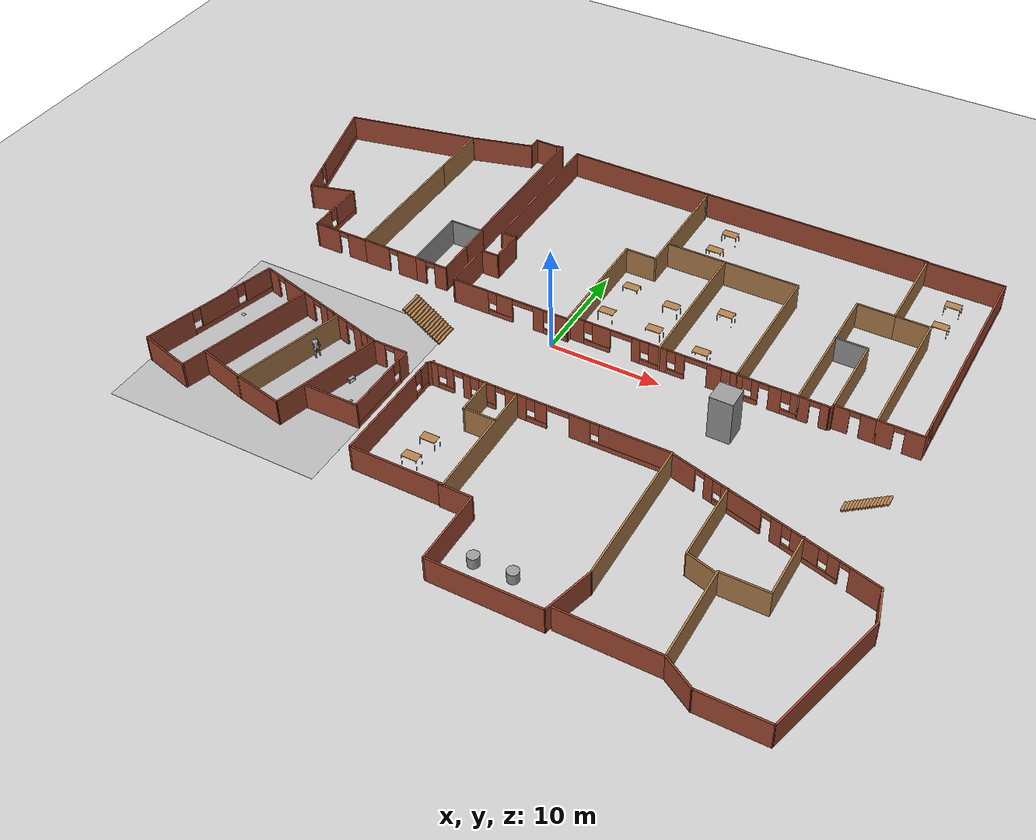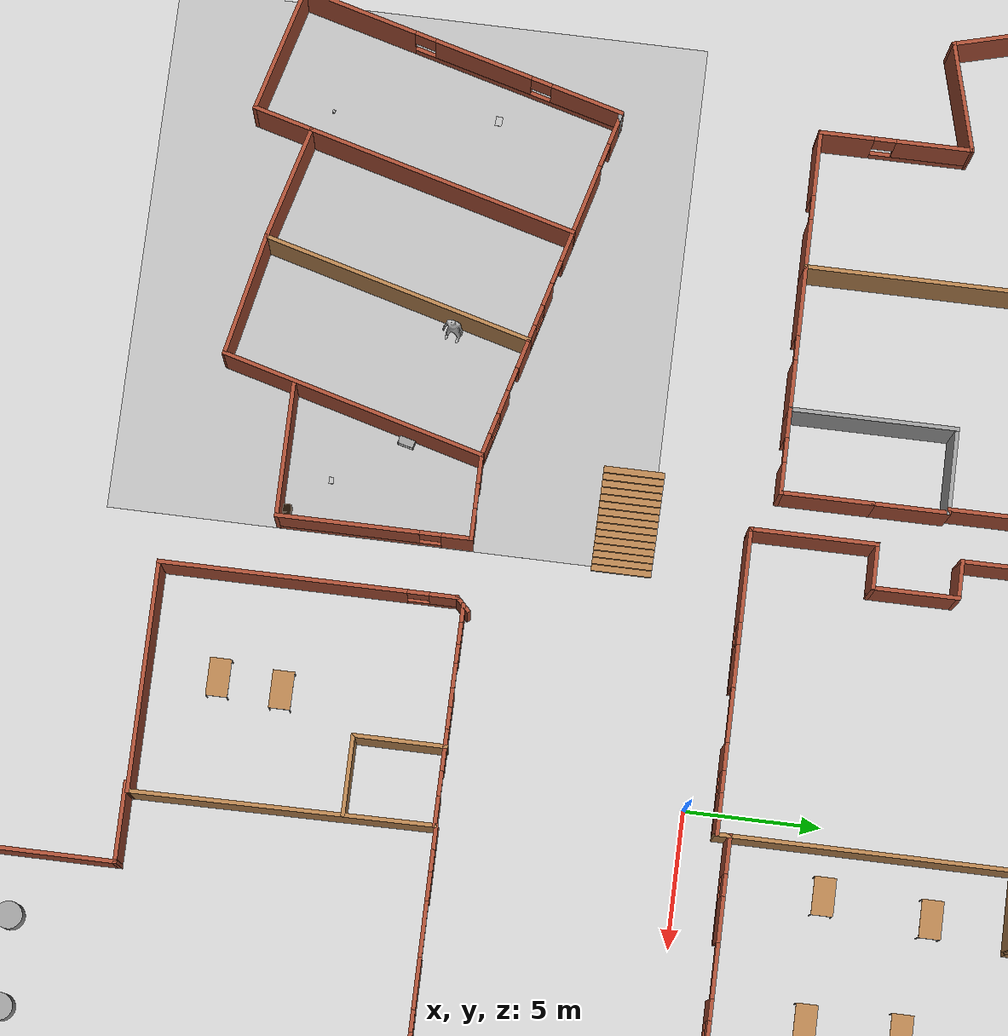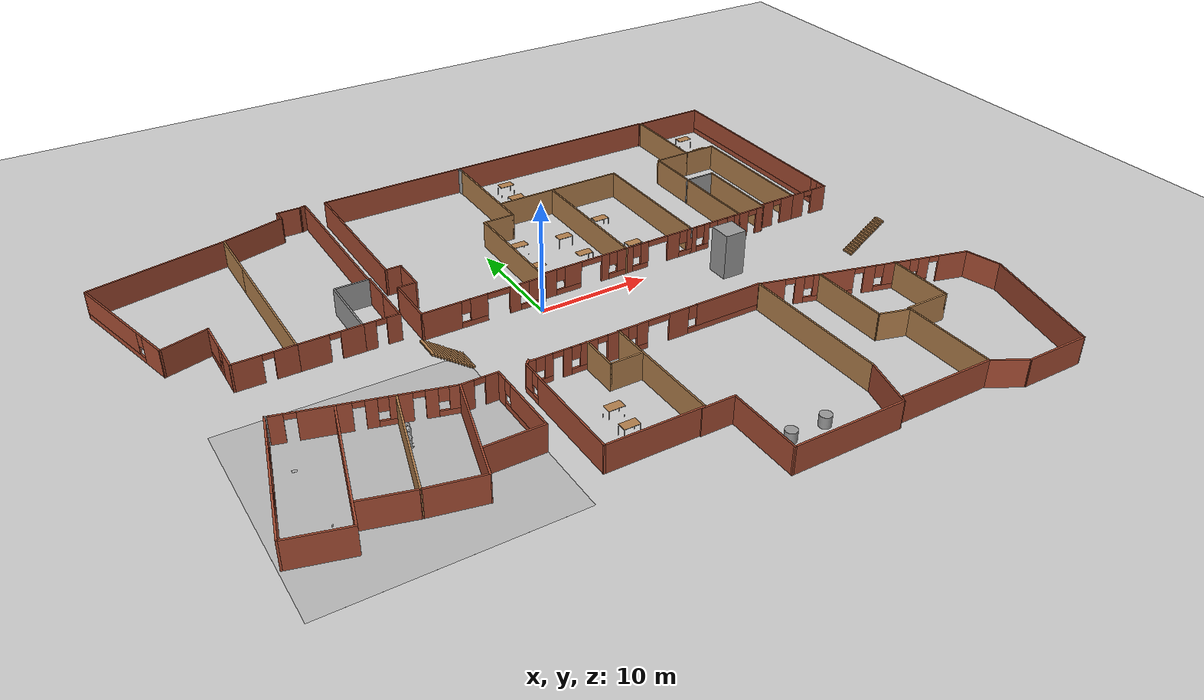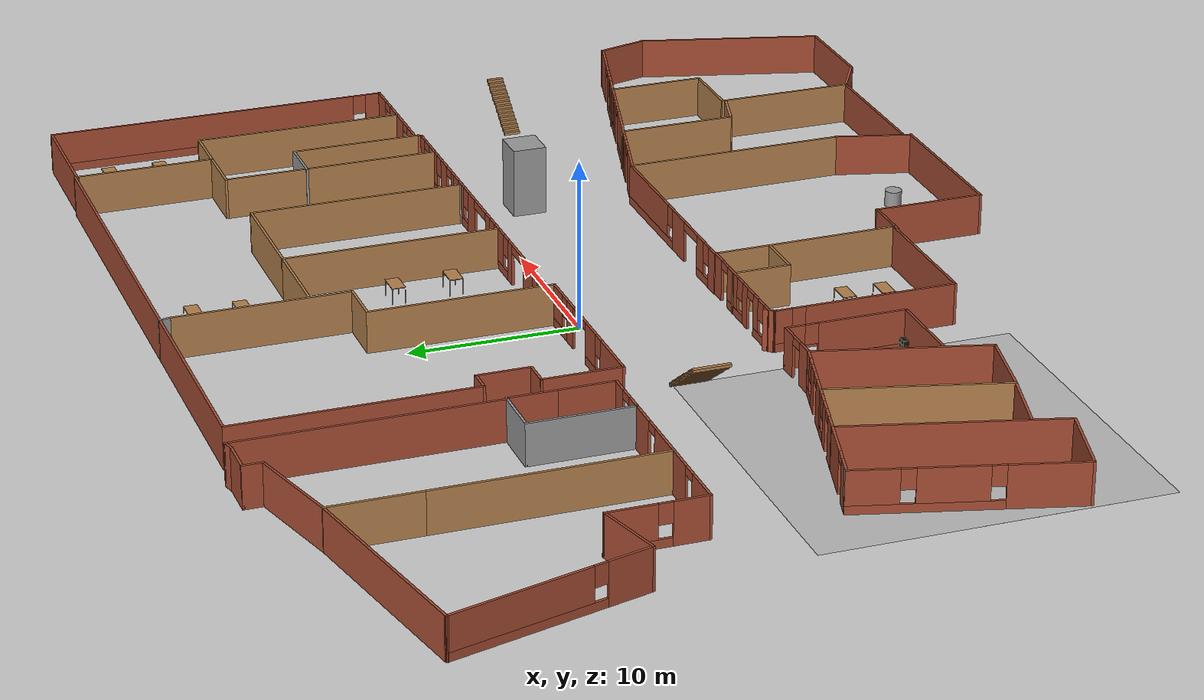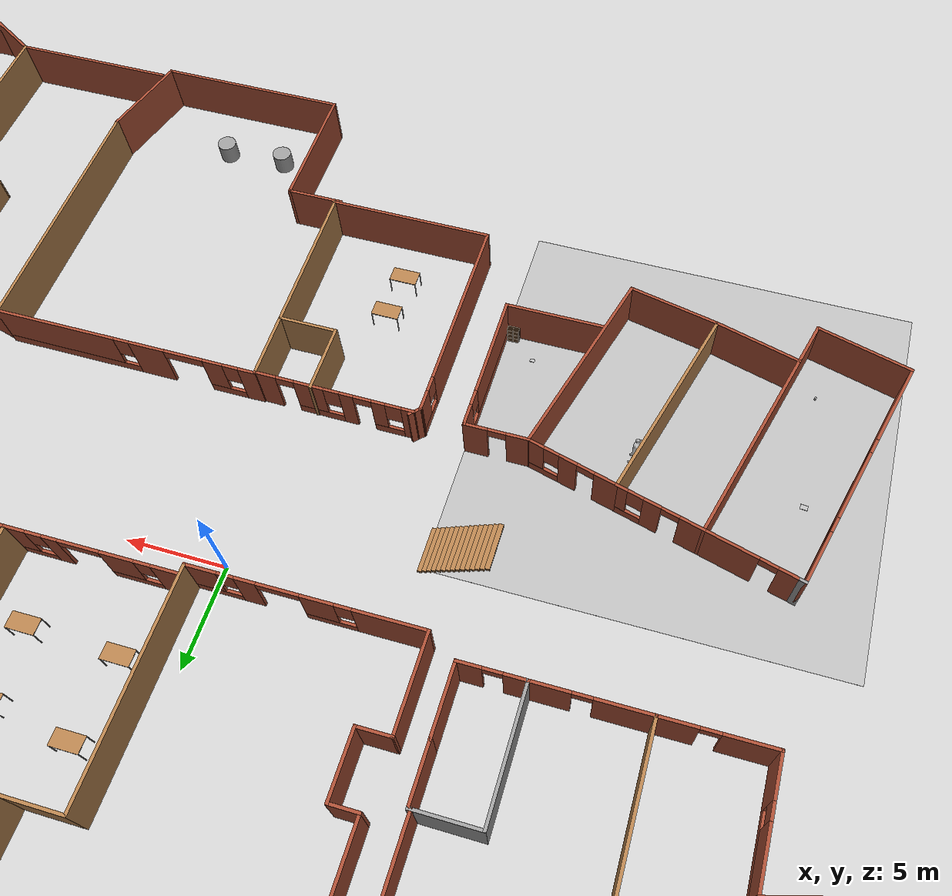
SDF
<sdf version="1.6">
 <world name="default">
  <light name="sun" type="directional">
   <pose>0 0 10 0 -0 0</pose>
   <diffuse>0.8 0.8 0.8 1</diffuse>
   <specular>0.1 0.1 0.1 1</specular>
   <attenuation>
    <range>1000</range>
    <constant>0.9</constant>
    <linear>0.01</linear>
    <quadratic>0.001</quadratic>
   </attenuation>
   <direction>-0.5 0.5 -1</direction>
  </light>
  <model name="ground_plane">
   <static>1</static>
   <link name="link">
    <collision name="collision">
     <geometry><plane><normal>0 0 1</normal><size>100 100</size></plane></geometry>
     <surface><friction><ode><mu>100</mu><mu2>50</mu2></ode></friction></surface>
    </collision>
    <visual name="visual">
     <cast_shadows>0</cast_shadows>
     <geometry><plane><normal>0 0 1</normal><size>100 100</size></plane></geometry>
     <material>
      <script><uri>file://media/materials/scripts/gazebo.material</uri><name>Gazebo/Grey</name></script>
     </material>
    </visual>
   </link>
  </model>
  <gravity>0 0 -9.8</gravity>
  <magnetic_field>6e-06 2.3e-05 -4.2e-05</magnetic_field>
  <atmosphere type="adiabatic"/>
  <physics name="default_physics" default="0" type="ode">
   <max_step_size>0.001</max_step_size>
   <real_time_factor>1</real_time_factor>
   <real_time_update_rate>1000</real_time_update_rate>
  </physics>
  <scene><ambient>0.4 0.4 0.4 1</ambient><background>0.7 0.7 0.7 1</background><shadows>1</shadows></scene>
  <spherical_coordinates>
   <surface_model>EARTH_WGS84</surface_model>
   <latitude_deg>0</latitude_deg>
   <longitude_deg>0</longitude_deg>
   <elevation>0</elevation>
   <heading_deg>0</heading_deg>
  </spherical_coordinates>
  <model name="vital">
   <pose>1.2398 -2.19799 0 0 -0 0</pose>
   <link name="Stairs_0">
    <visual name="Stairs_0_Visual_0">
     <pose>-9.74123 -1.05523 0.083333 0 -0 -1.5708</pose>
     <geometry><box><size>2.22056 0.233333 0.166667</size></box></geometry>
     <material>
      <script><uri>file://media/materials/scripts/gazebo.material</uri><name>Gazebo/Wood</name></script>
      <ambient>1 1 1 1</ambient>
     </material>
    </visual>
    <collision name="Stairs_0_Collision_0">
     <geometry><box><size>2.22056 0.233333 0.166667</size></box></geometry>
     <pose>-9.74123 -1.05523 0.083333 0 -0 -1.5708</pose>
    </collision>
    <visual name="Stairs_0_Visual_1">
     <pose>-9.97456 -1.05523 0.25 0 -0 -1.5708</pose>
     <geometry><box><size>2.22056 0.233333 0.166667</size></box></geometry>
     <material>
      <script><uri>file://media/materials/scripts/gazebo.material</uri><name>Gazebo/Wood</name></script>
      <ambient>1 1 1 1</ambient>
     </material>
    </visual>
    <collision name="Stairs_0_Collision_1">
     <geometry><box><size>2.22056 0.233333 0.166667</size></box></geometry>
     <pose>-9.97456 -1.05523 0.25 0 -0 -1.5708</pose>
    </collision>
    <visual name="Stairs_0_Visual_2">
     <pose>-10.2079 -1.05523 0.416667 0 -0 -1.5708</pose>
     <geometry><box><size>2.22056 0.233333 0.166667</size></box></geometry>
     <material>
      <script><uri>file://media/materials/scripts/gazebo.material</uri><name>Gazebo/Wood</name></script>
      <ambient>1 1 1 1</ambient>
     </material>
    </visual>
    <collision name="Stairs_0_Collision_2">
     <geometry><box><size>2.22056 0.233333 0.166667</size></box></geometry>
     <pose>-10.2079 -1.05523 0.416667 0 -0 -1.5708</pose>
    </collision>
    <visual name="Stairs_0_Visual_3">
     <pose>-10.4412 -1.05523 0.583333 0 -0 -1.5708</pose>
     <geometry><box><size>2.22056 0.233333 0.166667</size></box></geometry>
     <material>
      <script><uri>file://media/materials/scripts/gazebo.material</uri><name>Gazebo/Wood</name></script>
      <ambient>1 1 1 1</ambient>
     </material>
    </visual>
    <collision name="Stairs_0_Collision_3">
     <geometry><box><size>2.22056 0.233333 0.166667</size></box></geometry>
     <pose>-10.4412 -1.05523 0.583333 0 -0 -1.5708</pose>
    </collision>
    <visual name="Stairs_0_Visual_4">
     <pose>-10.6746 -1.05523 0.75 0 -0 -1.5708</pose>
     <geometry><box><size>2.22056 0.233333 0.166667</size></box></geometry>
     <material>
      <script><uri>file://media/materials/scripts/gazebo.material</uri><name>Gazebo/Wood</name></script>
      <ambient>1 1 1 1</ambient>
     </material>
    </visual>
    <collision name="Stairs_0_Collision_4">
     <geometry><box><size>2.22056 0.233333 0.166667</size></box></geometry>
     <pose>-10.6746 -1.05523 0.75 0 -0 -1.5708</pose>
    </collision>
    <visual name="Stairs_0_Visual_5">
     <pose>-10.9079 -1.05523 0.916667 0 -0 -1.5708</pose>
     <geometry><box><size>2.22056 0.233333 0.166667</size></box></geometry>
     <material>
      <script><uri>file://media/materials/scripts/gazebo.material</uri><name>Gazebo/Wood</name></script>
      <ambient>1 1 1 1</ambient>
     </material>
    </visual>
    <collision name="Stairs_0_Collision_5">
     <geometry><box><size>2.22056 0.233333 0.166667</size></box></geometry>
     <pose>-10.9079 -1.05523 0.916667 0 -0 -1.5708</pose>
    </collision>
    <visual name="Stairs_0_Visual_6">
     <pose>-11.1412 -1.05523 1.08333 0 -0 -1.5708</pose>
     <geometry><box><size>2.22056 0.233333 0.166667</size></box></geometry>
     <material>
      <script><uri>file://media/materials/scripts/gazebo.material</uri><name>Gazebo/Wood</name></script>
      <ambient>1 1 1 1</ambient>
     </material>
    </visual>
    <collision name="Stairs_0_Collision_6">
     <geometry><box><size>2.22056 0.233333 0.166667</size></box></geometry>
     <pose>-11.1412 -1.05523 1.08333 0 -0 -1.5708</pose>
    </collision>
    <visual name="Stairs_0_Visual_7">
     <pose>-11.3746 -1.05523 1.25 0 -0 -1.5708</pose>
     <geometry><box><size>2.22056 0.233333 0.166667</size></box></geometry>
     <material>
      <script><uri>file://media/materials/scripts/gazebo.material</uri><name>Gazebo/Wood</name></script>
      <ambient>1 1 1 1</ambient>
     </material>
    </visual>
    <collision name="Stairs_0_Collision_7">
     <geometry><box><size>2.22056 0.233333 0.166667</size></box></geometry>
     <pose>-11.3746 -1.05523 1.25 0 -0 -1.5708</pose>
    </collision>
    <visual name="Stairs_0_Visual_8">
     <pose>-11.6079 -1.05523 1.41667 0 -0 -1.5708</pose>
     <geometry><box><size>2.22056 0.233333 0.166667</size></box></geometry>
     <material>
      <script><uri>file://media/materials/scripts/gazebo.material</uri><name>Gazebo/Wood</name></script>
      <ambient>1 1 1 1</ambient>
     </material>
    </visual>
    <collision name="Stairs_0_Collision_8">
     <geometry><box><size>2.22056 0.233333 0.166667</size></box></geometry>
     <pose>-11.6079 -1.05523 1.41667 0 -0 -1.5708</pose>
    </collision>
    <visual name="Stairs_0_Visual_9">
     <pose>-11.8412 -1.05523 1.58333 0 -0 -1.5708</pose>
     <geometry><box><size>2.22056 0.233333 0.166667</size></box></geometry>
     <material>
      <script><uri>file://media/materials/scripts/gazebo.material</uri><name>Gazebo/Wood</name></script>
      <ambient>1 1 1 1</ambient>
     </material>
    </visual>
    <collision name="Stairs_0_Collision_9">
     <geometry><box><size>2.22056 0.233333 0.166667</size></box></geometry>
     <pose>-11.8412 -1.05523 1.58333 0 -0 -1.5708</pose>
    </collision>
    <visual name="Stairs_0_Visual_10">
     <pose>-12.0746 -1.05523 1.75 0 -0 -1.5708</pose>
     <geometry><box><size>2.22056 0.233333 0.166667</size></box></geometry>
     <material>
      <script><uri>file://media/materials/scripts/gazebo.material</uri><name>Gazebo/Wood</name></script>
      <ambient>1 1 1 1</ambient>
     </material>
    </visual>
    <collision name="Stairs_0_Collision_10">
     <geometry><box><size>2.22056 0.233333 0.166667</size></box></geometry>
     <pose>-12.0746 -1.05523 1.75 0 -0 -1.5708</pose>
    </collision>
    <visual name="Stairs_0_Visual_11">
     <pose>-12.3079 -1.05523 1.91667 0 -0 -1.5708</pose>
     <geometry><box><size>2.22056 0.233333 0.166667</size></box></geometry>
     <material>
      <script><uri>file://media/materials/scripts/gazebo.material</uri><name>Gazebo/Wood</name></script>
      <ambient>1 1 1 1</ambient>
     </material>
    </visual>
    <collision name="Stairs_0_Collision_11">
     <geometry><box><size>2.22056 0.233333 0.166667</size></box></geometry>
     <pose>-12.3079 -1.05523 1.91667 0 -0 -1.5708</pose>
    </collision>
    <visual name="Stairs_0_Visual_12">
     <pose>-12.5412 -1.05523 2.08333 0 -0 -1.5708</pose>
     <geometry><box><size>2.22056 0.233333 0.166667</size></box></geometry>
     <material>
      <script><uri>file://media/materials/scripts/gazebo.material</uri><name>Gazebo/Wood</name></script>
      <ambient>1 1 1 1</ambient>
     </material>
    </visual>
    <collision name="Stairs_0_Collision_12">
     <geometry><box><size>2.22056 0.233333 0.166667</size></box></geometry>
     <pose>-12.5412 -1.05523 2.08333 0 -0 -1.5708</pose>
    </collision>
    <visual name="Stairs_0_Visual_13">
     <pose>-12.7746 -1.05523 2.25 0 -0 -1.5708</pose>
     <geometry><box><size>2.22056 0.233333 0.166667</size></box></geometry>
     <material>
      <script><uri>file://media/materials/scripts/gazebo.material</uri><name>Gazebo/Wood</name></script>
      <ambient>1 1 1 1</ambient>
     </material>
    </visual>
    <collision name="Stairs_0_Collision_13">
     <geometry><box><size>2.22056 0.233333 0.166667</size></box></geometry>
     <pose>-12.7746 -1.05523 2.25 0 -0 -1.5708</pose>
    </collision>
    <visual name="Stairs_0_Visual_14">
     <pose>-13.0079 -1.05522 2.41667 0 -0 -1.5708</pose>
     <geometry><box><size>2.22056 0.233333 0.166667</size></box></geometry>
     <material>
      <script><uri>file://media/materials/scripts/gazebo.material</uri><name>Gazebo/Wood</name></script>
      <ambient>1 1 1 1</ambient>
     </material>
    </visual>
    <collision name="Stairs_0_Collision_14">
     <geometry><box><size>2.22056 0.233333 0.166667</size></box></geometry>
     <pose>-13.0079 -1.05522 2.41667 0 -0 -1.5708</pose>
    </collision>
   </link>
   <link name="Stairs_1">
    <visual name="Stairs_1_Visual_0">
     <pose>27.018 -3.37906 0.083333 0 -0 1.5708</pose>
     <geometry><box><size>1 0.233333 0.166667</size></box></geometry>
     <material>
      <script><uri>file://media/materials/scripts/gazebo.material</uri><name>Gazebo/Wood</name></script>
      <ambient>1 1 1 1</ambient>
     </material>
    </visual>
    <collision name="Stairs_1_Collision_0">
     <geometry><box><size>1 0.233333 0.166667</size></box></geometry>
     <pose>27.018 -3.37906 0.083333 0 -0 1.5708</pose>
    </collision>
    <visual name="Stairs_1_Visual_1">
     <pose>27.2513 -3.37906 0.25 0 -0 1.5708</pose>
     <geometry><box><size>1 0.233333 0.166667</size></box></geometry>
     <material>
      <script><uri>file://media/materials/scripts/gazebo.material</uri><name>Gazebo/Wood</name></script>
      <ambient>1 1 1 1</ambient>
     </material>
    </visual>
    <collision name="Stairs_1_Collision_1">
     <geometry><box><size>1 0.233333 0.166667</size></box></geometry>
     <pose>27.2513 -3.37906 0.25 0 -0 1.5708</pose>
    </collision>
    <visual name="Stairs_1_Visual_2">
     <pose>27.4847 -3.37906 0.416667 0 -0 1.5708</pose>
     <geometry><box><size>1 0.233333 0.166667</size></box></geometry>
     <material>
      <script><uri>file://media/materials/scripts/gazebo.material</uri><name>Gazebo/Wood</name></script>
      <ambient>1 1 1 1</ambient>
     </material>
    </visual>
    <collision name="Stairs_1_Collision_2">
     <geometry><box><size>1 0.233333 0.166667</size></box></geometry>
     <pose>27.4847 -3.37906 0.416667 0 -0 1.5708</pose>
    </collision>
    <visual name="Stairs_1_Visual_3">
     <pose>27.718 -3.37906 0.583333 0 -0 1.5708</pose>
     <geometry><box><size>1 0.233333 0.166667</size></box></geometry>
     <material>
      <script><uri>file://media/materials/scripts/gazebo.material</uri><name>Gazebo/Wood</name></script>
      <ambient>1 1 1 1</ambient>
     </material>
    </visual>
    <collision name="Stairs_1_Collision_3">
     <geometry><box><size>1 0.233333 0.166667</size></box></geometry>
     <pose>27.718 -3.37906 0.583333 0 -0 1.5708</pose>
    </collision>
    <visual name="Stairs_1_Visual_4">
     <pose>27.9513 -3.37906 0.75 0 -0 1.5708</pose>
     <geometry><box><size>1 0.233333 0.166667</size></box></geometry>
     <material>
      <script><uri>file://media/materials/scripts/gazebo.material</uri><name>Gazebo/Wood</name></script>
      <ambient>1 1 1 1</ambient>
     </material>
    </visual>
    <collision name="Stairs_1_Collision_4">
     <geometry><box><size>1 0.233333 0.166667</size></box></geometry>
     <pose>27.9513 -3.37906 0.75 0 -0 1.5708</pose>
    </collision>
    <visual name="Stairs_1_Visual_5">
     <pose>28.1847 -3.37906 0.916667 0 -0 1.5708</pose>
     <geometry><box><size>1 0.233333 0.166667</size></box></geometry>
     <material>
      <script><uri>file://media/materials/scripts/gazebo.material</uri><name>Gazebo/Wood</name></script>
      <ambient>1 1 1 1</ambient>
     </material>
    </visual>
    <collision name="Stairs_1_Collision_5">
     <geometry><box><size>1 0.233333 0.166667</size></box></geometry>
     <pose>28.1847 -3.37906 0.916667 0 -0 1.5708</pose>
    </collision>
    <visual name="Stairs_1_Visual_6">
     <pose>28.418 -3.37906 1.08333 0 -0 1.5708</pose>
     <geometry><box><size>1 0.233333 0.166667</size></box></geometry>
     <material>
      <script><uri>file://media/materials/scripts/gazebo.material</uri><name>Gazebo/Wood</name></script>
      <ambient>1 1 1 1</ambient>
     </material>
    </visual>
    <collision name="Stairs_1_Collision_6">
     <geometry><box><size>1 0.233333 0.166667</size></box></geometry>
     <pose>28.418 -3.37906 1.08333 0 -0 1.5708</pose>
    </collision>
    <visual name="Stairs_1_Visual_7">
     <pose>28.6513 -3.37906 1.25 0 -0 1.5708</pose>
     <geometry><box><size>1 0.233333 0.166667</size></box></geometry>
     <material>
      <script><uri>file://media/materials/scripts/gazebo.material</uri><name>Gazebo/Wood</name></script>
      <ambient>1 1 1 1</ambient>
     </material>
    </visual>
    <collision name="Stairs_1_Collision_7">
     <geometry><box><size>1 0.233333 0.166667</size></box></geometry>
     <pose>28.6513 -3.37906 1.25 0 -0 1.5708</pose>
    </collision>
    <visual name="Stairs_1_Visual_8">
     <pose>28.8847 -3.37906 1.41667 0 -0 1.5708</pose>
     <geometry><box><size>1 0.233333 0.166667</size></box></geometry>
     <material>
      <script><uri>file://media/materials/scripts/gazebo.material</uri><name>Gazebo/Wood</name></script>
      <ambient>1 1 1 1</ambient>
     </material>
    </visual>
    <collision name="Stairs_1_Collision_8">
     <geometry><box><size>1 0.233333 0.166667</size></box></geometry>
     <pose>28.8847 -3.37906 1.41667 0 -0 1.5708</pose>
    </collision>
    <visual name="Stairs_1_Visual_9">
     <pose>29.118 -3.37906 1.58333 0 -0 1.5708</pose>
     <geometry><box><size>1 0.233333 0.166667</size></box></geometry>
     <material>
      <script><uri>file://media/materials/scripts/gazebo.material</uri><name>Gazebo/Wood</name></script>
      <ambient>1 1 1 1</ambient>
     </material>
    </visual>
    <collision name="Stairs_1_Collision_9">
     <geometry><box><size>1 0.233333 0.166667</size></box></geometry>
     <pose>29.118 -3.37906 1.58333 0 -0 1.5708</pose>
    </collision>
    <visual name="Stairs_1_Visual_10">
     <pose>29.3513 -3.37906 1.75 0 -0 1.5708</pose>
     <geometry><box><size>1 0.233333 0.166667</size></box></geometry>
     <material>
      <script><uri>file://media/materials/scripts/gazebo.material</uri><name>Gazebo/Wood</name></script>
      <ambient>1 1 1 1</ambient>
     </material>
    </visual>
    <collision name="Stairs_1_Collision_10">
     <geometry><box><size>1 0.233333 0.166667</size></box></geometry>
     <pose>29.3513 -3.37906 1.75 0 -0 1.5708</pose>
    </collision>
    <visual name="Stairs_1_Visual_11">
     <pose>29.5847 -3.37906 1.91667 0 -0 1.5708</pose>
     <geometry><box><size>1 0.233333 0.166667</size></box></geometry>
     <material>
      <script><uri>file://media/materials/scripts/gazebo.material</uri><name>Gazebo/Wood</name></script>
      <ambient>1 1 1 1</ambient>
     </material>
    </visual>
    <collision name="Stairs_1_Collision_11">
     <geometry><box><size>1 0.233333 0.166667</size></box></geometry>
     <pose>29.5847 -3.37906 1.91667 0 -0 1.5708</pose>
    </collision>
    <visual name="Stairs_1_Visual_12">
     <pose>29.818 -3.37906 2.08333 0 -0 1.5708</pose>
     <geometry><box><size>1 0.233333 0.166667</size></box></geometry>
     <material>
      <script><uri>file://media/materials/scripts/gazebo.material</uri><name>Gazebo/Wood</name></script>
      <ambient>1 1 1 1</ambient>
     </material>
    </visual>
    <collision name="Stairs_1_Collision_12">
     <geometry><box><size>1 0.233333 0.166667</size></box></geometry>
     <pose>29.818 -3.37906 2.08333 0 -0 1.5708</pose>
    </collision>
    <visual name="Stairs_1_Visual_13">
     <pose>30.0513 -3.37906 2.25 0 -0 1.5708</pose>
     <geometry><box><size>1 0.233333 0.166667</size></box></geometry>
     <material>
      <script><uri>file://media/materials/scripts/gazebo.material</uri><name>Gazebo/Wood</name></script>
      <ambient>1 1 1 1</ambient>
     </material>
    </visual>
    <collision name="Stairs_1_Collision_13">
     <geometry><box><size>1 0.233333 0.166667</size></box></geometry>
     <pose>30.0513 -3.37906 2.25 0 -0 1.5708</pose>
    </collision>
    <visual name="Stairs_1_Visual_14">
     <pose>30.2847 -3.37905 2.41667 0 -0 1.5708</pose>
     <geometry><box><size>1 0.233333 0.166667</size></box></geometry>
     <material>
      <script><uri>file://media/materials/scripts/gazebo.material</uri><name>Gazebo/Wood</name></script>
      <ambient>1 1 1 1</ambient>
     </material>
    </visual>
    <collision name="Stairs_1_Collision_14">
     <geometry><box><size>1 0.233333 0.166667</size></box></geometry>
     <pose>30.2847 -3.37905 2.41667 0 -0 1.5708</pose>
    </collision>
   </link>
   <link name="Wall_100">
    <collision name="Wall_100_Collision">
     <geometry><box><size>5 0.15 2.5</size></box></geometry>
     <pose>0 0 1.25 0 -0 0</pose>
    </collision>
    <visual name="Wall_100_Visual">
     <pose>0 0 1.25 0 -0 0</pose>
     <geometry><box><size>5 0.15 2.5</size></box></geometry>
     <material>
      <script><uri>file://media/materials/scripts/gazebo.material</uri><name>Gazebo/Bricks</name></script>
      <ambient>1 1 1 1</ambient>
     </material>
    </visual>
    <pose>-27.234 -15.8492 0 0 -0 2.87979</pose>
   </link>
   <link name="Wall_101">
    <pose>-27.9458 -9.13623 0 0 -0 1.309</pose>
    <visual name="Wall_101_Visual_0">
     <pose>-4.12668 0 1.25 0 -0 0</pose>
     <geometry><box><size>4.49665 0.15 2.5</size></box></geometry>
     <material>
      <script><uri>file://media/materials/scripts/gazebo.material</uri><name>Gazebo/Bricks</name></script>
      <ambient>1 1 1 1</ambient>
     </material>
    </visual>
    <collision name="Wall_101_Collision_0">
     <geometry><box><size>4.49665 0.15 2.5</size></box></geometry>
     <pose>-4.12668 0 1.25 0 -0 0</pose>
    </collision>
    <visual name="Wall_101_Visual_1">
     <pose>2.24832 0 0.25 0 -0 0</pose>
     <geometry><box><size>8.25336 0.15 0.5</size></box></geometry>
     <material>
      <script><uri>file://media/materials/scripts/gazebo.material</uri><name>Gazebo/Bricks</name></script>
      <ambient>1 1 1 1</ambient>
     </material>
    </visual>
    <collision name="Wall_101_Collision_1">
     <geometry><box><size>8.25336 0.15 0.5</size></box></geometry>
     <pose>2.24832 0 0.25 0 -0 0</pose>
    </collision>
    <visual name="Wall_101_Visual_2">
     <pose>0.830511 0 1.5 0 -0 0</pose>
     <geometry><box><size>3.81773 0.15 2</size></box></geometry>
     <material>
      <script><uri>file://media/materials/scripts/gazebo.material</uri><name>Gazebo/Bricks</name></script>
      <ambient>1 1 1 1</ambient>
     </material>
    </visual>
    <collision name="Wall_101_Collision_2">
     <geometry><box><size>3.81773 0.15 2</size></box></geometry>
     <pose>0.830511 0 1.5 0 -0 0</pose>
    </collision>
    <visual name="Wall_101_Visual_3">
     <pose>4.95719 0 1.5 0 -0 0</pose>
     <geometry><box><size>2.83562 0.15 2</size></box></geometry>
     <material>
      <script><uri>file://media/materials/scripts/gazebo.material</uri><name>Gazebo/Bricks</name></script>
      <ambient>1 1 1 1</ambient>
     </material>
    </visual>
    <collision name="Wall_101_Collision_3">
     <geometry><box><size>2.83562 0.15 2</size></box></geometry>
     <pose>4.95719 0 1.5 0 -0 0</pose>
    </collision>
    <visual name="Wall_101_Visual_4">
     <pose>-1.47836 0 1.9 0 -0 0</pose>
     <geometry><box><size>0.8 0.15 1.2</size></box></geometry>
     <material>
      <script><uri>file://media/materials/scripts/gazebo.material</uri><name>Gazebo/Bricks</name></script>
      <ambient>1 1 1 1</ambient>
     </material>
    </visual>
    <collision name="Wall_101_Collision_4">
     <geometry><box><size>0.8 0.15 1.2</size></box></geometry>
     <pose>-1.47836 0 1.9 0 -0 0</pose>
    </collision>
    <visual name="Wall_101_Visual_5">
     <pose>3.13938 0 1.9 0 -0 0</pose>
     <geometry><box><size>0.8 0.15 1.2</size></box></geometry>
     <material>
      <script><uri>file://media/materials/scripts/gazebo.material</uri><name>Gazebo/Bricks</name></script>
      <ambient>1 1 1 1</ambient>
     </material>
    </visual>
    <collision name="Wall_101_Collision_5">
     <geometry><box><size>0.8 0.15 1.2</size></box></geometry>
     <pose>3.13938 0 1.9 0 -0 0</pose>
    </collision>
   </link>
   <link name="Wall_102">
    <collision name="Wall_102_Collision">
     <geometry><box><size>0.4 0.15 2.5</size></box></geometry>
     <pose>0 0 1.25 0 -0 0</pose>
    </collision>
    <visual name="Wall_102_Visual">
     <pose>0 0 1.25 0 -0 0</pose>
     <geometry><box><size>0.4 0.15 2.5</size></box></geometry>
     <material>
      <script><uri>file://media/materials/scripts/gazebo.material</uri><name>Gazebo/Grey</name></script>
      <ambient>1 1 1 1</ambient>
     </material>
    </visual>
    <pose>-26.1945 -3.08325 0 0 0 -0.261799</pose>
   </link>
   <link name="Wall_104">
    <pose>-19.5297 -4.8691 0 0 0 -0.261799</pose>
    <visual name="Wall_104_Visual_0">
     <pose>-1.62247 0 1.25 0 -0 0</pose>
     <geometry><box><size>1.25506 0.15 2.5</size></box></geometry>
     <material>
      <script><uri>file://media/materials/scripts/gazebo.material</uri><name>Gazebo/Bricks</name></script>
      <ambient>1 1 1 1</ambient>
     </material>
    </visual>
    <collision name="Wall_104_Collision_0">
     <geometry><box><size>1.25506 0.15 2.5</size></box></geometry>
     <pose>-1.62247 0 1.25 0 -0 0</pose>
    </collision>
    <visual name="Wall_104_Visual_1">
     <pose>0.350281 0 1.25 0 -0 0</pose>
     <geometry><box><size>0.890442 0.15 2.5</size></box></geometry>
     <material>
      <script><uri>file://media/materials/scripts/gazebo.material</uri><name>Gazebo/Bricks</name></script>
      <ambient>1 1 1 1</ambient>
     </material>
    </visual>
    <collision name="Wall_104_Collision_1">
     <geometry><box><size>0.890442 0.15 2.5</size></box></geometry>
     <pose>0.350281 0 1.25 0 -0 0</pose>
    </collision>
    <visual name="Wall_104_Visual_2">
     <pose>1.52275 0 0.25 0 -0 0</pose>
     <geometry><box><size>1.4545 0.15 0.5</size></box></geometry>
     <material>
      <script><uri>file://media/materials/scripts/gazebo.material</uri><name>Gazebo/Bricks</name></script>
      <ambient>1 1 1 1</ambient>
     </material>
    </visual>
    <collision name="Wall_104_Collision_2">
     <geometry><box><size>1.4545 0.15 0.5</size></box></geometry>
     <pose>1.52275 0 0.25 0 -0 0</pose>
    </collision>
    <visual name="Wall_104_Visual_3">
     <pose>1.92275 0 1.5 0 -0 0</pose>
     <geometry><box><size>0.654498 0.15 2</size></box></geometry>
     <material>
      <script><uri>file://media/materials/scripts/gazebo.material</uri><name>Gazebo/Bricks</name></script>
      <ambient>1 1 1 1</ambient>
     </material>
    </visual>
    <collision name="Wall_104_Collision_3">
     <geometry><box><size>0.654498 0.15 2</size></box></geometry>
     <pose>1.92275 0 1.5 0 -0 0</pose>
    </collision>
    <visual name="Wall_104_Visual_4">
     <pose>1.1955 0 1.9 0 -0 0</pose>
     <geometry><box><size>0.8 0.15 1.2</size></box></geometry>
     <material>
      <script><uri>file://media/materials/scripts/gazebo.material</uri><name>Gazebo/Bricks</name></script>
      <ambient>1 1 1 1</ambient>
     </material>
    </visual>
    <collision name="Wall_104_Collision_4">
     <geometry><box><size>0.8 0.15 1.2</size></box></geometry>
     <pose>1.1955 0 1.9 0 -0 0</pose>
    </collision>
    <visual name="Wall_104_Visual_5">
     <pose>-0.54494 0 2.25 0 -0 0</pose>
     <geometry><box><size>0.9 0.15 0.5</size></box></geometry>
     <material>
      <script><uri>file://media/materials/scripts/gazebo.material</uri><name>Gazebo/Bricks</name></script>
      <ambient>1 1 1 1</ambient>
     </material>
    </visual>
    <collision name="Wall_104_Collision_5">
     <geometry><box><size>0.9 0.15 0.5</size></box></geometry>
     <pose>-0.54494 0 2.25 0 -0 0</pose>
    </collision>
   </link>
   <link name="Wall_105">
    <collision name="Wall_105_Collision">
     <geometry><box><size>10.5 0.15 2.5</size></box></geometry>
     <pose>0 0 1.25 0 -0 0</pose>
    </collision>
    <visual name="Wall_105_Visual">
     <pose>0 0 1.25 0 -0 0</pose>
     <geometry><box><size>10.5 0.15 2.5</size></box></geometry>
     <material>
      <script><uri>file://media/materials/scripts/gazebo.material</uri><name>Gazebo/Wood</name></script>
      <ambient>1 1 1 1</ambient>
     </material>
    </visual>
    <pose>-18.7682 -10.4307 0 0 0 -1.8326</pose>
   </link>
   <link name="Wall_106">
    <collision name="Wall_106_Collision">
     <geometry><box><size>4.5 0.15 2.5</size></box></geometry>
     <pose>0 0 1.25 0 -0 0</pose>
    </collision>
    <visual name="Wall_106_Visual">
     <pose>0 0 1.25 0 -0 0</pose>
     <geometry><box><size>4.5 0.15 2.5</size></box></geometry>
     <material>
      <script><uri>file://media/materials/scripts/gazebo.material</uri><name>Gazebo/Bricks</name></script>
      <ambient>1 1 1 1</ambient>
     </material>
    </visual>
    <pose>-22.2084 -14.8664 0 0 -0 2.87979</pose>
   </link>
   <link name="Wall_108">
    <pose>-15.2071 -6.02732 0 0 0 -0.261799</pose>
    <visual name="Wall_108_Visual_0">
     <pose>-1.7708 0 1.25 0 -0 0</pose>
     <geometry><box><size>1.2084 0.15 2.5</size></box></geometry>
     <material>
      <script><uri>file://media/materials/scripts/gazebo.material</uri><name>Gazebo/Bricks</name></script>
      <ambient>1 1 1 1</ambient>
     </material>
    </visual>
    <collision name="Wall_108_Collision_0">
     <geometry><box><size>1.2084 0.15 2.5</size></box></geometry>
     <pose>-1.7708 0 1.25 0 -0 0</pose>
    </collision>
    <visual name="Wall_108_Visual_1">
     <pose>0.199682 0 1.25 0 -0 0</pose>
     <geometry><box><size>0.932562 0.15 2.5</size></box></geometry>
     <material>
      <script><uri>file://media/materials/scripts/gazebo.material</uri><name>Gazebo/Bricks</name></script>
      <ambient>1 1 1 1</ambient>
     </material>
    </visual>
    <collision name="Wall_108_Collision_1">
     <geometry><box><size>0.932562 0.15 2.5</size></box></geometry>
     <pose>0.199682 0 1.25 0 -0 0</pose>
    </collision>
    <visual name="Wall_108_Visual_2">
     <pose>1.52048 0 0.25 0 -0 0</pose>
     <geometry><box><size>1.70904 0.15 0.5</size></box></geometry>
     <material>
      <script><uri>file://media/materials/scripts/gazebo.material</uri><name>Gazebo/Bricks</name></script>
      <ambient>1 1 1 1</ambient>
     </material>
    </visual>
    <collision name="Wall_108_Collision_2">
     <geometry><box><size>1.70904 0.15 0.5</size></box></geometry>
     <pose>1.52048 0 0.25 0 -0 0</pose>
    </collision>
    <visual name="Wall_108_Visual_3">
     <pose>1.92048 0 1.5 0 -0 0</pose>
     <geometry><box><size>0.909036 0.15 2</size></box></geometry>
     <material>
      <script><uri>file://media/materials/scripts/gazebo.material</uri><name>Gazebo/Bricks</name></script>
      <ambient>1 1 1 1</ambient>
     </material>
    </visual>
    <collision name="Wall_108_Collision_3">
     <geometry><box><size>0.909036 0.15 2</size></box></geometry>
     <pose>1.92048 0 1.5 0 -0 0</pose>
    </collision>
    <visual name="Wall_108_Visual_4">
     <pose>1.06596 0 1.9 0 -0 0</pose>
     <geometry><box><size>0.8 0.15 1.2</size></box></geometry>
     <material>
      <script><uri>file://media/materials/scripts/gazebo.material</uri><name>Gazebo/Bricks</name></script>
      <ambient>1 1 1 1</ambient>
     </material>
    </visual>
    <collision name="Wall_108_Collision_4">
     <geometry><box><size>0.8 0.15 1.2</size></box></geometry>
     <pose>1.06596 0 1.9 0 -0 0</pose>
    </collision>
    <visual name="Wall_108_Visual_5">
     <pose>-0.716599 0 2.25 0 -0 0</pose>
     <geometry><box><size>0.9 0.15 0.5</size></box></geometry>
     <material>
      <script><uri>file://media/materials/scripts/gazebo.material</uri><name>Gazebo/Bricks</name></script>
      <ambient>1 1 1 1</ambient>
     </material>
    </visual>
    <collision name="Wall_108_Collision_5">
     <geometry><box><size>0.9 0.15 0.5</size></box></geometry>
     <pose>-0.716599 0 2.25 0 -0 0</pose>
    </collision>
   </link>
   <link name="Wall_109">
    <collision name="Wall_109_Collision">
     <geometry><box><size>10.25 0.15 2.5</size></box></geometry>
     <pose>0 0 1.25 0 -0 0</pose>
    </collision>
    <visual name="Wall_109_Visual">
     <pose>0 0 1.25 0 -0 0</pose>
     <geometry><box><size>10.25 0.15 2.5</size></box></geometry>
     <material>
      <script><uri>file://media/materials/scripts/gazebo.material</uri><name>Gazebo/Bricks</name></script>
      <ambient>1 1 1 1</ambient>
     </material>
    </visual>
    <pose>-14.2925 -11.5005 0 0 0 -1.8326</pose>
   </link>
   <link name="Wall_110">
    <collision name="Wall_110_Collision">
     <geometry><box><size>4.75679 0.15 2.5</size></box></geometry>
     <pose>0 0 1.25 0 -0 0</pose>
    </collision>
    <visual name="Wall_110_Visual">
     <pose>0 0 1.25 0 -0 0</pose>
     <geometry><box><size>4.75679 0.15 2.5</size></box></geometry>
     <material>
      <script><uri>file://media/materials/scripts/gazebo.material</uri><name>Gazebo/Bricks</name></script>
      <ambient>1 1 1 1</ambient>
     </material>
    </visual>
    <pose>-17.8536 -15.9039 0 0 -0 2.93409</pose>
   </link>
   <link name="Wall_112">
    <pose>-11.4355 -6.6226 0 0 -0 0</pose>
    <visual name="Wall_112_Visual_0">
     <pose>-1.04973 0 1.25 0 -0 0</pose>
     <geometry><box><size>1.15054 0.15 2.5</size></box></geometry>
     <material>
      <script><uri>file://media/materials/scripts/gazebo.material</uri><name>Gazebo/Bricks</name></script>
      <ambient>1 1 1 1</ambient>
     </material>
    </visual>
    <collision name="Wall_112_Collision_0">
     <geometry><box><size>1.15054 0.15 2.5</size></box></geometry>
     <pose>-1.04973 0 1.25 0 -0 0</pose>
    </collision>
    <visual name="Wall_112_Visual_1">
     <pose>1.02527 0 1.25 0 -0 0</pose>
     <geometry><box><size>1.19946 0.15 2.5</size></box></geometry>
     <material>
      <script><uri>file://media/materials/scripts/gazebo.material</uri><name>Gazebo/Bricks</name></script>
      <ambient>1 1 1 1</ambient>
     </material>
    </visual>
    <collision name="Wall_112_Collision_1">
     <geometry><box><size>1.19946 0.15 2.5</size></box></geometry>
     <pose>1.02527 0 1.25 0 -0 0</pose>
    </collision>
    <visual name="Wall_112_Visual_2">
     <pose>-0.024462 0 2.25 0 -0 0</pose>
     <geometry><box><size>0.9 0.15 0.5</size></box></geometry>
     <material>
      <script><uri>file://media/materials/scripts/gazebo.material</uri><name>Gazebo/Bricks</name></script>
      <ambient>1 1 1 1</ambient>
     </material>
    </visual>
    <collision name="Wall_112_Collision_2">
     <geometry><box><size>0.9 0.15 0.5</size></box></geometry>
     <pose>-0.024462 0 2.25 0 -0 0</pose>
    </collision>
   </link>
   <link name="Wall_113">
    <pose>-9.88551 -10.1726 0 0 0 -1.5708</pose>
    <visual name="Wall_113_Visual_0">
     <pose>-3.04191 0 1.25 0 -0 0</pose>
     <geometry><box><size>1.16617 0.15 2.5</size></box></geometry>
     <material>
      <script><uri>file://media/materials/scripts/gazebo.material</uri><name>Gazebo/Bricks</name></script>
      <ambient>1 1 1 1</ambient>
     </material>
    </visual>
    <collision name="Wall_113_Collision_0">
     <geometry><box><size>1.16617 0.15 2.5</size></box></geometry>
     <pose>-3.04191 0 1.25 0 -0 0</pose>
    </collision>
    <visual name="Wall_113_Visual_1">
     <pose>0.583086 0 0.25 0 -0 0</pose>
     <geometry><box><size>6.08383 0.15 0.5</size></box></geometry>
     <material>
      <script><uri>file://media/materials/scripts/gazebo.material</uri><name>Gazebo/Bricks</name></script>
      <ambient>1 1 1 1</ambient>
     </material>
    </visual>
    <collision name="Wall_113_Collision_1">
     <geometry><box><size>6.08383 0.15 0.5</size></box></geometry>
     <pose>0.583086 0 0.25 0 -0 0</pose>
    </collision>
    <visual name="Wall_113_Visual_2">
     <pose>0.983086 0 1.5 0 -0 0</pose>
     <geometry><box><size>5.28383 0.15 2</size></box></geometry>
     <material>
      <script><uri>file://media/materials/scripts/gazebo.material</uri><name>Gazebo/Bricks</name></script>
      <ambient>1 1 1 1</ambient>
     </material>
    </visual>
    <collision name="Wall_113_Collision_2">
     <geometry><box><size>5.28383 0.15 2</size></box></geometry>
     <pose>0.983086 0 1.5 0 -0 0</pose>
    </collision>
    <visual name="Wall_113_Visual_3">
     <pose>-2.05883 0 1.9 0 -0 0</pose>
     <geometry><box><size>0.8 0.15 1.2</size></box></geometry>
     <material>
      <script><uri>file://media/materials/scripts/gazebo.material</uri><name>Gazebo/Bricks</name></script>
      <ambient>1 1 1 1</ambient>
     </material>
    </visual>
    <collision name="Wall_113_Collision_3">
     <geometry><box><size>0.8 0.15 1.2</size></box></geometry>
     <pose>-2.05883 0 1.9 0 -0 0</pose>
    </collision>
   </link>
   <link name="Wall_114">
    <collision name="Wall_114_Collision">
     <geometry><box><size>5 0.15 2.5</size></box></geometry>
     <pose>0 0 1.25 0 -0 0</pose>
    </collision>
    <visual name="Wall_114_Visual">
     <pose>0 0 1.25 0 -0 0</pose>
     <geometry><box><size>5 0.15 2.5</size></box></geometry>
     <material>
      <script><uri>file://media/materials/scripts/gazebo.material</uri><name>Gazebo/Bricks</name></script>
      <ambient>1 1 1 1</ambient>
     </material>
    </visual>
    <pose>-12.3105 -13.7226 0 0 -0 3.14159</pose>
   </link>
   <link name="Wall_116">
    <pose>-3.44702 -6.63306 0 0 0 -0.006694</pose>
    <visual name="Wall_116_Visual_0">
     <pose>-3.71942 0 1.25 0 -0 0</pose>
     <geometry><box><size>0.704332 0.15 2.5</size></box></geometry>
     <material>
      <script><uri>file://media/materials/scripts/gazebo.material</uri><name>Gazebo/Bricks</name></script>
      <ambient>1 1 1 1</ambient>
     </material>
    </visual>
    <collision name="Wall_116_Collision_0">
     <geometry><box><size>0.704332 0.15 2.5</size></box></geometry>
     <pose>-3.71942 0 1.25 0 -0 0</pose>
    </collision>
    <visual name="Wall_116_Visual_1">
     <pose>-0.624879 0 1.25 0 -0 0</pose>
     <geometry><box><size>0.697096 0.15 2.5</size></box></geometry>
     <material>
      <script><uri>file://media/materials/scripts/gazebo.material</uri><name>Gazebo/Bricks</name></script>
      <ambient>1 1 1 1</ambient>
     </material>
    </visual>
    <collision name="Wall_116_Collision_1">
     <geometry><box><size>0.697096 0.15 2.5</size></box></geometry>
     <pose>-0.624879 0 1.25 0 -0 0</pose>
    </collision>
    <visual name="Wall_116_Visual_2">
     <pose>3.5022 0 1.25 0 -0 0</pose>
     <geometry><box><size>1.13877 0.15 2.5</size></box></geometry>
     <material>
      <script><uri>file://media/materials/scripts/gazebo.material</uri><name>Gazebo/Bricks</name></script>
      <ambient>1 1 1 1</ambient>
     </material>
    </visual>
    <collision name="Wall_116_Collision_2">
     <geometry><box><size>1.13877 0.15 2.5</size></box></geometry>
     <pose>3.5022 0 1.25 0 -0 0</pose>
    </collision>
    <visual name="Wall_116_Visual_3">
     <pose>-2.62034 0 0.25 0 -0 0</pose>
     <geometry><box><size>1.49383 0.15 0.5</size></box></geometry>
     <material>
      <script><uri>file://media/materials/scripts/gazebo.material</uri><name>Gazebo/Bricks</name></script>
      <ambient>1 1 1 1</ambient>
     </material>
    </visual>
    <collision name="Wall_116_Collision_3">
     <geometry><box><size>1.49383 0.15 0.5</size></box></geometry>
     <pose>-2.62034 0 0.25 0 -0 0</pose>
    </collision>
    <visual name="Wall_116_Visual_4">
     <pose>0.878245 0 0.25 0 -0 0</pose>
     <geometry><box><size>2.30915 0.15 0.5</size></box></geometry>
     <material>
      <script><uri>file://media/materials/scripts/gazebo.material</uri><name>Gazebo/Bricks</name></script>
      <ambient>1 1 1 1</ambient>
     </material>
    </visual>
    <collision name="Wall_116_Collision_4">
     <geometry><box><size>2.30915 0.15 0.5</size></box></geometry>
     <pose>0.878245 0 0.25 0 -0 0</pose>
    </collision>
    <visual name="Wall_116_Visual_5">
     <pose>-2.22034 0 1.5 0 -0 0</pose>
     <geometry><box><size>0.693829 0.15 2</size></box></geometry>
     <material>
      <script><uri>file://media/materials/scripts/gazebo.material</uri><name>Gazebo/Bricks</name></script>
      <ambient>1 1 1 1</ambient>
     </material>
    </visual>
    <collision name="Wall_116_Collision_5">
     <geometry><box><size>0.693829 0.15 2</size></box></geometry>
     <pose>-2.22034 0 1.5 0 -0 0</pose>
    </collision>
    <visual name="Wall_116_Visual_6">
     <pose>-2.22034 0 1.5 0 -0 0</pose>
     <geometry><box><size>0.693829 0.15 2</size></box></geometry>
     <material>
      <script><uri>file://media/materials/scripts/gazebo.material</uri><name>Gazebo/Bricks</name></script>
      <ambient>1 1 1 1</ambient>
     </material>
    </visual>
    <collision name="Wall_116_Collision_6">
     <geometry><box><size>0.693829 0.15 2</size></box></geometry>
     <pose>-2.22034 0 1.5 0 -0 0</pose>
    </collision>
    <visual name="Wall_116_Visual_7">
     <pose>1.27825 0 1.5 0 -0 0</pose>
     <geometry><box><size>1.50915 0.15 2</size></box></geometry>
     <material>
      <script><uri>file://media/materials/scripts/gazebo.material</uri><name>Gazebo/Bricks</name></script>
      <ambient>1 1 1 1</ambient>
     </material>
    </visual>
    <collision name="Wall_116_Collision_7">
     <geometry><box><size>1.50915 0.15 2</size></box></geometry>
     <pose>1.27825 0 1.5 0 -0 0</pose>
    </collision>
    <visual name="Wall_116_Visual_8">
     <pose>-2.96726 0 1.9 0 -0 0</pose>
     <geometry><box><size>0.8 0.15 1.2</size></box></geometry>
     <material>
      <script><uri>file://media/materials/scripts/gazebo.material</uri><name>Gazebo/Bricks</name></script>
      <ambient>1 1 1 1</ambient>
     </material>
    </visual>
    <collision name="Wall_116_Collision_8">
     <geometry><box><size>0.8 0.15 1.2</size></box></geometry>
     <pose>-2.96726 0 1.9 0 -0 0</pose>
    </collision>
    <visual name="Wall_116_Visual_9">
     <pose>0.12367 0 1.9 0 -0 0</pose>
     <geometry><box><size>0.8 0.15 1.2</size></box></geometry>
     <material>
      <script><uri>file://media/materials/scripts/gazebo.material</uri><name>Gazebo/Bricks</name></script>
      <ambient>1 1 1 1</ambient>
     </material>
    </visual>
    <collision name="Wall_116_Collision_9">
     <geometry><box><size>0.8 0.15 1.2</size></box></geometry>
     <pose>0.12367 0 1.9 0 -0 0</pose>
    </collision>
    <visual name="Wall_116_Visual_10">
     <pose>-1.42343 0 2.25 0 -0 0</pose>
     <geometry><box><size>0.9 0.15 0.5</size></box></geometry>
     <material>
      <script><uri>file://media/materials/scripts/gazebo.material</uri><name>Gazebo/Bricks</name></script>
      <ambient>1 1 1 1</ambient>
     </material>
    </visual>
    <collision name="Wall_116_Collision_10">
     <geometry><box><size>0.9 0.15 0.5</size></box></geometry>
     <pose>-1.42343 0 2.25 0 -0 0</pose>
    </collision>
    <visual name="Wall_116_Visual_11">
     <pose>-1.42343 0 2.25 0 -0 0</pose>
     <geometry><box><size>0.9 0.15 0.5</size></box></geometry>
     <material>
      <script><uri>file://media/materials/scripts/gazebo.material</uri><name>Gazebo/Bricks</name></script>
      <ambient>1 1 1 1</ambient>
     </material>
    </visual>
    <collision name="Wall_116_Collision_11">
     <geometry><box><size>0.9 0.15 0.5</size></box></geometry>
     <pose>-1.42343 0 2.25 0 -0 0</pose>
    </collision>
    <visual name="Wall_116_Visual_12">
     <pose>2.48282 0 2.25 0 -0 0</pose>
     <geometry><box><size>0.9 0.15 0.5</size></box></geometry>
     <material>
      <script><uri>file://media/materials/scripts/gazebo.material</uri><name>Gazebo/Bricks</name></script>
      <ambient>1 1 1 1</ambient>
     </material>
    </visual>
    <collision name="Wall_116_Collision_12">
     <geometry><box><size>0.9 0.15 0.5</size></box></geometry>
     <pose>2.48282 0 2.25 0 -0 0</pose>
    </collision>
   </link>
   <link name="Wall_117">
    <collision name="Wall_117_Collision">
     <geometry><box><size>11.197 0.15 2.5</size></box></geometry>
     <pose>0 0 1.25 0 -0 0</pose>
    </collision>
    <visual name="Wall_117_Visual">
     <pose>0 0 1.25 0 -0 0</pose>
     <geometry><box><size>11.197 0.15 2.5</size></box></geometry>
     <material>
      <script><uri>file://media/materials/scripts/gazebo.material</uri><name>Gazebo/Wood</name></script>
      <ambient>1 1 1 1</ambient>
     </material>
    </visual>
    <pose>0.602983 -12.1831 0 0 0 -1.56111</pose>
   </link>
   <link name="Wall_118">
    <collision name="Wall_118_Collision">
     <geometry><box><size>8.5 0.15 2.5</size></box></geometry>
     <pose>0 0 1.25 0 -0 0</pose>
    </collision>
    <visual name="Wall_118_Visual">
     <pose>0 0 1.25 0 -0 0</pose>
     <geometry><box><size>8.5 0.15 2.5</size></box></geometry>
     <material>
      <script><uri>file://media/materials/scripts/gazebo.material</uri><name>Gazebo/Bricks</name></script>
      <ambient>1 1 1 1</ambient>
     </material>
    </visual>
    <pose>-3.51851 -17.7063 0 0 -0 3.14159</pose>
   </link>
   <link name="Wall_119">
    <pose>-7.69351 -12.2813 0 0 -0 1.5708</pose>
    <visual name="Wall_119_Visual_0">
     <pose>-0.947604 0 1.25 0 -0 0</pose>
     <geometry><box><size>9.10479 0.15 2.5</size></box></geometry>
     <material>
      <script><uri>file://media/materials/scripts/gazebo.material</uri><name>Gazebo/Bricks</name></script>
      <ambient>1 1 1 1</ambient>
     </material>
    </visual>
    <collision name="Wall_119_Collision_0">
     <geometry><box><size>9.10479 0.15 2.5</size></box></geometry>
     <pose>-0.947604 0 1.25 0 -0 0</pose>
    </collision>
    <visual name="Wall_119_Visual_1">
     <pose>4.5524 0 0.25 0 -0 0</pose>
     <geometry><box><size>1.89521 0.15 0.5</size></box></geometry>
     <material>
      <script><uri>file://media/materials/scripts/gazebo.material</uri><name>Gazebo/Bricks</name></script>
      <ambient>1 1 1 1</ambient>
     </material>
    </visual>
    <collision name="Wall_119_Collision_1">
     <geometry><box><size>1.89521 0.15 0.5</size></box></geometry>
     <pose>4.5524 0 0.25 0 -0 0</pose>
    </collision>
    <visual name="Wall_119_Visual_2">
     <pose>4.9524 0 1.5 0 -0 0</pose>
     <geometry><box><size>1.09521 0.15 2</size></box></geometry>
     <material>
      <script><uri>file://media/materials/scripts/gazebo.material</uri><name>Gazebo/Bricks</name></script>
      <ambient>1 1 1 1</ambient>
     </material>
    </visual>
    <collision name="Wall_119_Collision_2">
     <geometry><box><size>1.09521 0.15 2</size></box></geometry>
     <pose>4.9524 0 1.5 0 -0 0</pose>
    </collision>
    <visual name="Wall_119_Visual_3">
     <pose>4.00479 0 1.9 0 -0 0</pose>
     <geometry><box><size>0.8 0.15 1.2</size></box></geometry>
     <material>
      <script><uri>file://media/materials/scripts/gazebo.material</uri><name>Gazebo/Bricks</name></script>
      <ambient>1 1 1 1</ambient>
     </material>
    </visual>
    <collision name="Wall_119_Collision_3">
     <geometry><box><size>0.8 0.15 1.2</size></box></geometry>
     <pose>4.00479 0 1.9 0 -0 0</pose>
    </collision>
   </link>
   <link name="Wall_120">
    <collision name="Wall_120_Collision">
     <geometry><box><size>0.75 0.15 2.5</size></box></geometry>
     <pose>0 0 1.25 0 -0 0</pose>
    </collision>
    <visual name="Wall_120_Visual">
     <pose>0 0 1.25 0 -0 0</pose>
     <geometry><box><size>0.75 0.15 2.5</size></box></geometry>
     <material>
      <script><uri>file://media/materials/scripts/gazebo.material</uri><name>Gazebo/Bricks</name></script>
      <ambient>1 1 1 1</ambient>
     </material>
    </visual>
    <pose>-7.48138 -6.64417 0 0 -0 0.785398</pose>
   </link>
   <link name="Wall_122">
    <collision name="Wall_122_Collision">
     <geometry><box><size>3.5 0.15 2.5</size></box></geometry>
     <pose>0 0 1.25 0 -0 0</pose>
    </collision>
    <visual name="Wall_122_Visual">
     <pose>0 0 1.25 0 -0 0</pose>
     <geometry><box><size>3.5 0.15 2.5</size></box></geometry>
     <material>
      <script><uri>file://media/materials/scripts/gazebo.material</uri><name>Gazebo/Wood</name></script>
      <ambient>1 1 1 1</ambient>
     </material>
    </visual>
    <pose>-2.29682 -8.28131 0 0 0 -1.5708</pose>
   </link>
   <link name="Wall_123">
    <collision name="Wall_123_Collision">
     <geometry><box><size>3 0.15 2.5</size></box></geometry>
     <pose>0 0 1.25 0 -0 0</pose>
    </collision>
    <visual name="Wall_123_Visual">
     <pose>0 0 1.25 0 -0 0</pose>
     <geometry><box><size>3 0.15 2.5</size></box></geometry>
     <material>
      <script><uri>file://media/materials/scripts/gazebo.material</uri><name>Gazebo/Wood</name></script>
      <ambient>1 1 1 1</ambient>
     </material>
    </visual>
    <pose>-0.871823 -9.95631 0 0 -0 0</pose>
   </link>
   <link name="Wall_125">
    <pose>7.34948 -6.60631 0 0 -0 0</pose>
    <visual name="Wall_125_Visual_0">
     <pose>-6.41052 0 1.25 0 -0 0</pose>
     <geometry><box><size>0.928962 0.15 2.5</size></box></geometry>
     <material>
      <script><uri>file://media/materials/scripts/gazebo.material</uri><name>Gazebo/Bricks</name></script>
      <ambient>1 1 1 1</ambient>
     </material>
    </visual>
    <collision name="Wall_125_Collision_0">
     <geometry><box><size>0.928962 0.15 2.5</size></box></geometry>
     <pose>-6.41052 0 1.25 0 -0 0</pose>
    </collision>
    <visual name="Wall_125_Visual_1">
     <pose>-1.17751 0 1.25 0 -0 0</pose>
     <geometry><box><size>1.85483 0.15 2.5</size></box></geometry>
     <material>
      <script><uri>file://media/materials/scripts/gazebo.material</uri><name>Gazebo/Bricks</name></script>
      <ambient>1 1 1 1</ambient>
     </material>
    </visual>
    <collision name="Wall_125_Collision_1">
     <geometry><box><size>1.85483 0.15 2.5</size></box></geometry>
     <pose>-1.17751 0 1.25 0 -0 0</pose>
    </collision>
    <visual name="Wall_125_Visual_2">
     <pose>-5.02548 0 0.25 0 -0 0</pose>
     <geometry><box><size>1.84112 0.15 0.5</size></box></geometry>
     <material>
      <script><uri>file://media/materials/scripts/gazebo.material</uri><name>Gazebo/Bricks</name></script>
      <ambient>1 1 1 1</ambient>
     </material>
    </visual>
    <collision name="Wall_125_Collision_2">
     <geometry><box><size>1.84112 0.15 0.5</size></box></geometry>
     <pose>-5.02548 0 0.25 0 -0 0</pose>
    </collision>
    <visual name="Wall_125_Visual_3">
     <pose>3.31245 0 0.25 0 -0 0</pose>
     <geometry><box><size>7.12509 0.15 0.5</size></box></geometry>
     <material>
      <script><uri>file://media/materials/scripts/gazebo.material</uri><name>Gazebo/Bricks</name></script>
      <ambient>1 1 1 1</ambient>
     </material>
    </visual>
    <collision name="Wall_125_Collision_3">
     <geometry><box><size>7.12509 0.15 0.5</size></box></geometry>
     <pose>3.31245 0 0.25 0 -0 0</pose>
    </collision>
    <visual name="Wall_125_Visual_4">
     <pose>-4.62548 0 1.5 0 -0 0</pose>
     <geometry><box><size>1.04112 0.15 2</size></box></geometry>
     <material>
      <script><uri>file://media/materials/scripts/gazebo.material</uri><name>Gazebo/Bricks</name></script>
      <ambient>1 1 1 1</ambient>
     </material>
    </visual>
    <collision name="Wall_125_Collision_4">
     <geometry><box><size>1.04112 0.15 2</size></box></geometry>
     <pose>-4.62548 0 1.5 0 -0 0</pose>
    </collision>
    <visual name="Wall_125_Visual_5">
     <pose>-4.62548 0 1.5 0 -0 0</pose>
     <geometry><box><size>1.04112 0.15 2</size></box></geometry>
     <material>
      <script><uri>file://media/materials/scripts/gazebo.material</uri><name>Gazebo/Bricks</name></script>
      <ambient>1 1 1 1</ambient>
     </material>
    </visual>
    <collision name="Wall_125_Collision_5">
     <geometry><box><size>1.04112 0.15 2</size></box></geometry>
     <pose>-4.62548 0 1.5 0 -0 0</pose>
    </collision>
    <visual name="Wall_125_Visual_6">
     <pose>3.71245 0 1.5 0 -0 0</pose>
     <geometry><box><size>6.32509 0.15 2</size></box></geometry>
     <material>
      <script><uri>file://media/materials/scripts/gazebo.material</uri><name>Gazebo/Bricks</name></script>
      <ambient>1 1 1 1</ambient>
     </material>
    </visual>
    <collision name="Wall_125_Collision_6">
     <geometry><box><size>6.32509 0.15 2</size></box></geometry>
     <pose>3.71245 0 1.5 0 -0 0</pose>
    </collision>
    <visual name="Wall_125_Visual_7">
     <pose>-5.54604 0 1.9 0 -0 0</pose>
     <geometry><box><size>0.8 0.15 1.2</size></box></geometry>
     <material>
      <script><uri>file://media/materials/scripts/gazebo.material</uri><name>Gazebo/Bricks</name></script>
      <ambient>1 1 1 1</ambient>
     </material>
    </visual>
    <collision name="Wall_125_Collision_7">
     <geometry><box><size>0.8 0.15 1.2</size></box></geometry>
     <pose>-5.54604 0 1.9 0 -0 0</pose>
    </collision>
    <visual name="Wall_125_Visual_8">
     <pose>0.149906 0 1.9 0 -0 0</pose>
     <geometry><box><size>0.8 0.15 1.2</size></box></geometry>
     <material>
      <script><uri>file://media/materials/scripts/gazebo.material</uri><name>Gazebo/Bricks</name></script>
      <ambient>1 1 1 1</ambient>
     </material>
    </visual>
    <collision name="Wall_125_Collision_8">
     <geometry><box><size>0.8 0.15 1.2</size></box></geometry>
     <pose>0.149906 0 1.9 0 -0 0</pose>
    </collision>
    <visual name="Wall_125_Visual_9">
     <pose>-3.10492 0 2.25 0 -0 0</pose>
     <geometry><box><size>2 0.15 0.5</size></box></geometry>
     <material>
      <script><uri>file://media/materials/scripts/gazebo.material</uri><name>Gazebo/Bricks</name></script>
      <ambient>1 1 1 1</ambient>
     </material>
    </visual>
    <collision name="Wall_125_Collision_9">
     <geometry><box><size>2 0.15 0.5</size></box></geometry>
     <pose>-3.10492 0 2.25 0 -0 0</pose>
    </collision>
    <visual name="Wall_125_Visual_10">
     <pose>-3.10492 0 2.25 0 -0 0</pose>
     <geometry><box><size>2 0.15 0.5</size></box></geometry>
     <material>
      <script><uri>file://media/materials/scripts/gazebo.material</uri><name>Gazebo/Bricks</name></script>
      <ambient>1 1 1 1</ambient>
     </material>
    </visual>
    <collision name="Wall_125_Collision_10">
     <geometry><box><size>2 0.15 0.5</size></box></geometry>
     <pose>-3.10492 0 2.25 0 -0 0</pose>
    </collision>
   </link>
   <link name="Wall_126">
    <collision name="Wall_126_Collision">
     <geometry><box><size>13.4469 0.15 2.5</size></box></geometry>
     <pose>0 0 1.25 0 -0 0</pose>
    </collision>
    <visual name="Wall_126_Visual">
     <pose>0 0 1.25 0 -0 0</pose>
     <geometry><box><size>13.4469 0.15 2.5</size></box></geometry>
     <material>
      <script><uri>file://media/materials/scripts/gazebo.material</uri><name>Gazebo/Wood</name></script>
      <ambient>1 1 1 1</ambient>
     </material>
    </visual>
    <pose>14.203 -13.3081 0 0 0 -1.56275</pose>
   </link>
   <link name="Wall_127">
    <collision name="Wall_127_Collision">
     <geometry><box><size>4.75 0.15 2.5</size></box></geometry>
     <pose>0 0 1.25 0 -0 0</pose>
    </collision>
    <visual name="Wall_127_Visual">
     <pose>0 0 1.25 0 -0 0</pose>
     <geometry><box><size>4.75 0.15 2.5</size></box></geometry>
     <material>
      <script><uri>file://media/materials/scripts/gazebo.material</uri><name>Gazebo/Bricks</name></script>
      <ambient>1 1 1 1</ambient>
     </material>
    </visual>
    <pose>13.6612 -22.1779 0 0 0 -1.8326</pose>
   </link>
   <link name="Wall_128">
    <collision name="Wall_128_Collision">
     <geometry><box><size>10 0.15 2.5</size></box></geometry>
     <pose>0 0 1.25 0 -0 0</pose>
    </collision>
    <visual name="Wall_128_Visual">
     <pose>0 0 1.25 0 -0 0</pose>
     <geometry><box><size>10 0.15 2.5</size></box></geometry>
     <material>
      <script><uri>file://media/materials/scripts/gazebo.material</uri><name>Gazebo/Bricks</name></script>
      <ambient>1 1 1 1</ambient>
     </material>
    </visual>
    <pose>8.14092 -24.3996 0 0 -0 3.14159</pose>
   </link>
   <link name="Wall_129">
    <collision name="Wall_129_Collision">
     <geometry><box><size>6.75 0.15 2.5</size></box></geometry>
     <pose>0 0 1.25 0 -0 0</pose>
    </collision>
    <visual name="Wall_129_Visual">
     <pose>0 0 1.25 0 -0 0</pose>
     <geometry><box><size>6.75 0.15 2.5</size></box></geometry>
     <material>
      <script><uri>file://media/materials/scripts/gazebo.material</uri><name>Gazebo/Bricks</name></script>
      <ambient>1 1 1 1</ambient>
     </material>
    </visual>
    <pose>3.21592 -21.0996 0 0 -0 1.5708</pose>
   </link>
   <link name="Wall_130">
    <collision name="Wall_130_Collision">
     <geometry><box><size>3 0.15 2.5</size></box></geometry>
     <pose>0 0 1.25 0 -0 0</pose>
    </collision>
    <visual name="Wall_130_Visual">
     <pose>0 0 1.25 0 -0 0</pose>
     <geometry><box><size>3 0.15 2.5</size></box></geometry>
     <material>
      <script><uri>file://media/materials/scripts/gazebo.material</uri><name>Gazebo/Bricks</name></script>
      <ambient>1 1 1 1</ambient>
     </material>
    </visual>
    <pose>1.79092 -17.7996 0 0 -0 3.14159</pose>
   </link>
   <link name="Wall_132">
    <pose>23.4276 -9.10478 0 0 0 -0.257663</pose>
    <visual name="Wall_132_Visual_0">
     <pose>-8.46456 0 1.25 0 -0 0</pose>
     <geometry><box><size>2.41055 0.15 2.5</size></box></geometry>
     <material>
      <script><uri>file://media/materials/scripts/gazebo.material</uri><name>Gazebo/Bricks</name></script>
      <ambient>1 1 1 1</ambient>
     </material>
    </visual>
    <collision name="Wall_132_Collision_0">
     <geometry><box><size>2.41055 0.15 2.5</size></box></geometry>
     <pose>-8.46456 0 1.25 0 -0 0</pose>
    </collision>
    <visual name="Wall_132_Visual_1">
     <pose>-5.94773 0 1.25 0 -0 0</pose>
     <geometry><box><size>0.823107 0.15 2.5</size></box></geometry>
     <material>
      <script><uri>file://media/materials/scripts/gazebo.material</uri><name>Gazebo/Bricks</name></script>
      <ambient>1 1 1 1</ambient>
     </material>
    </visual>
    <collision name="Wall_132_Collision_1">
     <geometry><box><size>0.823107 0.15 2.5</size></box></geometry>
     <pose>-5.94773 0 1.25 0 -0 0</pose>
    </collision>
    <visual name="Wall_132_Visual_2">
     <pose>0.434489 0 1.25 0 -0 0</pose>
     <geometry><box><size>1.00547 0.15 2.5</size></box></geometry>
     <material>
      <script><uri>file://media/materials/scripts/gazebo.material</uri><name>Gazebo/Bricks</name></script>
      <ambient>1 1 1 1</ambient>
     </material>
    </visual>
    <collision name="Wall_132_Collision_2">
     <geometry><box><size>1.00547 0.15 2.5</size></box></geometry>
     <pose>0.434489 0 1.25 0 -0 0</pose>
    </collision>
    <visual name="Wall_132_Visual_3">
     <pose>8.28604 0 1.25 0 -0 0</pose>
     <geometry><box><size>2.76759 0.15 2.5</size></box></geometry>
     <material>
      <script><uri>file://media/materials/scripts/gazebo.material</uri><name>Gazebo/Bricks</name></script>
      <ambient>1 1 1 1</ambient>
     </material>
    </visual>
    <collision name="Wall_132_Collision_3">
     <geometry><box><size>2.76759 0.15 2.5</size></box></geometry>
     <pose>8.28604 0 1.25 0 -0 0</pose>
    </collision>
    <visual name="Wall_132_Visual_4">
     <pose>-3.25221 0 0.25 0 -0 0</pose>
     <geometry><box><size>4.56793 0.15 0.5</size></box></geometry>
     <material>
      <script><uri>file://media/materials/scripts/gazebo.material</uri><name>Gazebo/Bricks</name></script>
      <ambient>1 1 1 1</ambient>
     </material>
    </visual>
    <collision name="Wall_132_Collision_4">
     <geometry><box><size>4.56793 0.15 0.5</size></box></geometry>
     <pose>-3.25221 0 0.25 0 -0 0</pose>
    </collision>
    <visual name="Wall_132_Visual_5">
     <pose>3.46974 0 0.25 0 -0 0</pose>
     <geometry><box><size>5.06503 0.15 0.5</size></box></geometry>
     <material>
      <script><uri>file://media/materials/scripts/gazebo.material</uri><name>Gazebo/Bricks</name></script>
      <ambient>1 1 1 1</ambient>
     </material>
    </visual>
    <collision name="Wall_132_Collision_5">
     <geometry><box><size>5.06503 0.15 0.5</size></box></geometry>
     <pose>3.46974 0 0.25 0 -0 0</pose>
    </collision>
    <visual name="Wall_132_Visual_6">
     <pose>-2.85221 0 1.5 0 -0 0</pose>
     <geometry><box><size>3.76793 0.15 2</size></box></geometry>
     <material>
      <script><uri>file://media/materials/scripts/gazebo.material</uri><name>Gazebo/Bricks</name></script>
      <ambient>1 1 1 1</ambient>
     </material>
    </visual>
    <collision name="Wall_132_Collision_6">
     <geometry><box><size>3.76793 0.15 2</size></box></geometry>
     <pose>-2.85221 0 1.5 0 -0 0</pose>
    </collision>
    <visual name="Wall_132_Visual_7">
     <pose>-2.85221 0 1.5 0 -0 0</pose>
     <geometry><box><size>3.76793 0.15 2</size></box></geometry>
     <material>
      <script><uri>file://media/materials/scripts/gazebo.material</uri><name>Gazebo/Bricks</name></script>
      <ambient>1 1 1 1</ambient>
     </material>
    </visual>
    <collision name="Wall_132_Collision_7">
     <geometry><box><size>3.76793 0.15 2</size></box></geometry>
     <pose>-2.85221 0 1.5 0 -0 0</pose>
    </collision>
    <visual name="Wall_132_Visual_8">
     <pose>2.97524 0 1.5 0 -0 0</pose>
     <geometry><box><size>2.47604 0.15 2</size></box></geometry>
     <material>
      <script><uri>file://media/materials/scripts/gazebo.material</uri><name>Gazebo/Bricks</name></script>
      <ambient>1 1 1 1</ambient>
     </material>
    </visual>
    <collision name="Wall_132_Collision_8">
     <geometry><box><size>2.47604 0.15 2</size></box></geometry>
     <pose>2.97524 0 1.5 0 -0 0</pose>
    </collision>
    <visual name="Wall_132_Visual_9">
     <pose>5.50776 0 1.5 0 -0 0</pose>
     <geometry><box><size>0.988987 0.15 2</size></box></geometry>
     <material>
      <script><uri>file://media/materials/scripts/gazebo.material</uri><name>Gazebo/Bricks</name></script>
      <ambient>1 1 1 1</ambient>
     </material>
    </visual>
    <collision name="Wall_132_Collision_9">
     <geometry><box><size>0.988987 0.15 2</size></box></geometry>
     <pose>5.50776 0 1.5 0 -0 0</pose>
    </collision>
    <visual name="Wall_132_Visual_10">
     <pose>-5.13618 0 1.9 0 -0 0</pose>
     <geometry><box><size>0.8 0.15 1.2</size></box></geometry>
     <material>
      <script><uri>file://media/materials/scripts/gazebo.material</uri><name>Gazebo/Bricks</name></script>
      <ambient>1 1 1 1</ambient>
     </material>
    </visual>
    <collision name="Wall_132_Collision_10">
     <geometry><box><size>0.8 0.15 1.2</size></box></geometry>
     <pose>-5.13618 0 1.9 0 -0 0</pose>
    </collision>
    <visual name="Wall_132_Visual_11">
     <pose>1.33722 0 1.9 0 -0 0</pose>
     <geometry><box><size>0.8 0.15 1.2</size></box></geometry>
     <material>
      <script><uri>file://media/materials/scripts/gazebo.material</uri><name>Gazebo/Bricks</name></script>
      <ambient>1 1 1 1</ambient>
     </material>
    </visual>
    <collision name="Wall_132_Collision_11">
     <geometry><box><size>0.8 0.15 1.2</size></box></geometry>
     <pose>1.33722 0 1.9 0 -0 0</pose>
    </collision>
    <visual name="Wall_132_Visual_12">
     <pose>4.61326 0 1.9 0 -0 0</pose>
     <geometry><box><size>0.8 0.15 1.2</size></box></geometry>
     <material>
      <script><uri>file://media/materials/scripts/gazebo.material</uri><name>Gazebo/Bricks</name></script>
      <ambient>1 1 1 1</ambient>
     </material>
    </visual>
    <collision name="Wall_132_Collision_12">
     <geometry><box><size>0.8 0.15 1.2</size></box></geometry>
     <pose>4.61326 0 1.9 0 -0 0</pose>
    </collision>
    <visual name="Wall_132_Visual_13">
     <pose>-6.80929 0 2.25 0 -0 0</pose>
     <geometry><box><size>0.9 0.15 0.5</size></box></geometry>
     <material>
      <script><uri>file://media/materials/scripts/gazebo.material</uri><name>Gazebo/Bricks</name></script>
      <ambient>1 1 1 1</ambient>
     </material>
    </visual>
    <collision name="Wall_132_Collision_13">
     <geometry><box><size>0.9 0.15 0.5</size></box></geometry>
     <pose>-6.80929 0 2.25 0 -0 0</pose>
    </collision>
    <visual name="Wall_132_Visual_14">
     <pose>-0.518245 0 2.25 0 -0 0</pose>
     <geometry><box><size>0.9 0.15 0.5</size></box></geometry>
     <material>
      <script><uri>file://media/materials/scripts/gazebo.material</uri><name>Gazebo/Bricks</name></script>
      <ambient>1 1 1 1</ambient>
     </material>
    </visual>
    <collision name="Wall_132_Collision_14">
     <geometry><box><size>0.9 0.15 0.5</size></box></geometry>
     <pose>-0.518245 0 2.25 0 -0 0</pose>
    </collision>
    <visual name="Wall_132_Visual_15">
     <pose>-0.518245 0 2.25 0 -0 0</pose>
     <geometry><box><size>0.9 0.15 0.5</size></box></geometry>
     <material>
      <script><uri>file://media/materials/scripts/gazebo.material</uri><name>Gazebo/Bricks</name></script>
      <ambient>1 1 1 1</ambient>
     </material>
    </visual>
    <collision name="Wall_132_Collision_15">
     <geometry><box><size>0.9 0.15 0.5</size></box></geometry>
     <pose>-0.518245 0 2.25 0 -0 0</pose>
    </collision>
    <visual name="Wall_132_Visual_16">
     <pose>6.45225 0 2.25 0 -0 0</pose>
     <geometry><box><size>0.9 0.15 0.5</size></box></geometry>
     <material>
      <script><uri>file://media/materials/scripts/gazebo.material</uri><name>Gazebo/Bricks</name></script>
      <ambient>1 1 1 1</ambient>
     </material>
    </visual>
    <collision name="Wall_132_Collision_16">
     <geometry><box><size>0.9 0.15 0.5</size></box></geometry>
     <pose>6.45225 0 2.25 0 -0 0</pose>
    </collision>
   </link>
   <link name="Wall_133">
    <collision name="Wall_133_Collision">
     <geometry><box><size>3.25 0.15 2.5</size></box></geometry>
     <pose>0 0 1.25 0 -0 0</pose>
    </collision>
    <visual name="Wall_133_Visual">
     <pose>0 0 1.25 0 -0 0</pose>
     <geometry><box><size>3.25 0.15 2.5</size></box></geometry>
     <material>
      <script><uri>file://media/materials/scripts/gazebo.material</uri><name>Gazebo/Bricks</name></script>
      <ambient>1 1 1 1</ambient>
     </material>
    </visual>
    <pose>33.1068 -13.0469 0 0 0 -1.309</pose>
   </link>
   <link name="Wall_134">
    <collision name="Wall_134_Collision">
     <geometry><box><size>11.5 0.15 2.5</size></box></geometry>
     <pose>0 0 1.25 0 -0 0</pose>
    </collision>
    <visual name="Wall_134_Visual">
     <pose>0 0 1.25 0 -0 0</pose>
     <geometry><box><size>11.5 0.15 2.5</size></box></geometry>
     <material>
      <script><uri>file://media/materials/scripts/gazebo.material</uri><name>Gazebo/Bricks</name></script>
      <ambient>1 1 1 1</ambient>
     </material>
    </visual>
    <pose>32.0392 -20.0257 0 0 0 -1.8326</pose>
   </link>
   <link name="Wall_135">
    <collision name="Wall_135_Collision">
     <geometry><box><size>6 0.15 2.5</size></box></geometry>
     <pose>0 0 1.25 0 -0 0</pose>
    </collision>
    <visual name="Wall_135_Visual">
     <pose>0 0 1.25 0 -0 0</pose>
     <geometry><box><size>6 0.15 2.5</size></box></geometry>
     <material>
      <script><uri>file://media/materials/scripts/gazebo.material</uri><name>Gazebo/Bricks</name></script>
      <ambient>1 1 1 1</ambient>
     </material>
    </visual>
    <pose>27.6454 -25.5074 0 0 -0 3.14159</pose>
   </link>
   <link name="Wall_136">
    <collision name="Wall_136_Collision">
     <geometry><box><size>3.25 0.15 2.5</size></box></geometry>
     <pose>0 0 1.25 0 -0 0</pose>
    </collision>
    <visual name="Wall_136_Visual">
     <pose>0 0 1.25 0 -0 0</pose>
     <geometry><box><size>3.25 0.15 2.5</size></box></geometry>
     <material>
      <script><uri>file://media/materials/scripts/gazebo.material</uri><name>Gazebo/Bricks</name></script>
      <ambient>1 1 1 1</ambient>
     </material>
    </visual>
    <pose>23.3781 -24.7324 0 0 -0 2.61799</pose>
   </link>
   <link name="Wall_137">
    <collision name="Wall_137_Collision">
     <geometry><box><size>8.5 0.15 2.5</size></box></geometry>
     <pose>0 0 1.25 0 -0 0</pose>
    </collision>
    <visual name="Wall_137_Visual">
     <pose>0 0 1.25 0 -0 0</pose>
     <geometry><box><size>8.5 0.15 2.5</size></box></geometry>
     <material>
      <script><uri>file://media/materials/scripts/gazebo.material</uri><name>Gazebo/Wood</name></script>
      <ambient>1 1 1 1</ambient>
     </material>
    </visual>
    <pose>22.0357 -19.7824 0 0 -0 1.5708</pose>
   </link>
   <link name="Wall_138">
    <collision name="Wall_138_Collision">
     <geometry><box><size>4.25 0.15 2.5</size></box></geometry>
     <pose>0 0 1.25 0 -0 0</pose>
    </collision>
    <visual name="Wall_138_Visual">
     <pose>0 0 1.25 0 -0 0</pose>
     <geometry><box><size>4.25 0.15 2.5</size></box></geometry>
     <material>
      <script><uri>file://media/materials/scripts/gazebo.material</uri><name>Gazebo/Wood</name></script>
      <ambient>1 1 1 1</ambient>
     </material>
    </visual>
    <pose>24.0857 -15.6074 0 0 -0 0</pose>
   </link>
   <link name="Wall_139">
    <collision name="Wall_139_Collision">
     <geometry><box><size>6 0.15 2.5</size></box></geometry>
     <pose>0 0 1.25 0 -0 0</pose>
    </collision>
    <visual name="Wall_139_Visual">
     <pose>0 0 1.25 0 -0 0</pose>
     <geometry><box><size>6 0.15 2.5</size></box></geometry>
     <material>
      <script><uri>file://media/materials/scripts/gazebo.material</uri><name>Gazebo/Wood</name></script>
      <ambient>1 1 1 1</ambient>
     </material>
    </visual>
    <pose>26.1357 -12.6824 0 0 -0 1.5708</pose>
   </link>
   <link name="Wall_141">
    <collision name="Wall_141_Collision">
     <geometry><box><size>7.25 0.15 2.5</size></box></geometry>
     <pose>0 0 1.25 0 -0 0</pose>
    </collision>
    <visual name="Wall_141_Visual">
     <pose>0 0 1.25 0 -0 0</pose>
     <geometry><box><size>7.25 0.15 2.5</size></box></geometry>
     <material>
      <script><uri>file://media/materials/scripts/gazebo.material</uri><name>Gazebo/Wood</name></script>
      <ambient>1 1 1 1</ambient>
     </material>
    </visual>
    <pose>19.3863 -11.5458 0 0 0 -1.5708</pose>
   </link>
   <link name="Wall_142">
    <collision name="Wall_142_Collision">
     <geometry><box><size>2.75 0.15 2.5</size></box></geometry>
     <pose>0 0 1.25 0 -0 0</pose>
    </collision>
    <visual name="Wall_142_Visual">
     <pose>0 0 1.25 0 -0 0</pose>
     <geometry><box><size>2.75 0.15 2.5</size></box></geometry>
     <material>
      <script><uri>file://media/materials/scripts/gazebo.material</uri><name>Gazebo/Wood</name></script>
      <ambient>1 1 1 1</ambient>
     </material>
    </visual>
    <pose>20.642 -15.4323 0 0 0 -0.261799</pose>
   </link>
   <link name="Wall_144">
    <collision name="Wall_144_Collision">
     <geometry><box><size>8.75 0.15 2.5</size></box></geometry>
     <pose>0 0 1.25 0 -0 0</pose>
    </collision>
    <visual name="Wall_144_Visual">
     <pose>0 0 1.25 0 -0 0</pose>
     <geometry><box><size>8.75 0.15 2.5</size></box></geometry>
     <material>
      <script><uri>file://media/materials/scripts/gazebo.material</uri><name>Gazebo/Bricks</name></script>
      <ambient>1 1 1 1</ambient>
     </material>
    </visual>
    <pose>17.7357 -23.9574 0 0 -0 3.14159</pose>
   </link>
   <link name="Wall_25">
    <collision name="Wall_25_Collision">
     <geometry><box><size>3.5 0.15 2.5</size></box></geometry>
     <pose>0 0 1.25 0 -0 0</pose>
    </collision>
    <visual name="Wall_25_Visual">
     <pose>0 0 1.25 0 -0 0</pose>
     <geometry><box><size>3.5 0.15 2.5</size></box></geometry>
     <material>
      <script><uri>file://media/materials/scripts/gazebo.material</uri><name>Gazebo/Bricks</name></script>
      <ambient>1 1 1 1</ambient>
     </material>
    </visual>
    <pose>-12.9307 5.97359 0 0 0 -1.5708</pose>
   </link>
   <link name="Wall_26">
    <pose>-14.4807 4.29859 0 0 -0 3.14159</pose>
    <visual name="Wall_26_Visual_0">
     <pose>-1.02242 0 1.25 0 -0 0</pose>
     <geometry><box><size>1.20517 0.15 2.5</size></box></geometry>
     <material>
      <script><uri>file://media/materials/scripts/gazebo.material</uri><name>Gazebo/Bricks</name></script>
      <ambient>1 1 1 1</ambient>
     </material>
    </visual>
    <collision name="Wall_26_Collision_0">
     <geometry><box><size>1.20517 0.15 2.5</size></box></geometry>
     <pose>-1.02242 0 1.25 0 -0 0</pose>
    </collision>
    <visual name="Wall_26_Visual_1">
     <pose>1.05258 0 1.25 0 -0 0</pose>
     <geometry><box><size>1.14483 0.15 2.5</size></box></geometry>
     <material>
      <script><uri>file://media/materials/scripts/gazebo.material</uri><name>Gazebo/Bricks</name></script>
      <ambient>1 1 1 1</ambient>
     </material>
    </visual>
    <collision name="Wall_26_Collision_1">
     <geometry><box><size>1.14483 0.15 2.5</size></box></geometry>
     <pose>1.05258 0 1.25 0 -0 0</pose>
    </collision>
    <visual name="Wall_26_Visual_2">
     <pose>0.030167 0 2.25 0 -0 0</pose>
     <geometry><box><size>0.9 0.15 0.5</size></box></geometry>
     <material>
      <script><uri>file://media/materials/scripts/gazebo.material</uri><name>Gazebo/Bricks</name></script>
      <ambient>1 1 1 1</ambient>
     </material>
    </visual>
    <collision name="Wall_26_Collision_2">
     <geometry><box><size>0.9 0.15 0.5</size></box></geometry>
     <pose>0.030167 0 2.25 0 -0 0</pose>
    </collision>
   </link>
   <link name="Wall_27">
    <collision name="Wall_27_Collision">
     <geometry><box><size>6.25 0.15 2.5</size></box></geometry>
     <pose>0 0 1.25 0 -0 0</pose>
    </collision>
    <visual name="Wall_27_Visual">
     <pose>0 0 1.25 0 -0 0</pose>
     <geometry><box><size>6.25 0.15 2.5</size></box></geometry>
     <material>
      <script><uri>file://media/materials/scripts/gazebo.material</uri><name>Gazebo/Grey</name></script>
      <ambient>1 1 1 1</ambient>
     </material>
    </visual>
    <pose>-16.0307 7.34859 0 0 -0 1.5708</pose>
   </link>
   <link name="Wall_28">
    <collision name="Wall_28_Collision">
     <geometry><box><size>3.25 0.15 2.5</size></box></geometry>
     <pose>0 0 1.25 0 -0 0</pose>
    </collision>
    <visual name="Wall_28_Visual">
     <pose>0 0 1.25 0 -0 0</pose>
     <geometry><box><size>3.25 0.15 2.5</size></box></geometry>
     <material>
      <script><uri>file://media/materials/scripts/gazebo.material</uri><name>Gazebo/Grey</name></script>
      <ambient>1 1 1 1</ambient>
     </material>
    </visual>
    <pose>-14.4807 10.3986 0 0 -0 0</pose>
   </link>
   <link name="Wall_29">
    <collision name="Wall_29_Collision">
     <geometry><box><size>2.9 0.15 2.5</size></box></geometry>
     <pose>0 0 1.25 0 -0 0</pose>
    </collision>
    <visual name="Wall_29_Visual">
     <pose>0 0 1.25 0 -0 0</pose>
     <geometry><box><size>2.9 0.15 2.5</size></box></geometry>
     <material>
      <script><uri>file://media/materials/scripts/gazebo.material</uri><name>Gazebo/Bricks</name></script>
      <ambient>1 1 1 1</ambient>
     </material>
    </visual>
    <pose>-12.9307 9.02359 0 0 0 -1.5708</pose>
   </link>
   <link name="Wall_31">
    <pose>-18.7057 4.29859 0 0 -0 3.14159</pose>
    <visual name="Wall_31_Visual_0">
     <pose>-1.79005 0 1.25 0 -0 0</pose>
     <geometry><box><size>1.91989 0.15 2.5</size></box></geometry>
     <material>
      <script><uri>file://media/materials/scripts/gazebo.material</uri><name>Gazebo/Bricks</name></script>
      <ambient>1 1 1 1</ambient>
     </material>
    </visual>
    <collision name="Wall_31_Collision_0">
     <geometry><box><size>1.91989 0.15 2.5</size></box></geometry>
     <pose>-1.79005 0 1.25 0 -0 0</pose>
    </collision>
    <visual name="Wall_31_Visual_1">
     <pose>1.40995 0 1.25 0 -0 0</pose>
     <geometry><box><size>2.68011 0.15 2.5</size></box></geometry>
     <material>
      <script><uri>file://media/materials/scripts/gazebo.material</uri><name>Gazebo/Bricks</name></script>
      <ambient>1 1 1 1</ambient>
     </material>
    </visual>
    <collision name="Wall_31_Collision_1">
     <geometry><box><size>2.68011 0.15 2.5</size></box></geometry>
     <pose>1.40995 0 1.25 0 -0 0</pose>
    </collision>
    <visual name="Wall_31_Visual_2">
     <pose>-0.380105 0 2.25 0 -0 0</pose>
     <geometry><box><size>0.9 0.15 0.5</size></box></geometry>
     <material>
      <script><uri>file://media/materials/scripts/gazebo.material</uri><name>Gazebo/Bricks</name></script>
      <ambient>1 1 1 1</ambient>
     </material>
    </visual>
    <collision name="Wall_31_Collision_2">
     <geometry><box><size>0.9 0.15 0.5</size></box></geometry>
     <pose>-0.380105 0 2.25 0 -0 0</pose>
    </collision>
   </link>
   <link name="Wall_32">
    <collision name="Wall_32_Collision">
     <geometry><box><size>13.25 0.15 2.5</size></box></geometry>
     <pose>0 0 1.25 0 -0 0</pose>
    </collision>
    <visual name="Wall_32_Visual">
     <pose>0 0 1.25 0 -0 0</pose>
     <geometry><box><size>13.25 0.15 2.5</size></box></geometry>
     <material>
      <script><uri>file://media/materials/scripts/gazebo.material</uri><name>Gazebo/Wood</name></script>
      <ambient>1 1 1 1</ambient>
     </material>
    </visual>
    <pose>-21.3807 10.8486 0 0 -0 1.5708</pose>
   </link>
   <link name="Wall_34">
    <collision name="Wall_34_Collision">
     <geometry><box><size>5.5 0.15 2.5</size></box></geometry>
     <pose>0 0 1.25 0 -0 0</pose>
    </collision>
    <visual name="Wall_34_Visual">
     <pose>0 0 1.25 0 -0 0</pose>
     <geometry><box><size>5.5 0.15 2.5</size></box></geometry>
     <material>
      <script><uri>file://media/materials/scripts/gazebo.material</uri><name>Gazebo/Wood</name></script>
      <ambient>1 1 1 1</ambient>
     </material>
    </visual>
    <pose>-21.3807 20.0736 0 0 -0 1.5708</pose>
   </link>
   <link name="Wall_35">
    <collision name="Wall_35_Collision">
     <geometry><box><size>6 0.15 2.5</size></box></geometry>
     <pose>0 0 1.25 0 -0 0</pose>
    </collision>
    <visual name="Wall_35_Visual">
     <pose>0 0 1.25 0 -0 0</pose>
     <geometry><box><size>6 0.15 2.5</size></box></geometry>
     <material>
      <script><uri>file://media/materials/scripts/gazebo.material</uri><name>Gazebo/Bricks</name></script>
      <ambient>1 1 1 1</ambient>
     </material>
    </visual>
    <pose>-18.5554 23.5056 0 0 -0 0.261799</pose>
   </link>
   <link name="Wall_36">
    <collision name="Wall_36_Collision">
     <geometry><box><size>1.25 0.15 2.5</size></box></geometry>
     <pose>0 0 1.25 0 -0 0</pose>
    </collision>
    <visual name="Wall_36_Visual">
     <pose>0 0 1.25 0 -0 0</pose>
     <geometry><box><size>1.25 0.15 2.5</size></box></geometry>
     <material>
      <script><uri>file://media/materials/scripts/gazebo.material</uri><name>Gazebo/Bricks</name></script>
      <ambient>1 1 1 1</ambient>
     </material>
    </visual>
    <pose>-15.73 24.8127 0 0 -0 1.5708</pose>
   </link>
   <link name="Wall_37">
    <collision name="Wall_37_Collision">
     <geometry><box><size>2.25 0.15 2.5</size></box></geometry>
     <pose>0 0 1.25 0 -0 0</pose>
    </collision>
    <visual name="Wall_37_Visual">
     <pose>0 0 1.25 0 -0 0</pose>
     <geometry><box><size>2.25 0.15 2.5</size></box></geometry>
     <material>
      <script><uri>file://media/materials/scripts/gazebo.material</uri><name>Gazebo/Bricks</name></script>
      <ambient>1 1 1 1</ambient>
     </material>
    </visual>
    <pose>-14.68 25.3627 0 0 -0 0</pose>
   </link>
   <link name="Wall_38">
    <collision name="Wall_38_Collision">
     <geometry><box><size>0.75 0.15 2.5</size></box></geometry>
     <pose>0 0 1.25 0 -0 0</pose>
    </collision>
    <visual name="Wall_38_Visual">
     <pose>0 0 1.25 0 -0 0</pose>
     <geometry><box><size>0.75 0.15 2.5</size></box></geometry>
     <material>
      <script><uri>file://media/materials/scripts/gazebo.material</uri><name>Gazebo/Bricks</name></script>
      <ambient>1 1 1 1</ambient>
     </material>
    </visual>
    <pose>-13.3403 25.4403 0 0 -0 0.261799</pose>
   </link>
   <link name="Wall_39">
    <collision name="Wall_39_Collision">
     <geometry><box><size>15.25 0.15 2.5</size></box></geometry>
     <pose>0 0 1.25 0 -0 0</pose>
    </collision>
    <visual name="Wall_39_Visual">
     <pose>0 0 1.25 0 -0 0</pose>
     <geometry><box><size>15.25 0.15 2.5</size></box></geometry>
     <material>
      <script><uri>file://media/materials/scripts/gazebo.material</uri><name>Gazebo/Bricks</name></script>
      <ambient>1 1 1 1</ambient>
     </material>
    </visual>
    <pose>-13.0505 17.968 0 0 0 -1.5708</pose>
   </link>
   <link name="Wall_43">
    <pose>-23.9307 4.29859 0 0 -0 3.14159</pose>
    <visual name="Wall_43_Visual_0">
     <pose>-1.69435 0 1.25 0 -0 0</pose>
     <geometry><box><size>1.86129 0.15 2.5</size></box></geometry>
     <material>
      <script><uri>file://media/materials/scripts/gazebo.material</uri><name>Gazebo/Bricks</name></script>
      <ambient>1 1 1 1</ambient>
     </material>
    </visual>
    <collision name="Wall_43_Collision_0">
     <geometry><box><size>1.86129 0.15 2.5</size></box></geometry>
     <pose>-1.69435 0 1.25 0 -0 0</pose>
    </collision>
    <visual name="Wall_43_Visual_1">
     <pose>1.38065 0 1.25 0 -0 0</pose>
     <geometry><box><size>2.48871 0.15 2.5</size></box></geometry>
     <material>
      <script><uri>file://media/materials/scripts/gazebo.material</uri><name>Gazebo/Bricks</name></script>
      <ambient>1 1 1 1</ambient>
     </material>
    </visual>
    <collision name="Wall_43_Collision_1">
     <geometry><box><size>2.48871 0.15 2.5</size></box></geometry>
     <pose>1.38065 0 1.25 0 -0 0</pose>
    </collision>
    <visual name="Wall_43_Visual_2">
     <pose>-0.313707 0 2.25 0 -0 0</pose>
     <geometry><box><size>0.9 0.15 0.5</size></box></geometry>
     <material>
      <script><uri>file://media/materials/scripts/gazebo.material</uri><name>Gazebo/Bricks</name></script>
      <ambient>1 1 1 1</ambient>
     </material>
    </visual>
    <collision name="Wall_43_Collision_2">
     <geometry><box><size>0.9 0.15 0.5</size></box></geometry>
     <pose>-0.313707 0 2.25 0 -0 0</pose>
    </collision>
   </link>
   <link name="Wall_44">
    <pose>-26.4807 7.09859 0 0 -0 1.5708</pose>
    <visual name="Wall_44_Visual_0">
     <pose>-1.83896 0 1.25 0 -0 0</pose>
     <geometry><box><size>2.07209 0.15 2.5</size></box></geometry>
     <material>
      <script><uri>file://media/materials/scripts/gazebo.material</uri><name>Gazebo/Bricks</name></script>
      <ambient>1 1 1 1</ambient>
     </material>
    </visual>
    <collision name="Wall_44_Collision_0">
     <geometry><box><size>2.07209 0.15 2.5</size></box></geometry>
     <pose>-1.83896 0 1.25 0 -0 0</pose>
    </collision>
    <visual name="Wall_44_Visual_1">
     <pose>1.03604 0 0.25 0 -0 0</pose>
     <geometry><box><size>3.67791 0.15 0.5</size></box></geometry>
     <material>
      <script><uri>file://media/materials/scripts/gazebo.material</uri><name>Gazebo/Bricks</name></script>
      <ambient>1 1 1 1</ambient>
     </material>
    </visual>
    <collision name="Wall_44_Collision_1">
     <geometry><box><size>3.67791 0.15 0.5</size></box></geometry>
     <pose>1.03604 0 0.25 0 -0 0</pose>
    </collision>
    <visual name="Wall_44_Visual_2">
     <pose>1.43604 0 1.5 0 -0 0</pose>
     <geometry><box><size>2.87791 0.15 2</size></box></geometry>
     <material>
      <script><uri>file://media/materials/scripts/gazebo.material</uri><name>Gazebo/Bricks</name></script>
      <ambient>1 1 1 1</ambient>
     </material>
    </visual>
    <collision name="Wall_44_Collision_2">
     <geometry><box><size>2.87791 0.15 2</size></box></geometry>
     <pose>1.43604 0 1.5 0 -0 0</pose>
    </collision>
    <visual name="Wall_44_Visual_3">
     <pose>-0.402914 0 1.9 0 -0 0</pose>
     <geometry><box><size>0.8 0.15 1.2</size></box></geometry>
     <material>
      <script><uri>file://media/materials/scripts/gazebo.material</uri><name>Gazebo/Bricks</name></script>
      <ambient>1 1 1 1</ambient>
     </material>
    </visual>
    <collision name="Wall_44_Collision_3">
     <geometry><box><size>0.8 0.15 1.2</size></box></geometry>
     <pose>-0.402914 0 1.9 0 -0 0</pose>
    </collision>
   </link>
   <link name="Wall_45">
    <collision name="Wall_45_Collision">
     <geometry><box><size>4.25 0.15 2.5</size></box></geometry>
     <pose>0 0 1.25 0 -0 0</pose>
    </collision>
    <visual name="Wall_45_Visual">
     <pose>0 0 1.25 0 -0 0</pose>
     <geometry><box><size>4.25 0.15 2.5</size></box></geometry>
     <material>
      <script><uri>file://media/materials/scripts/gazebo.material</uri><name>Gazebo/Bricks</name></script>
      <ambient>1 1 1 1</ambient>
     </material>
    </visual>
    <pose>-28.4609 9.36801 0 0 0 -2.87979</pose>
   </link>
   <link name="Wall_46">
    <pose>-31.9745 14.5605 0 0 -0 1.8326</pose>
    <visual name="Wall_46_Visual_0">
     <pose>-4.62909 0 1.25 0 -0 0</pose>
     <geometry><box><size>2.74183 0.15 2.5</size></box></geometry>
     <material>
      <script><uri>file://media/materials/scripts/gazebo.material</uri><name>Gazebo/Bricks</name></script>
      <ambient>1 1 1 1</ambient>
     </material>
    </visual>
    <collision name="Wall_46_Collision_0">
     <geometry><box><size>2.74183 0.15 2.5</size></box></geometry>
     <pose>-4.62909 0 1.25 0 -0 0</pose>
    </collision>
    <visual name="Wall_46_Visual_1">
     <pose>1.37091 0 0.25 0 -0 0</pose>
     <geometry><box><size>9.25817 0.15 0.5</size></box></geometry>
     <material>
      <script><uri>file://media/materials/scripts/gazebo.material</uri><name>Gazebo/Bricks</name></script>
      <ambient>1 1 1 1</ambient>
     </material>
    </visual>
    <collision name="Wall_46_Collision_1">
     <geometry><box><size>9.25817 0.15 0.5</size></box></geometry>
     <pose>1.37091 0 0.25 0 -0 0</pose>
    </collision>
    <visual name="Wall_46_Visual_2">
     <pose>1.77091 0 1.5 0 -0 0</pose>
     <geometry><box><size>8.45817 0.15 2</size></box></geometry>
     <material>
      <script><uri>file://media/materials/scripts/gazebo.material</uri><name>Gazebo/Bricks</name></script>
      <ambient>1 1 1 1</ambient>
     </material>
    </visual>
    <collision name="Wall_46_Collision_2">
     <geometry><box><size>8.45817 0.15 2</size></box></geometry>
     <pose>1.77091 0 1.5 0 -0 0</pose>
    </collision>
    <visual name="Wall_46_Visual_3">
     <pose>-2.85817 0 1.9 0 -0 0</pose>
     <geometry><box><size>0.8 0.15 1.2</size></box></geometry>
     <material>
      <script><uri>file://media/materials/scripts/gazebo.material</uri><name>Gazebo/Bricks</name></script>
      <ambient>1 1 1 1</ambient>
     </material>
    </visual>
    <collision name="Wall_46_Collision_3">
     <geometry><box><size>0.8 0.15 1.2</size></box></geometry>
     <pose>-2.85817 0 1.9 0 -0 0</pose>
    </collision>
   </link>
   <link name="Wall_47">
    <collision name="Wall_47_Collision">
     <geometry><box><size>12.5253 0.15 2.5</size></box></geometry>
     <pose>0 0 1.25 0 -0 0</pose>
    </collision>
    <visual name="Wall_47_Visual">
     <pose>0 0 1.25 0 -0 0</pose>
     <geometry><box><size>12.5253 0.15 2.5</size></box></geometry>
     <material>
      <script><uri>file://media/materials/scripts/gazebo.material</uri><name>Gazebo/Bricks</name></script>
      <ambient>1 1 1 1</ambient>
     </material>
    </visual>
    <pose>-27.4444 21.5161 0 0 -0 0.200524</pose>
   </link>
   <link name="Wall_49">
    <collision name="Wall_49_Collision">
     <geometry><box><size>4.75 0.15 2.5</size></box></geometry>
     <pose>0 0 1.25 0 -0 0</pose>
    </collision>
    <visual name="Wall_49_Visual">
     <pose>0 0 1.25 0 -0 0</pose>
     <geometry><box><size>4.75 0.15 2.5</size></box></geometry>
     <material>
      <script><uri>file://media/materials/scripts/gazebo.material</uri><name>Gazebo/Bricks</name></script>
      <ambient>1 1 1 1</ambient>
     </material>
    </visual>
    <pose>-11.4692 5.66796 0 0 0 -1.5708</pose>
   </link>
   <link name="Wall_50">
    <pose>-5.91922 3.36796 0 0 -0 0</pose>
    <visual name="Wall_50_Visual_0">
     <pose>-3.87066 0 1.25 0 -0 0</pose>
     <geometry><box><size>3.50867 0.15 2.5</size></box></geometry>
     <material>
      <script><uri>file://media/materials/scripts/gazebo.material</uri><name>Gazebo/Bricks</name></script>
      <ambient>1 1 1 1</ambient>
     </material>
    </visual>
    <collision name="Wall_50_Collision_0">
     <geometry><box><size>3.50867 0.15 2.5</size></box></geometry>
     <pose>-3.87066 0 1.25 0 -0 0</pose>
    </collision>
    <visual name="Wall_50_Visual_1">
     <pose>2.75347 0 1.25 0 -0 0</pose>
     <geometry><box><size>1.00133 0.15 2.5</size></box></geometry>
     <material>
      <script><uri>file://media/materials/scripts/gazebo.material</uri><name>Gazebo/Bricks</name></script>
      <ambient>1 1 1 1</ambient>
     </material>
    </visual>
    <collision name="Wall_50_Collision_1">
     <geometry><box><size>1.00133 0.15 2.5</size></box></geometry>
     <pose>2.75347 0 1.25 0 -0 0</pose>
    </collision>
    <visual name="Wall_50_Visual_2">
     <pose>-0.931761 0 0.25 0 -0 0</pose>
     <geometry><box><size>2.36914 0.15 0.5</size></box></geometry>
     <material>
      <script><uri>file://media/materials/scripts/gazebo.material</uri><name>Gazebo/Bricks</name></script>
      <ambient>1 1 1 1</ambient>
     </material>
    </visual>
    <collision name="Wall_50_Collision_2">
     <geometry><box><size>2.36914 0.15 0.5</size></box></geometry>
     <pose>-0.931761 0 0.25 0 -0 0</pose>
    </collision>
    <visual name="Wall_50_Visual_3">
     <pose>4.43957 0 0.25 0 -0 0</pose>
     <geometry><box><size>2.37087 0.15 0.5</size></box></geometry>
     <material>
      <script><uri>file://media/materials/scripts/gazebo.material</uri><name>Gazebo/Bricks</name></script>
      <ambient>1 1 1 1</ambient>
     </material>
    </visual>
    <collision name="Wall_50_Collision_3">
     <geometry><box><size>2.37087 0.15 0.5</size></box></geometry>
     <pose>4.43957 0 0.25 0 -0 0</pose>
    </collision>
    <visual name="Wall_50_Visual_4">
     <pose>-0.531761 0 1.5 0 -0 0</pose>
     <geometry><box><size>1.56914 0.15 2</size></box></geometry>
     <material>
      <script><uri>file://media/materials/scripts/gazebo.material</uri><name>Gazebo/Bricks</name></script>
      <ambient>1 1 1 1</ambient>
     </material>
    </visual>
    <collision name="Wall_50_Collision_4">
     <geometry><box><size>1.56914 0.15 2</size></box></geometry>
     <pose>-0.531761 0 1.5 0 -0 0</pose>
    </collision>
    <visual name="Wall_50_Visual_5">
     <pose>-0.531761 0 1.5 0 -0 0</pose>
     <geometry><box><size>1.56914 0.15 2</size></box></geometry>
     <material>
      <script><uri>file://media/materials/scripts/gazebo.material</uri><name>Gazebo/Bricks</name></script>
      <ambient>1 1 1 1</ambient>
     </material>
    </visual>
    <collision name="Wall_50_Collision_5">
     <geometry><box><size>1.56914 0.15 2</size></box></geometry>
     <pose>-0.531761 0 1.5 0 -0 0</pose>
    </collision>
    <visual name="Wall_50_Visual_6">
     <pose>4.83957 0 1.5 0 -0 0</pose>
     <geometry><box><size>1.57087 0.15 2</size></box></geometry>
     <material>
      <script><uri>file://media/materials/scripts/gazebo.material</uri><name>Gazebo/Bricks</name></script>
      <ambient>1 1 1 1</ambient>
     </material>
    </visual>
    <collision name="Wall_50_Collision_6">
     <geometry><box><size>1.57087 0.15 2</size></box></geometry>
     <pose>4.83957 0 1.5 0 -0 0</pose>
    </collision>
    <visual name="Wall_50_Visual_7">
     <pose>-1.71633 0 1.9 0 -0 0</pose>
     <geometry><box><size>0.8 0.15 1.2</size></box></geometry>
     <material>
      <script><uri>file://media/materials/scripts/gazebo.material</uri><name>Gazebo/Bricks</name></script>
      <ambient>1 1 1 1</ambient>
     </material>
    </visual>
    <collision name="Wall_50_Collision_7">
     <geometry><box><size>0.8 0.15 1.2</size></box></geometry>
     <pose>-1.71633 0 1.9 0 -0 0</pose>
    </collision>
    <visual name="Wall_50_Visual_8">
     <pose>3.65413 0 1.9 0 -0 0</pose>
     <geometry><box><size>0.8 0.15 1.2</size></box></geometry>
     <material>
      <script><uri>file://media/materials/scripts/gazebo.material</uri><name>Gazebo/Bricks</name></script>
      <ambient>1 1 1 1</ambient>
     </material>
    </visual>
    <collision name="Wall_50_Collision_8">
     <geometry><box><size>0.8 0.15 1.2</size></box></geometry>
     <pose>3.65413 0 1.9 0 -0 0</pose>
    </collision>
    <visual name="Wall_50_Visual_9">
     <pose>1.25281 0 2.25 0 -0 0</pose>
     <geometry><box><size>2 0.15 0.5</size></box></geometry>
     <material>
      <script><uri>file://media/materials/scripts/gazebo.material</uri><name>Gazebo/Bricks</name></script>
      <ambient>1 1 1 1</ambient>
     </material>
    </visual>
    <collision name="Wall_50_Collision_9">
     <geometry><box><size>2 0.15 0.5</size></box></geometry>
     <pose>1.25281 0 2.25 0 -0 0</pose>
    </collision>
    <visual name="Wall_50_Visual_10">
     <pose>1.25281 0 2.25 0 -0 0</pose>
     <geometry><box><size>2 0.15 0.5</size></box></geometry>
     <material>
      <script><uri>file://media/materials/scripts/gazebo.material</uri><name>Gazebo/Bricks</name></script>
      <ambient>1 1 1 1</ambient>
     </material>
    </visual>
    <collision name="Wall_50_Collision_10">
     <geometry><box><size>2 0.15 0.5</size></box></geometry>
     <pose>1.25281 0 2.25 0 -0 0</pose>
    </collision>
   </link>
   <link name="Wall_51">
    <collision name="Wall_51_Collision">
     <geometry><box><size>11 0.15 2.5</size></box></geometry>
     <pose>0 0 1.25 0 -0 0</pose>
    </collision>
    <visual name="Wall_51_Visual">
     <pose>0 0 1.25 0 -0 0</pose>
     <geometry><box><size>11 0.15 2.5</size></box></geometry>
     <material>
      <script><uri>file://media/materials/scripts/gazebo.material</uri><name>Gazebo/Wood</name></script>
      <ambient>1 1 1 1</ambient>
     </material>
    </visual>
    <pose>-0.369221 8.79296 0 0 -0 1.5708</pose>
   </link>
   <link name="Wall_52">
    <collision name="Wall_52_Collision">
     <geometry><box><size>3 0.15 2.5</size></box></geometry>
     <pose>0 0 1.25 0 -0 0</pose>
    </collision>
    <visual name="Wall_52_Visual">
     <pose>0 0 1.25 0 -0 0</pose>
     <geometry><box><size>3 0.15 2.5</size></box></geometry>
     <material>
      <script><uri>file://media/materials/scripts/gazebo.material</uri><name>Gazebo/Wood</name></script>
      <ambient>1 1 1 1</ambient>
     </material>
    </visual>
    <pose>1.05578 14.218 0 0 -0 0</pose>
   </link>
   <link name="Wall_53">
    <collision name="Wall_53_Collision">
     <geometry><box><size>10.5 0.15 2.5</size></box></geometry>
     <pose>0 0 1.25 0 -0 0</pose>
    </collision>
    <visual name="Wall_53_Visual">
     <pose>0 0 1.25 0 -0 0</pose>
     <geometry><box><size>10.5 0.15 2.5</size></box></geometry>
     <material>
      <script><uri>file://media/materials/scripts/gazebo.material</uri><name>Gazebo/Wood</name></script>
      <ambient>1 1 1 1</ambient>
     </material>
    </visual>
    <pose>2.48078 19.393 0 0 -0 1.5708</pose>
   </link>
   <link name="Wall_56">
    <collision name="Wall_56_Collision">
     <geometry><box><size>1.75 0.15 2.5</size></box></geometry>
     <pose>0 0 1.25 0 -0 0</pose>
    </collision>
    <visual name="Wall_56_Visual">
     <pose>0 0 1.25 0 -0 0</pose>
     <geometry><box><size>1.75 0.15 2.5</size></box></geometry>
     <material>
      <script><uri>file://media/materials/scripts/gazebo.material</uri><name>Gazebo/Bricks</name></script>
      <ambient>1 1 1 1</ambient>
     </material>
    </visual>
    <pose>-10.6692 7.96796 0 0 -0 0</pose>
   </link>
   <link name="Wall_57">
    <collision name="Wall_57_Collision">
     <geometry><box><size>3.25 0.15 2.5</size></box></geometry>
     <pose>0 0 1.25 0 -0 0</pose>
    </collision>
    <visual name="Wall_57_Visual">
     <pose>0 0 1.25 0 -0 0</pose>
     <geometry><box><size>3.25 0.15 2.5</size></box></geometry>
     <material>
      <script><uri>file://media/materials/scripts/gazebo.material</uri><name>Gazebo/Bricks</name></script>
      <ambient>1 1 1 1</ambient>
     </material>
    </visual>
    <pose>-9.86922 9.51796 0 0 -0 1.5708</pose>
   </link>
   <link name="Wall_58">
    <collision name="Wall_58_Collision">
     <geometry><box><size>1.5 0.15 2.5</size></box></geometry>
     <pose>0 0 1.25 0 -0 0</pose>
    </collision>
    <visual name="Wall_58_Visual">
     <pose>0 0 1.25 0 -0 0</pose>
     <geometry><box><size>1.5 0.15 2.5</size></box></geometry>
     <material>
      <script><uri>file://media/materials/scripts/gazebo.material</uri><name>Gazebo/Bricks</name></script>
      <ambient>1 1 1 1</ambient>
     </material>
    </visual>
    <pose>-10.5442 11.068 0 0 -0 3.14159</pose>
   </link>
   <link name="Wall_59">
    <collision name="Wall_59_Collision">
     <geometry><box><size>14.25 0.15 2.5</size></box></geometry>
     <pose>0 0 1.25 0 -0 0</pose>
    </collision>
    <visual name="Wall_59_Visual">
     <pose>0 0 1.25 0 -0 0</pose>
     <geometry><box><size>14.25 0.15 2.5</size></box></geometry>
     <material>
      <script><uri>file://media/materials/scripts/gazebo.material</uri><name>Gazebo/Bricks</name></script>
      <ambient>1 1 1 1</ambient>
     </material>
    </visual>
    <pose>-11.2192 18.118 0 0 -0 1.5708</pose>
   </link>
   <link name="Wall_60">
    <collision name="Wall_60_Collision">
     <geometry><box><size>13.75 0.15 2.5</size></box></geometry>
     <pose>0 0 1.25 0 -0 0</pose>
    </collision>
    <visual name="Wall_60_Visual">
     <pose>0 0 1.25 0 -0 0</pose>
     <geometry><box><size>13.75 0.15 2.5</size></box></geometry>
     <material>
      <script><uri>file://media/materials/scripts/gazebo.material</uri><name>Gazebo/Bricks</name></script>
      <ambient>1 1 1 1</ambient>
     </material>
    </visual>
    <pose>-4.41922 25.168 0 0 -0 0</pose>
   </link>
   <link name="Wall_62">
    <collision name="Wall_62_Collision">
     <geometry><box><size>0.758276 0.15 2.5</size></box></geometry>
     <pose>0 0 1.25 0 -0 0</pose>
    </collision>
    <visual name="Wall_62_Visual">
     <pose>0 0 1.25 0 -0 0</pose>
     <geometry><box><size>0.758276 0.15 2.5</size></box></geometry>
     <material>
      <script><uri>file://media/materials/scripts/gazebo.material</uri><name>Gazebo/Grey</name></script>
      <ambient>1 1 1 1</ambient>
     </material>
    </visual>
    <pose>2.43078 24.868 0 0 -0 1.73595</pose>
   </link>
   <link name="Wall_64">
    <pose>3.81101 3.83144 0 0 -0 0</pose>
    <visual name="Wall_64_Visual_0">
     <pose>-3.53221 0 1.25 0 -0 0</pose>
     <geometry><box><size>1.43558 0.15 2.5</size></box></geometry>
     <material>
      <script><uri>file://media/materials/scripts/gazebo.material</uri><name>Gazebo/Bricks</name></script>
      <ambient>1 1 1 1</ambient>
     </material>
    </visual>
    <collision name="Wall_64_Collision_0">
     <geometry><box><size>1.43558 0.15 2.5</size></box></geometry>
     <pose>-3.53221 0 1.25 0 -0 0</pose>
    </collision>
    <visual name="Wall_64_Visual_1">
     <pose>2.011 0 1.25 0 -0 0</pose>
     <geometry><box><size>0.764597 0.15 2.5</size></box></geometry>
     <material>
      <script><uri>file://media/materials/scripts/gazebo.material</uri><name>Gazebo/Bricks</name></script>
      <ambient>1 1 1 1</ambient>
     </material>
    </visual>
    <collision name="Wall_64_Collision_1">
     <geometry><box><size>0.764597 0.15 2.5</size></box></geometry>
     <pose>2.011 0 1.25 0 -0 0</pose>
    </collision>
    <visual name="Wall_64_Visual_2">
     <pose>-1.59286 0 0.25 0 -0 0</pose>
     <geometry><box><size>2.44312 0.15 0.5</size></box></geometry>
     <material>
      <script><uri>file://media/materials/scripts/gazebo.material</uri><name>Gazebo/Bricks</name></script>
      <ambient>1 1 1 1</ambient>
     </material>
    </visual>
    <collision name="Wall_64_Collision_2">
     <geometry><box><size>2.44312 0.15 0.5</size></box></geometry>
     <pose>-1.59286 0 0.25 0 -0 0</pose>
    </collision>
    <visual name="Wall_64_Visual_3">
     <pose>3.32165 0 0.25 0 -0 0</pose>
     <geometry><box><size>1.8567 0.15 0.5</size></box></geometry>
     <material>
      <script><uri>file://media/materials/scripts/gazebo.material</uri><name>Gazebo/Bricks</name></script>
      <ambient>1 1 1 1</ambient>
     </material>
    </visual>
    <collision name="Wall_64_Collision_3">
     <geometry><box><size>1.8567 0.15 0.5</size></box></geometry>
     <pose>3.32165 0 0.25 0 -0 0</pose>
    </collision>
    <visual name="Wall_64_Visual_4">
     <pose>-1.19286 0 1.5 0 -0 0</pose>
     <geometry><box><size>1.64312 0.15 2</size></box></geometry>
     <material>
      <script><uri>file://media/materials/scripts/gazebo.material</uri><name>Gazebo/Bricks</name></script>
      <ambient>1 1 1 1</ambient>
     </material>
    </visual>
    <collision name="Wall_64_Collision_4">
     <geometry><box><size>1.64312 0.15 2</size></box></geometry>
     <pose>-1.19286 0 1.5 0 -0 0</pose>
    </collision>
    <visual name="Wall_64_Visual_5">
     <pose>-1.19286 0 1.5 0 -0 0</pose>
     <geometry><box><size>1.64312 0.15 2</size></box></geometry>
     <material>
      <script><uri>file://media/materials/scripts/gazebo.material</uri><name>Gazebo/Bricks</name></script>
      <ambient>1 1 1 1</ambient>
     </material>
    </visual>
    <collision name="Wall_64_Collision_5">
     <geometry><box><size>1.64312 0.15 2</size></box></geometry>
     <pose>-1.19286 0 1.5 0 -0 0</pose>
    </collision>
    <visual name="Wall_64_Visual_6">
     <pose>3.72165 0 1.5 0 -0 0</pose>
     <geometry><box><size>1.0567 0.15 2</size></box></geometry>
     <material>
      <script><uri>file://media/materials/scripts/gazebo.material</uri><name>Gazebo/Bricks</name></script>
      <ambient>1 1 1 1</ambient>
     </material>
    </visual>
    <collision name="Wall_64_Collision_6">
     <geometry><box><size>1.0567 0.15 2</size></box></geometry>
     <pose>3.72165 0 1.5 0 -0 0</pose>
    </collision>
    <visual name="Wall_64_Visual_7">
     <pose>-2.41442 0 1.9 0 -0 0</pose>
     <geometry><box><size>0.8 0.15 1.2</size></box></geometry>
     <material>
      <script><uri>file://media/materials/scripts/gazebo.material</uri><name>Gazebo/Bricks</name></script>
      <ambient>1 1 1 1</ambient>
     </material>
    </visual>
    <collision name="Wall_64_Collision_7">
     <geometry><box><size>0.8 0.15 1.2</size></box></geometry>
     <pose>-2.41442 0 1.9 0 -0 0</pose>
    </collision>
    <visual name="Wall_64_Visual_8">
     <pose>2.7933 0 1.9 0 -0 0</pose>
     <geometry><box><size>0.8 0.15 1.2</size></box></geometry>
     <material>
      <script><uri>file://media/materials/scripts/gazebo.material</uri><name>Gazebo/Bricks</name></script>
      <ambient>1 1 1 1</ambient>
     </material>
    </visual>
    <collision name="Wall_64_Collision_8">
     <geometry><box><size>0.8 0.15 1.2</size></box></geometry>
     <pose>2.7933 0 1.9 0 -0 0</pose>
    </collision>
    <visual name="Wall_64_Visual_9">
     <pose>0.6287 0 2.25 0 -0 0</pose>
     <geometry><box><size>2 0.15 0.5</size></box></geometry>
     <material>
      <script><uri>file://media/materials/scripts/gazebo.material</uri><name>Gazebo/Bricks</name></script>
      <ambient>1 1 1 1</ambient>
     </material>
    </visual>
    <collision name="Wall_64_Collision_9">
     <geometry><box><size>2 0.15 0.5</size></box></geometry>
     <pose>0.6287 0 2.25 0 -0 0</pose>
    </collision>
    <visual name="Wall_64_Visual_10">
     <pose>0.6287 0 2.25 0 -0 0</pose>
     <geometry><box><size>2 0.15 0.5</size></box></geometry>
     <material>
      <script><uri>file://media/materials/scripts/gazebo.material</uri><name>Gazebo/Bricks</name></script>
      <ambient>1 1 1 1</ambient>
     </material>
    </visual>
    <collision name="Wall_64_Collision_10">
     <geometry><box><size>2 0.15 0.5</size></box></geometry>
     <pose>0.6287 0 2.25 0 -0 0</pose>
    </collision>
   </link>
   <link name="Wall_65">
    <collision name="Wall_65_Collision">
     <geometry><box><size>13 0.15 2.5</size></box></geometry>
     <pose>0 0 1.25 0 -0 0</pose>
    </collision>
    <visual name="Wall_65_Visual">
     <pose>0 0 1.25 0 -0 0</pose>
     <geometry><box><size>13 0.15 2.5</size></box></geometry>
     <material>
      <script><uri>file://media/materials/scripts/gazebo.material</uri><name>Gazebo/Wood</name></script>
      <ambient>1 1 1 1</ambient>
     </material>
    </visual>
    <pose>7.98601 10.2564 0 0 -0 1.5708</pose>
   </link>
   <link name="Wall_66">
    <collision name="Wall_66_Collision">
     <geometry><box><size>5.5 0.15 2.5</size></box></geometry>
     <pose>0 0 1.25 0 -0 0</pose>
    </collision>
    <visual name="Wall_66_Visual">
     <pose>0 0 1.25 0 -0 0</pose>
     <geometry><box><size>5.5 0.15 2.5</size></box></geometry>
     <material>
      <script><uri>file://media/materials/scripts/gazebo.material</uri><name>Gazebo/Wood</name></script>
      <ambient>1 1 1 1</ambient>
     </material>
    </visual>
    <pose>5.31101 16.6814 0 0 -0 3.14159</pose>
   </link>
   <link name="Wall_68">
    <collision name="Wall_68_Collision">
     <geometry><box><size>7 0.15 2.5</size></box></geometry>
     <pose>0 0 1.25 0 -0 0</pose>
    </collision>
    <visual name="Wall_68_Visual">
     <pose>0 0 1.25 0 -0 0</pose>
     <geometry><box><size>7 0.15 2.5</size></box></geometry>
     <material>
      <script><uri>file://media/materials/scripts/gazebo.material</uri><name>Gazebo/Wood</name></script>
      <ambient>1 1 1 1</ambient>
     </material>
    </visual>
    <pose>11.411 16.6814 0 0 -0 0</pose>
   </link>
   <link name="Wall_69">
    <collision name="Wall_69_Collision">
     <geometry><box><size>12.75 0.15 2.5</size></box></geometry>
     <pose>0 0 1.25 0 -0 0</pose>
    </collision>
    <visual name="Wall_69_Visual">
     <pose>0 0 1.25 0 -0 0</pose>
     <geometry><box><size>12.75 0.15 2.5</size></box></geometry>
     <material>
      <script><uri>file://media/materials/scripts/gazebo.material</uri><name>Gazebo/Wood</name></script>
      <ambient>1 1 1 1</ambient>
     </material>
    </visual>
    <pose>14.836 10.3814 0 0 0 -1.5708</pose>
   </link>
   <link name="Wall_70">
    <collision name="Wall_70_Collision">
     <geometry><box><size>0.25 0.15 2.5</size></box></geometry>
     <pose>0 0 1.25 0 -0 0</pose>
    </collision>
    <visual name="Wall_70_Visual">
     <pose>0 0 1.25 0 -0 0</pose>
     <geometry><box><size>0.25 0.15 2.5</size></box></geometry>
     <material>
      <script><uri>file://media/materials/scripts/gazebo.material</uri><name>Gazebo/Grey</name></script>
      <ambient>1 1 1 1</ambient>
     </material>
    </visual>
    <pose>14.836 4.03144 0 0 0 -1.5708</pose>
   </link>
   <link name="Wall_72">
    <pose>11.411 3.83144 0 0 -0 0</pose>
    <visual name="Wall_72_Visual_0">
     <pose>-3.13279 0 1.25 0 -0 0</pose>
     <geometry><box><size>0.734415 0.15 2.5</size></box></geometry>
     <material>
      <script><uri>file://media/materials/scripts/gazebo.material</uri><name>Gazebo/Bricks</name></script>
      <ambient>1 1 1 1</ambient>
     </material>
    </visual>
    <collision name="Wall_72_Collision_0">
     <geometry><box><size>0.734415 0.15 2.5</size></box></geometry>
     <pose>-3.13279 0 1.25 0 -0 0</pose>
    </collision>
    <visual name="Wall_72_Visual_1">
     <pose>1.47853 0 1.25 0 -0 0</pose>
     <geometry><box><size>1.27624 0.15 2.5</size></box></geometry>
     <material>
      <script><uri>file://media/materials/scripts/gazebo.material</uri><name>Gazebo/Bricks</name></script>
      <ambient>1 1 1 1</ambient>
     </material>
    </visual>
    <collision name="Wall_72_Collision_1">
     <geometry><box><size>1.27624 0.15 2.5</size></box></geometry>
     <pose>1.47853 0 1.25 0 -0 0</pose>
    </collision>
    <visual name="Wall_72_Visual_2">
     <pose>-1.96259 0 0.25 0 -0 0</pose>
     <geometry><box><size>1.606 0.15 0.5</size></box></geometry>
     <material>
      <script><uri>file://media/materials/scripts/gazebo.material</uri><name>Gazebo/Bricks</name></script>
      <ambient>1 1 1 1</ambient>
     </material>
    </visual>
    <collision name="Wall_72_Collision_2">
     <geometry><box><size>1.606 0.15 0.5</size></box></geometry>
     <pose>-1.96259 0 0.25 0 -0 0</pose>
    </collision>
    <visual name="Wall_72_Visual_3">
     <pose>2.80833 0 0.25 0 -0 0</pose>
     <geometry><box><size>1.38335 0.15 0.5</size></box></geometry>
     <material>
      <script><uri>file://media/materials/scripts/gazebo.material</uri><name>Gazebo/Bricks</name></script>
      <ambient>1 1 1 1</ambient>
     </material>
    </visual>
    <collision name="Wall_72_Collision_3">
     <geometry><box><size>1.38335 0.15 0.5</size></box></geometry>
     <pose>2.80833 0 0.25 0 -0 0</pose>
    </collision>
    <visual name="Wall_72_Visual_4">
     <pose>-1.56259 0 1.5 0 -0 0</pose>
     <geometry><box><size>0.805997 0.15 2</size></box></geometry>
     <material>
      <script><uri>file://media/materials/scripts/gazebo.material</uri><name>Gazebo/Bricks</name></script>
      <ambient>1 1 1 1</ambient>
     </material>
    </visual>
    <collision name="Wall_72_Collision_4">
     <geometry><box><size>0.805997 0.15 2</size></box></geometry>
     <pose>-1.56259 0 1.5 0 -0 0</pose>
    </collision>
    <visual name="Wall_72_Visual_5">
     <pose>-1.56259 0 1.5 0 -0 0</pose>
     <geometry><box><size>0.805997 0.15 2</size></box></geometry>
     <material>
      <script><uri>file://media/materials/scripts/gazebo.material</uri><name>Gazebo/Bricks</name></script>
      <ambient>1 1 1 1</ambient>
     </material>
    </visual>
    <collision name="Wall_72_Collision_5">
     <geometry><box><size>0.805997 0.15 2</size></box></geometry>
     <pose>-1.56259 0 1.5 0 -0 0</pose>
    </collision>
    <visual name="Wall_72_Visual_6">
     <pose>3.20833 0 1.5 0 -0 0</pose>
     <geometry><box><size>0.583349 0.15 2</size></box></geometry>
     <material>
      <script><uri>file://media/materials/scripts/gazebo.material</uri><name>Gazebo/Bricks</name></script>
      <ambient>1 1 1 1</ambient>
     </material>
    </visual>
    <collision name="Wall_72_Collision_6">
     <geometry><box><size>0.583349 0.15 2</size></box></geometry>
     <pose>3.20833 0 1.5 0 -0 0</pose>
    </collision>
    <visual name="Wall_72_Visual_7">
     <pose>-2.36558 0 1.9 0 -0 0</pose>
     <geometry><box><size>0.8 0.15 1.2</size></box></geometry>
     <material>
      <script><uri>file://media/materials/scripts/gazebo.material</uri><name>Gazebo/Bricks</name></script>
      <ambient>1 1 1 1</ambient>
     </material>
    </visual>
    <collision name="Wall_72_Collision_7">
     <geometry><box><size>0.8 0.15 1.2</size></box></geometry>
     <pose>-2.36558 0 1.9 0 -0 0</pose>
    </collision>
    <visual name="Wall_72_Visual_8">
     <pose>2.51665 0 1.9 0 -0 0</pose>
     <geometry><box><size>0.8 0.15 1.2</size></box></geometry>
     <material>
      <script><uri>file://media/materials/scripts/gazebo.material</uri><name>Gazebo/Bricks</name></script>
      <ambient>1 1 1 1</ambient>
     </material>
    </visual>
    <collision name="Wall_72_Collision_8">
     <geometry><box><size>0.8 0.15 1.2</size></box></geometry>
     <pose>2.51665 0 1.9 0 -0 0</pose>
    </collision>
    <visual name="Wall_72_Visual_9">
     <pose>-0.159588 0 2.25 0 -0 0</pose>
     <geometry><box><size>2 0.15 0.5</size></box></geometry>
     <material>
      <script><uri>file://media/materials/scripts/gazebo.material</uri><name>Gazebo/Bricks</name></script>
      <ambient>1 1 1 1</ambient>
     </material>
    </visual>
    <collision name="Wall_72_Collision_9">
     <geometry><box><size>2 0.15 0.5</size></box></geometry>
     <pose>-0.159588 0 2.25 0 -0 0</pose>
    </collision>
    <visual name="Wall_72_Visual_10">
     <pose>-0.159588 0 2.25 0 -0 0</pose>
     <geometry><box><size>2 0.15 0.5</size></box></geometry>
     <material>
      <script><uri>file://media/materials/scripts/gazebo.material</uri><name>Gazebo/Bricks</name></script>
      <ambient>1 1 1 1</ambient>
     </material>
    </visual>
    <collision name="Wall_72_Collision_10">
     <geometry><box><size>2 0.15 0.5</size></box></geometry>
     <pose>-0.159588 0 2.25 0 -0 0</pose>
    </collision>
   </link>
   <link name="Wall_73">
    <collision name="Wall_73_Collision">
     <geometry><box><size>0.15 0.15 2.5</size></box></geometry>
     <pose>0 0 1.25 0 -0 0</pose>
    </collision>
    <visual name="Wall_73_Visual">
     <pose>0 0 1.25 0 -0 0</pose>
     <geometry><box><size>0.15 0.15 2.5</size></box></geometry>
     <material>
      <script><uri>file://media/materials/scripts/gazebo.material</uri><name>Gazebo/Grey</name></script>
      <ambient>1 1 1 1</ambient>
     </material>
    </visual>
    <pose>14.836 3.83144 0 0 -0 0</pose>
   </link>
   <link name="Wall_75">
    <collision name="Wall_75_Collision">
     <geometry><box><size>21.25 0.15 2.5</size></box></geometry>
     <pose>0 0 1.25 0 -0 0</pose>
    </collision>
    <visual name="Wall_75_Visual">
     <pose>0 0 1.25 0 -0 0</pose>
     <geometry><box><size>21.25 0.15 2.5</size></box></geometry>
     <material>
      <script><uri>file://media/materials/scripts/gazebo.material</uri><name>Gazebo/Bricks</name></script>
      <ambient>1 1 1 1</ambient>
     </material>
    </visual>
    <pose>12.9308 25.168 0 0 -0 0</pose>
   </link>
   <link name="Wall_76">
    <collision name="Wall_76_Collision">
     <geometry><box><size>8.5 0.15 2.5</size></box></geometry>
     <pose>0 0 1.25 0 -0 0</pose>
    </collision>
    <visual name="Wall_76_Visual">
     <pose>0 0 1.25 0 -0 0</pose>
     <geometry><box><size>8.5 0.15 2.5</size></box></geometry>
     <material>
      <script><uri>file://media/materials/scripts/gazebo.material</uri><name>Gazebo/Wood</name></script>
      <ambient>1 1 1 1</ambient>
     </material>
    </visual>
    <pose>23.4808 20.993 0 0 0 -1.5708</pose>
   </link>
   <link name="Wall_77">
    <collision name="Wall_77_Collision">
     <geometry><box><size>3.5 0.15 2.5</size></box></geometry>
     <pose>0 0 1.25 0 -0 0</pose>
    </collision>
    <visual name="Wall_77_Visual">
     <pose>0 0 1.25 0 -0 0</pose>
     <geometry><box><size>3.5 0.15 2.5</size></box></geometry>
     <material>
      <script><uri>file://media/materials/scripts/gazebo.material</uri><name>Gazebo/Wood</name></script>
      <ambient>1 1 1 1</ambient>
     </material>
    </visual>
    <pose>21.8058 16.818 0 0 -0 3.14159</pose>
   </link>
   <link name="Wall_78">
    <collision name="Wall_78_Collision">
     <geometry><box><size>13 0.15 2.5</size></box></geometry>
     <pose>0 0 1.25 0 -0 0</pose>
    </collision>
    <visual name="Wall_78_Visual">
     <pose>0 0 1.25 0 -0 0</pose>
     <geometry><box><size>13 0.15 2.5</size></box></geometry>
     <material>
      <script><uri>file://media/materials/scripts/gazebo.material</uri><name>Gazebo/Wood</name></script>
      <ambient>1 1 1 1</ambient>
     </material>
    </visual>
    <pose>20.1308 10.393 0 0 0 -1.5708</pose>
   </link>
   <link name="Wall_80">
    <pose>17.511 3.83144 0 0 -0 0</pose>
    <visual name="Wall_80_Visual_0">
     <pose>-2.43091 0 1.25 0 -0 0</pose>
     <geometry><box><size>0.638177 0.15 2.5</size></box></geometry>
     <material>
      <script><uri>file://media/materials/scripts/gazebo.material</uri><name>Gazebo/Bricks</name></script>
      <ambient>1 1 1 1</ambient>
     </material>
    </visual>
    <collision name="Wall_80_Collision_0">
     <geometry><box><size>0.638177 0.15 2.5</size></box></geometry>
     <pose>-2.43091 0 1.25 0 -0 0</pose>
    </collision>
    <visual name="Wall_80_Visual_1">
     <pose>0.691495 0 1.25 0 -0 0</pose>
     <geometry><box><size>1.06575 0.15 2.5</size></box></geometry>
     <material>
      <script><uri>file://media/materials/scripts/gazebo.material</uri><name>Gazebo/Bricks</name></script>
      <ambient>1 1 1 1</ambient>
     </material>
    </visual>
    <collision name="Wall_80_Collision_1">
     <geometry><box><size>1.06575 0.15 2.5</size></box></geometry>
     <pose>0.691495 0 1.25 0 -0 0</pose>
    </collision>
    <visual name="Wall_80_Visual_2">
     <pose>-1.4266 0 0.25 0 -0 0</pose>
     <geometry><box><size>1.37044 0.15 0.5</size></box></geometry>
     <material>
      <script><uri>file://media/materials/scripts/gazebo.material</uri><name>Gazebo/Bricks</name></script>
      <ambient>1 1 1 1</ambient>
     </material>
    </visual>
    <collision name="Wall_80_Collision_2">
     <geometry><box><size>1.37044 0.15 0.5</size></box></geometry>
     <pose>-1.4266 0 0.25 0 -0 0</pose>
    </collision>
    <visual name="Wall_80_Visual_3">
     <pose>1.98719 0 0.25 0 -0 0</pose>
     <geometry><box><size>1.52563 0.15 0.5</size></box></geometry>
     <material>
      <script><uri>file://media/materials/scripts/gazebo.material</uri><name>Gazebo/Bricks</name></script>
      <ambient>1 1 1 1</ambient>
     </material>
    </visual>
    <collision name="Wall_80_Collision_3">
     <geometry><box><size>1.52563 0.15 0.5</size></box></geometry>
     <pose>1.98719 0 0.25 0 -0 0</pose>
    </collision>
    <visual name="Wall_80_Visual_4">
     <pose>-1.0266 0 1.5 0 -0 0</pose>
     <geometry><box><size>0.570441 0.15 2</size></box></geometry>
     <material>
      <script><uri>file://media/materials/scripts/gazebo.material</uri><name>Gazebo/Bricks</name></script>
      <ambient>1 1 1 1</ambient>
     </material>
    </visual>
    <collision name="Wall_80_Collision_4">
     <geometry><box><size>0.570441 0.15 2</size></box></geometry>
     <pose>-1.0266 0 1.5 0 -0 0</pose>
    </collision>
    <visual name="Wall_80_Visual_5">
     <pose>-1.0266 0 1.5 0 -0 0</pose>
     <geometry><box><size>0.570441 0.15 2</size></box></geometry>
     <material>
      <script><uri>file://media/materials/scripts/gazebo.material</uri><name>Gazebo/Bricks</name></script>
      <ambient>1 1 1 1</ambient>
     </material>
    </visual>
    <collision name="Wall_80_Collision_5">
     <geometry><box><size>0.570441 0.15 2</size></box></geometry>
     <pose>-1.0266 0 1.5 0 -0 0</pose>
    </collision>
    <visual name="Wall_80_Visual_6">
     <pose>2.38719 0 1.5 0 -0 0</pose>
     <geometry><box><size>0.725628 0.15 2</size></box></geometry>
     <material>
      <script><uri>file://media/materials/scripts/gazebo.material</uri><name>Gazebo/Bricks</name></script>
      <ambient>1 1 1 1</ambient>
     </material>
    </visual>
    <collision name="Wall_80_Collision_6">
     <geometry><box><size>0.725628 0.15 2</size></box></geometry>
     <pose>2.38719 0 1.5 0 -0 0</pose>
    </collision>
    <visual name="Wall_80_Visual_7">
     <pose>-1.71182 0 1.9 0 -0 0</pose>
     <geometry><box><size>0.8 0.15 1.2</size></box></geometry>
     <material>
      <script><uri>file://media/materials/scripts/gazebo.material</uri><name>Gazebo/Bricks</name></script>
      <ambient>1 1 1 1</ambient>
     </material>
    </visual>
    <collision name="Wall_80_Collision_7">
     <geometry><box><size>0.8 0.15 1.2</size></box></geometry>
     <pose>-1.71182 0 1.9 0 -0 0</pose>
    </collision>
    <visual name="Wall_80_Visual_8">
     <pose>1.62437 0 1.9 0 -0 0</pose>
     <geometry><box><size>0.8 0.15 1.2</size></box></geometry>
     <material>
      <script><uri>file://media/materials/scripts/gazebo.material</uri><name>Gazebo/Bricks</name></script>
      <ambient>1 1 1 1</ambient>
     </material>
    </visual>
    <collision name="Wall_80_Collision_8">
     <geometry><box><size>0.8 0.15 1.2</size></box></geometry>
     <pose>1.62437 0 1.9 0 -0 0</pose>
    </collision>
    <visual name="Wall_80_Visual_9">
     <pose>-0.291382 0 2.25 0 -0 0</pose>
     <geometry><box><size>0.9 0.15 0.5</size></box></geometry>
     <material>
      <script><uri>file://media/materials/scripts/gazebo.material</uri><name>Gazebo/Bricks</name></script>
      <ambient>1 1 1 1</ambient>
     </material>
    </visual>
    <collision name="Wall_80_Collision_9">
     <geometry><box><size>0.9 0.15 0.5</size></box></geometry>
     <pose>-0.291382 0 2.25 0 -0 0</pose>
    </collision>
    <visual name="Wall_80_Visual_10">
     <pose>-0.291382 0 2.25 0 -0 0</pose>
     <geometry><box><size>0.9 0.15 0.5</size></box></geometry>
     <material>
      <script><uri>file://media/materials/scripts/gazebo.material</uri><name>Gazebo/Bricks</name></script>
      <ambient>1 1 1 1</ambient>
     </material>
    </visual>
    <collision name="Wall_80_Collision_10">
     <geometry><box><size>0.9 0.15 0.5</size></box></geometry>
     <pose>-0.291382 0 2.25 0 -0 0</pose>
    </collision>
   </link>
   <link name="Wall_81">
    <collision name="Wall_81_Collision">
     <geometry><box><size>0.15 0.15 2.5</size></box></geometry>
     <pose>0 0 1.25 0 -0 0</pose>
    </collision>
    <visual name="Wall_81_Visual">
     <pose>0 0 1.25 0 -0 0</pose>
     <geometry><box><size>0.15 0.15 2.5</size></box></geometry>
     <material>
      <script><uri>file://media/materials/scripts/gazebo.material</uri><name>Gazebo/Grey</name></script>
      <ambient>1 1 1 1</ambient>
     </material>
    </visual>
    <pose>20.186 3.83144 0 0 -0 0</pose>
   </link>
   <link name="Wall_83">
    <collision name="Wall_83_Collision">
     <geometry><box><size>3 0.15 2.5</size></box></geometry>
     <pose>0 0 1.25 0 -0 0</pose>
    </collision>
    <visual name="Wall_83_Visual">
     <pose>0 0 1.25 0 -0 0</pose>
     <geometry><box><size>3 0.15 2.5</size></box></geometry>
     <material>
      <script><uri>file://media/materials/scripts/gazebo.material</uri><name>Gazebo/Grey</name></script>
      <ambient>1 1 1 1</ambient>
     </material>
    </visual>
    <pose>21.5302 11.8466 0 0 -0 0</pose>
   </link>
   <link name="Wall_84">
    <collision name="Wall_84_Collision">
     <geometry><box><size>8 0.15 2.5</size></box></geometry>
     <pose>0 0 1.25 0 -0 0</pose>
    </collision>
    <visual name="Wall_84_Visual">
     <pose>0 0 1.25 0 -0 0</pose>
     <geometry><box><size>8 0.15 2.5</size></box></geometry>
     <material>
      <script><uri>file://media/materials/scripts/gazebo.material</uri><name>Gazebo/Wood</name></script>
      <ambient>1 1 1 1</ambient>
     </material>
    </visual>
    <pose>22.9552 7.92155 0 0 0 -1.5708</pose>
   </link>
   <link name="Wall_87">
    <pose>21.486 3.83144 0 0 -0 0</pose>
    <visual name="Wall_87_Visual_0">
     <pose>-0.861452 0 1.25 0 -0 0</pose>
     <geometry><box><size>1.0271 0.15 2.5</size></box></geometry>
     <material>
      <script><uri>file://media/materials/scripts/gazebo.material</uri><name>Gazebo/Bricks</name></script>
      <ambient>1 1 1 1</ambient>
     </material>
    </visual>
    <collision name="Wall_87_Collision_0">
     <geometry><box><size>1.0271 0.15 2.5</size></box></geometry>
     <pose>-0.861452 0 1.25 0 -0 0</pose>
    </collision>
    <visual name="Wall_87_Visual_1">
     <pose>0.963548 0 1.25 0 -0 0</pose>
     <geometry><box><size>0.822903 0.15 2.5</size></box></geometry>
     <material>
      <script><uri>file://media/materials/scripts/gazebo.material</uri><name>Gazebo/Bricks</name></script>
      <ambient>1 1 1 1</ambient>
     </material>
    </visual>
    <collision name="Wall_87_Collision_1">
     <geometry><box><size>0.822903 0.15 2.5</size></box></geometry>
     <pose>0.963548 0 1.25 0 -0 0</pose>
    </collision>
    <visual name="Wall_87_Visual_2">
     <pose>0.102097 0 2.25 0 -0 0</pose>
     <geometry><box><size>0.9 0.15 0.5</size></box></geometry>
     <material>
      <script><uri>file://media/materials/scripts/gazebo.material</uri><name>Gazebo/Bricks</name></script>
      <ambient>1 1 1 1</ambient>
     </material>
    </visual>
    <collision name="Wall_87_Collision_2">
     <geometry><box><size>0.9 0.15 0.5</size></box></geometry>
     <pose>0.102097 0 2.25 0 -0 0</pose>
    </collision>
   </link>
   <link name="Wall_88">
    <collision name="Wall_88_Collision">
     <geometry><box><size>0.38642 0.15 2.5</size></box></geometry>
     <pose>0 0 1.25 0 -0 0</pose>
    </collision>
    <visual name="Wall_88_Visual">
     <pose>0 0 1.25 0 -0 0</pose>
     <geometry><box><size>0.38642 0.15 2.5</size></box></geometry>
     <material>
      <script><uri>file://media/materials/scripts/gazebo.material</uri><name>Gazebo/Bricks</name></script>
      <ambient>1 1 1 1</ambient>
     </material>
    </visual>
    <pose>22.8706 3.914 0 0 -0 0.773112</pose>
   </link>
   <link name="Wall_90">
    <collision name="Wall_90_Collision">
     <geometry><box><size>3.25 0.15 2.5</size></box></geometry>
     <pose>0 0 1.25 0 -0 0</pose>
    </collision>
    <visual name="Wall_90_Visual">
     <pose>0 0 1.25 0 -0 0</pose>
     <geometry><box><size>3.25 0.15 2.5</size></box></geometry>
     <material>
      <script><uri>file://media/materials/scripts/gazebo.material</uri><name>Gazebo/Wood</name></script>
      <ambient>1 1 1 1</ambient>
     </material>
    </visual>
    <pose>25.0308 16.818 0 0 -0 0</pose>
   </link>
   <link name="Wall_91">
    <collision name="Wall_91_Collision">
     <geometry><box><size>12.75 0.15 2.5</size></box></geometry>
     <pose>0 0 1.25 0 -0 0</pose>
    </collision>
    <visual name="Wall_91_Visual">
     <pose>0 0 1.25 0 -0 0</pose>
     <geometry><box><size>12.75 0.15 2.5</size></box></geometry>
     <material>
      <script><uri>file://media/materials/scripts/gazebo.material</uri><name>Gazebo/Wood</name></script>
      <ambient>1 1 1 1</ambient>
     </material>
    </visual>
    <pose>26.5808 10.518 0 0 0 -1.5708</pose>
   </link>
   <link name="Wall_92">
    <pose>24.7808 4.21796 0 0 -0 3.14159</pose>
    <visual name="Wall_92_Visual_0">
     <pose>-1.16589 0 1.25 0 -0 0</pose>
     <geometry><box><size>1.41822 0.15 2.5</size></box></geometry>
     <material>
      <script><uri>file://media/materials/scripts/gazebo.material</uri><name>Gazebo/Bricks</name></script>
      <ambient>1 1 1 1</ambient>
     </material>
    </visual>
    <collision name="Wall_92_Collision_0">
     <geometry><box><size>1.41822 0.15 2.5</size></box></geometry>
     <pose>-1.16589 0 1.25 0 -0 0</pose>
    </collision>
    <visual name="Wall_92_Visual_1">
     <pose>1.15911 0 1.25 0 -0 0</pose>
     <geometry><box><size>1.43178 0.15 2.5</size></box></geometry>
     <material>
      <script><uri>file://media/materials/scripts/gazebo.material</uri><name>Gazebo/Bricks</name></script>
      <ambient>1 1 1 1</ambient>
     </material>
    </visual>
    <collision name="Wall_92_Collision_1">
     <geometry><box><size>1.43178 0.15 2.5</size></box></geometry>
     <pose>1.15911 0 1.25 0 -0 0</pose>
    </collision>
    <visual name="Wall_92_Visual_2">
     <pose>-0.006779 0 2.25 0 -0 0</pose>
     <geometry><box><size>0.9 0.15 0.5</size></box></geometry>
     <material>
      <script><uri>file://media/materials/scripts/gazebo.material</uri><name>Gazebo/Bricks</name></script>
      <ambient>1 1 1 1</ambient>
     </material>
    </visual>
    <collision name="Wall_92_Collision_2">
     <geometry><box><size>0.9 0.15 0.5</size></box></geometry>
     <pose>-0.006779 0 2.25 0 -0 0</pose>
    </collision>
   </link>
   <link name="Wall_94">
    <pose>28.5058 4.21796 0 0 -0 0</pose>
    <visual name="Wall_94_Visual_0">
     <pose>-1.26904 0 1.25 0 -0 0</pose>
     <geometry><box><size>1.46192 0.15 2.5</size></box></geometry>
     <material>
      <script><uri>file://media/materials/scripts/gazebo.material</uri><name>Gazebo/Bricks</name></script>
      <ambient>1 1 1 1</ambient>
     </material>
    </visual>
    <collision name="Wall_94_Collision_0">
     <geometry><box><size>1.46192 0.15 2.5</size></box></geometry>
     <pose>-1.26904 0 1.25 0 -0 0</pose>
    </collision>
    <visual name="Wall_94_Visual_1">
     <pose>1.18096 0 1.25 0 -0 0</pose>
     <geometry><box><size>1.63808 0.15 2.5</size></box></geometry>
     <material>
      <script><uri>file://media/materials/scripts/gazebo.material</uri><name>Gazebo/Bricks</name></script>
      <ambient>1 1 1 1</ambient>
     </material>
    </visual>
    <collision name="Wall_94_Collision_1">
     <geometry><box><size>1.63808 0.15 2.5</size></box></geometry>
     <pose>1.18096 0 1.25 0 -0 0</pose>
    </collision>
    <visual name="Wall_94_Visual_2">
     <pose>-0.088078 0 2.25 0 -0 0</pose>
     <geometry><box><size>0.9 0.15 0.5</size></box></geometry>
     <material>
      <script><uri>file://media/materials/scripts/gazebo.material</uri><name>Gazebo/Bricks</name></script>
      <ambient>1 1 1 1</ambient>
     </material>
    </visual>
    <collision name="Wall_94_Collision_2">
     <geometry><box><size>0.9 0.15 0.5</size></box></geometry>
     <pose>-0.088078 0 2.25 0 -0 0</pose>
    </collision>
   </link>
   <link name="Wall_95">
    <pose>30.4308 14.643 0 0 -0 1.5708</pose>
    <visual name="Wall_95_Visual_0">
     <pose>-9.99323 0 1.25 0 -0 0</pose>
     <geometry><box><size>1.01353 0.15 2.5</size></box></geometry>
     <material>
      <script><uri>file://media/materials/scripts/gazebo.material</uri><name>Gazebo/Bricks</name></script>
      <ambient>1 1 1 1</ambient>
     </material>
    </visual>
    <collision name="Wall_95_Collision_0">
     <geometry><box><size>1.01353 0.15 2.5</size></box></geometry>
     <pose>-9.99323 0 1.25 0 -0 0</pose>
    </collision>
    <visual name="Wall_95_Visual_1">
     <pose>0.506766 0 0.25 0 -0 0</pose>
     <geometry><box><size>19.9865 0.15 0.5</size></box></geometry>
     <material>
      <script><uri>file://media/materials/scripts/gazebo.material</uri><name>Gazebo/Bricks</name></script>
      <ambient>1 1 1 1</ambient>
     </material>
    </visual>
    <collision name="Wall_95_Collision_1">
     <geometry><box><size>19.9865 0.15 0.5</size></box></geometry>
     <pose>0.506766 0 0.25 0 -0 0</pose>
    </collision>
    <visual name="Wall_95_Visual_2">
     <pose>0.906766 0 1.5 0 -0 0</pose>
     <geometry><box><size>19.1865 0.15 2</size></box></geometry>
     <material>
      <script><uri>file://media/materials/scripts/gazebo.material</uri><name>Gazebo/Bricks</name></script>
      <ambient>1 1 1 1</ambient>
     </material>
    </visual>
    <collision name="Wall_95_Collision_2">
     <geometry><box><size>19.1865 0.15 2</size></box></geometry>
     <pose>0.906766 0 1.5 0 -0 0</pose>
    </collision>
    <visual name="Wall_95_Visual_3">
     <pose>-9.08647 0 1.9 0 -0 0</pose>
     <geometry><box><size>0.8 0.15 1.2</size></box></geometry>
     <material>
      <script><uri>file://media/materials/scripts/gazebo.material</uri><name>Gazebo/Bricks</name></script>
      <ambient>1 1 1 1</ambient>
     </material>
    </visual>
    <collision name="Wall_95_Collision_3">
     <geometry><box><size>0.8 0.15 1.2</size></box></geometry>
     <pose>-9.08647 0 1.9 0 -0 0</pose>
    </collision>
   </link>
   <link name="Wall_96">
    <collision name="Wall_96_Collision">
     <geometry><box><size>7.25 0.15 2.5</size></box></geometry>
     <pose>0 0 1.25 0 -0 0</pose>
    </collision>
    <visual name="Wall_96_Visual">
     <pose>0 0 1.25 0 -0 0</pose>
     <geometry><box><size>7.25 0.15 2.5</size></box></geometry>
     <material>
      <script><uri>file://media/materials/scripts/gazebo.material</uri><name>Gazebo/Bricks</name></script>
      <ambient>1 1 1 1</ambient>
     </material>
    </visual>
    <pose>26.8808 25.068 0 0 -0 3.14159</pose>
   </link>
   <link name="Wall_98">
    <pose>-23.8522 -3.71089 0 0 0 -0.261799</pose>
    <visual name="Wall_98_Visual_0">
     <pose>-1.8244 0 1.25 0 -0 0</pose>
     <geometry><box><size>1.10119 0.15 2.5</size></box></geometry>
     <material>
      <script><uri>file://media/materials/scripts/gazebo.material</uri><name>Gazebo/Bricks</name></script>
      <ambient>1 1 1 1</ambient>
     </material>
    </visual>
    <collision name="Wall_98_Collision_0">
     <geometry><box><size>1.10119 0.15 2.5</size></box></geometry>
     <pose>-1.8244 0 1.25 0 -0 0</pose>
    </collision>
    <visual name="Wall_98_Visual_1">
     <pose>1.0006 0 1.25 0 -0 0</pose>
     <geometry><box><size>2.74881 0.15 2.5</size></box></geometry>
     <material>
      <script><uri>file://media/materials/scripts/gazebo.material</uri><name>Gazebo/Bricks</name></script>
      <ambient>1 1 1 1</ambient>
     </material>
    </visual>
    <collision name="Wall_98_Collision_1">
     <geometry><box><size>2.74881 0.15 2.5</size></box></geometry>
     <pose>1.0006 0 1.25 0 -0 0</pose>
    </collision>
    <visual name="Wall_98_Visual_2">
     <pose>-0.823808 0 2.25 0 -0 0</pose>
     <geometry><box><size>0.9 0.15 0.5</size></box></geometry>
     <material>
      <script><uri>file://media/materials/scripts/gazebo.material</uri><name>Gazebo/Bricks</name></script>
      <ambient>1 1 1 1</ambient>
     </material>
    </visual>
    <collision name="Wall_98_Collision_2">
     <geometry><box><size>0.9 0.15 0.5</size></box></geometry>
     <pose>-0.823808 0 2.25 0 -0 0</pose>
    </collision>
   </link>
   <link name="Wall_99">
    <collision name="Wall_99_Collision">
     <geometry><box><size>12.75 0.15 2.5</size></box></geometry>
     <pose>0 0 1.25 0 -0 0</pose>
    </collision>
    <visual name="Wall_99_Visual">
     <pose>0 0 1.25 0 -0 0</pose>
     <geometry><box><size>12.75 0.15 2.5</size></box></geometry>
     <material>
      <script><uri>file://media/materials/scripts/gazebo.material</uri><name>Gazebo/Bricks</name></script>
      <ambient>1 1 1 1</ambient>
     </material>
    </visual>
    <pose>-23.2611 -10.3915 0 0 0 -1.8326</pose>
   </link>
   <static>1</static>
  </model>
  <model name="unit_cylinder_0">
   <pose>6.71576 -23.6627 0.499991 0 -0 0</pose>
   <link name="link">
    <inertial>
     <mass>1</mass>
     <inertia><ixx>0.145833</ixx><ixy>0</ixy><ixz>0</ixz><iyy>0.145833</iyy><iyz>0</iyz><izz>0.125</izz></inertia>
    </inertial>
    <collision name="collision">
     <geometry><cylinder><radius>0.5</radius><length>1</length></cylinder></geometry>
    </collision>
    <visual name="visual">
     <geometry><cylinder><radius>0.5</radius><length>1</length></cylinder></geometry>
     <material>
      <script><name>Gazebo/Grey</name><uri>file://media/materials/scripts/gazebo.material</uri></script>
     </material>
    </visual>
   </link>
  </model>
  <model name="unit_cylinder_1">
   <pose>9.97672 -23.553 0.499993 0 -0 0</pose>
   <link name="link">
    <inertial>
     <mass>1</mass>
     <inertia><ixx>0.145833</ixx><ixy>0</ixy><ixz>0</ixz><iyy>0.145833</iyy><iyz>0</iyz><izz>0.125</izz></inertia>
    </inertial>
    <collision name="collision">
     <geometry><cylinder><radius>0.5</radius><length>1</length></cylinder></geometry>
    </collision>
    <visual name="visual">
     <geometry><cylinder><radius>0.5</radius><length>1</length></cylinder></geometry>
     <material>
      <script><name>Gazebo/Grey</name><uri>file://media/materials/scripts/gazebo.material</uri></script>
     </material>
    </visual>
   </link>
  </model>
  <model name="table">
   <static>0</static>
   <link name="link">
    <collision name="surface">
     <pose>0 0 1 0 -0 0</pose>
     <geometry><box><size>1.5 0.8 0.03</size></box></geometry>
     <surface><friction><ode><mu>0.6</mu><mu2>0.6</mu2></ode></friction></surface>
    </collision>
    <visual name="visual1">
     <pose>0 0 1 0 -0 0</pose>
     <geometry><box><size>1.4 0.8 0.04</size></box></geometry>
     <material>
      <script><uri>file://media/materials/scripts/gazebo.material</uri><name>Gazebo/Wood</name></script>
     </material>
    </visual>
    <collision name="front_left_leg">
     <pose>0.68 0.38 0.5 0 -0 0</pose>
     <geometry><cylinder><radius>0.02</radius><length>1</length></cylinder></geometry>
    </collision>
    <visual name="front_left_leg">
     <pose>0.68 0.38 0.5 0 -0 0</pose>
     <geometry><cylinder><radius>0.02</radius><length>1</length></cylinder></geometry>
     <material>
      <script><uri>file://media/materials/scripts/gazebo.material</uri><name>Gazebo/Grey</name></script>
     </material>
    </visual>
    <collision name="front_right_leg">
     <pose>0.68 -0.38 0.5 0 -0 0</pose>
     <geometry><cylinder><radius>0.02</radius><length>1</length></cylinder></geometry>
    </collision>
    <visual name="front_right_leg">
     <pose>0.68 -0.38 0.5 0 -0 0</pose>
     <geometry><cylinder><radius>0.02</radius><length>1</length></cylinder></geometry>
     <material>
      <script><uri>file://media/materials/scripts/gazebo.material</uri><name>Gazebo/Grey</name></script>
     </material>
    </visual>
    <collision name="back_right_leg">
     <pose>-0.68 -0.38 0.5 0 -0 0</pose>
     <geometry><cylinder><radius>0.02</radius><length>1</length></cylinder></geometry>
    </collision>
    <visual name="back_right_leg">
     <pose>-0.68 -0.38 0.5 0 -0 0</pose>
     <geometry><cylinder><radius>0.02</radius><length>1</length></cylinder></geometry>
     <material>
      <script><uri>file://media/materials/scripts/gazebo.material</uri><name>Gazebo/Grey</name></script>
     </material>
    </visual>
    <collision name="back_left_leg">
     <pose>-0.68 0.38 0.5 0 -0 0</pose>
     <geometry><cylinder><radius>0.02</radius><length>1</length></cylinder></geometry>
    </collision>
    <visual name="back_left_leg">
     <pose>-0.68 0.38 0.5 0 -0 0</pose>
     <geometry><cylinder><radius>0.02</radius><length>1</length></cylinder></geometry>
     <material>
      <script><uri>file://media/materials/scripts/gazebo.material</uri><name>Gazebo/Grey</name></script>
     </material>
    </visual>
    <inertial>
     <inertia><ixx>1</ixx><ixy>0</ixy><ixz>0</ixz><iyy>1</iyy><iyz>0</iyz><izz>1</izz></inertia>
     <mass>1</mass>
    </inertial>
   </link>
   <pose>-2.70683 -17.3168 -1e-06 1e-06 -0 0</pose>
  </model>
  <model name="table_0">
   <static>0</static>
   <link name="link">
    <collision name="surface">
     <pose>0 0 1 0 -0 0</pose>
     <geometry><box><size>1.5 0.8 0.03</size></box></geometry>
     <surface><friction><ode><mu>0.6</mu><mu2>0.6</mu2></ode></friction></surface>
    </collision>
    <visual name="visual1">
     <pose>0 0 1 0 -0 0</pose>
     <geometry><box><size>1.4 0.8 0.04</size></box></geometry>
     <material>
      <script><uri>file://media/materials/scripts/gazebo.material</uri><name>Gazebo/Wood</name></script>
     </material>
    </visual>
    <collision name="front_left_leg">
     <pose>0.68 0.38 0.5 0 -0 0</pose>
     <geometry><cylinder><radius>0.02</radius><length>1</length></cylinder></geometry>
    </collision>
    <visual name="front_left_leg">
     <pose>0.68 0.38 0.5 0 -0 0</pose>
     <geometry><cylinder><radius>0.02</radius><length>1</length></cylinder></geometry>
     <material>
      <script><uri>file://media/materials/scripts/gazebo.material</uri><name>Gazebo/Grey</name></script>
     </material>
    </visual>
    <collision name="front_right_leg">
     <pose>0.68 -0.38 0.5 0 -0 0</pose>
     <geometry><cylinder><radius>0.02</radius><length>1</length></cylinder></geometry>
    </collision>
    <visual name="front_right_leg">
     <pose>0.68 -0.38 0.5 0 -0 0</pose>
     <geometry><cylinder><radius>0.02</radius><length>1</length></cylinder></geometry>
     <material>
      <script><uri>file://media/materials/scripts/gazebo.material</uri><name>Gazebo/Grey</name></script>
     </material>
    </visual>
    <collision name="back_right_leg">
     <pose>-0.68 -0.38 0.5 0 -0 0</pose>
     <geometry><cylinder><radius>0.02</radius><length>1</length></cylinder></geometry>
    </collision>
    <visual name="back_right_leg">
     <pose>-0.68 -0.38 0.5 0 -0 0</pose>
     <geometry><cylinder><radius>0.02</radius><length>1</length></cylinder></geometry>
     <material>
      <script><uri>file://media/materials/scripts/gazebo.material</uri><name>Gazebo/Grey</name></script>
     </material>
    </visual>
    <collision name="back_left_leg">
     <pose>-0.68 0.38 0.5 0 -0 0</pose>
     <geometry><cylinder><radius>0.02</radius><length>1</length></cylinder></geometry>
    </collision>
    <visual name="back_left_leg">
     <pose>-0.68 0.38 0.5 0 -0 0</pose>
     <geometry><cylinder><radius>0.02</radius><length>1</length></cylinder></geometry>
     <material>
      <script><uri>file://media/materials/scripts/gazebo.material</uri><name>Gazebo/Grey</name></script>
     </material>
    </visual>
    <inertial>
     <inertia><ixx>1</ixx><ixy>0</ixy><ixz>0</ixz><iyy>1</iyy><iyz>0</iyz><izz>1</izz></inertia>
     <mass>1</mass>
    </inertial>
   </link>
   <pose>-2.52923 -14.9943 -9e-06 -1e-06 0 0</pose>
  </model>
  <model name="table_5">
   <static>0</static>
   <link name="link">
    <collision name="surface">
     <pose>0 0 1 0 -0 0</pose>
     <geometry><box><size>1.5 0.8 0.03</size></box></geometry>
     <surface><friction><ode><mu>0.6</mu><mu2>0.6</mu2></ode></friction></surface>
    </collision>
    <visual name="visual1">
     <pose>0 0 1 0 -0 0</pose>
     <geometry><box><size>1.4 0.8 0.04</size></box></geometry>
     <material>
      <script><uri>file://media/materials/scripts/gazebo.material</uri><name>Gazebo/Wood</name></script>
     </material>
    </visual>
    <collision name="front_left_leg">
     <pose>0.68 0.38 0.5 0 -0 0</pose>
     <geometry><cylinder><radius>0.02</radius><length>1</length></cylinder></geometry>
    </collision>
    <visual name="front_left_leg">
     <pose>0.68 0.38 0.5 0 -0 0</pose>
     <geometry><cylinder><radius>0.02</radius><length>1</length></cylinder></geometry>
     <material>
      <script><uri>file://media/materials/scripts/gazebo.material</uri><name>Gazebo/Grey</name></script>
     </material>
    </visual>
    <collision name="front_right_leg">
     <pose>0.68 -0.38 0.5 0 -0 0</pose>
     <geometry><cylinder><radius>0.02</radius><length>1</length></cylinder></geometry>
    </collision>
    <visual name="front_right_leg">
     <pose>0.68 -0.38 0.5 0 -0 0</pose>
     <geometry><cylinder><radius>0.02</radius><length>1</length></cylinder></geometry>
     <material>
      <script><uri>file://media/materials/scripts/gazebo.material</uri><name>Gazebo/Grey</name></script>
     </material>
    </visual>
    <collision name="back_right_leg">
     <pose>-0.68 -0.38 0.5 0 -0 0</pose>
     <geometry><cylinder><radius>0.02</radius><length>1</length></cylinder></geometry>
    </collision>
    <visual name="back_right_leg">
     <pose>-0.68 -0.38 0.5 0 -0 0</pose>
     <geometry><cylinder><radius>0.02</radius><length>1</length></cylinder></geometry>
     <material>
      <script><uri>file://media/materials/scripts/gazebo.material</uri><name>Gazebo/Grey</name></script>
     </material>
    </visual>
    <collision name="back_left_leg">
     <pose>-0.68 0.38 0.5 0 -0 0</pose>
     <geometry><cylinder><radius>0.02</radius><length>1</length></cylinder></geometry>
    </collision>
    <visual name="back_left_leg">
     <pose>-0.68 0.38 0.5 0 -0 0</pose>
     <geometry><cylinder><radius>0.02</radius><length>1</length></cylinder></geometry>
     <material>
      <script><uri>file://media/materials/scripts/gazebo.material</uri><name>Gazebo/Grey</name></script>
     </material>
    </visual>
    <inertial>
     <inertia><ixx>1</ixx><ixy>0</ixy><ixz>0</ixz><iyy>1</iyy><iyz>0</iyz><izz>1</izz></inertia>
     <mass>1</mass>
    </inertial>
   </link>
   <pose>2.49857 5.30082 -1e-06 1e-06 -0 0</pose>
  </model>
  <model name="table_6">
   <static>0</static>
   <link name="link">
    <collision name="surface">
     <pose>0 0 1 0 -0 0</pose>
     <geometry><box><size>1.5 0.8 0.03</size></box></geometry>
     <surface><friction><ode><mu>0.6</mu><mu2>0.6</mu2></ode></friction></surface>
    </collision>
    <visual name="visual1">
     <pose>0 0 1 0 -0 0</pose>
     <geometry><box><size>1.4 0.8 0.04</size></box></geometry>
     <material>
      <script><uri>file://media/materials/scripts/gazebo.material</uri><name>Gazebo/Wood</name></script>
     </material>
    </visual>
    <collision name="front_left_leg">
     <pose>0.68 0.38 0.5 0 -0 0</pose>
     <geometry><cylinder><radius>0.02</radius><length>1</length></cylinder></geometry>
    </collision>
    <visual name="front_left_leg">
     <pose>0.68 0.38 0.5 0 -0 0</pose>
     <geometry><cylinder><radius>0.02</radius><length>1</length></cylinder></geometry>
     <material>
      <script><uri>file://media/materials/scripts/gazebo.material</uri><name>Gazebo/Grey</name></script>
     </material>
    </visual>
    <collision name="front_right_leg">
     <pose>0.68 -0.38 0.5 0 -0 0</pose>
     <geometry><cylinder><radius>0.02</radius><length>1</length></cylinder></geometry>
    </collision>
    <visual name="front_right_leg">
     <pose>0.68 -0.38 0.5 0 -0 0</pose>
     <geometry><cylinder><radius>0.02</radius><length>1</length></cylinder></geometry>
     <material>
      <script><uri>file://media/materials/scripts/gazebo.material</uri><name>Gazebo/Grey</name></script>
     </material>
    </visual>
    <collision name="back_right_leg">
     <pose>-0.68 -0.38 0.5 0 -0 0</pose>
     <geometry><cylinder><radius>0.02</radius><length>1</length></cylinder></geometry>
    </collision>
    <visual name="back_right_leg">
     <pose>-0.68 -0.38 0.5 0 -0 0</pose>
     <geometry><cylinder><radius>0.02</radius><length>1</length></cylinder></geometry>
     <material>
      <script><uri>file://media/materials/scripts/gazebo.material</uri><name>Gazebo/Grey</name></script>
     </material>
    </visual>
    <collision name="back_left_leg">
     <pose>-0.68 0.38 0.5 0 -0 0</pose>
     <geometry><cylinder><radius>0.02</radius><length>1</length></cylinder></geometry>
    </collision>
    <visual name="back_left_leg">
     <pose>-0.68 0.38 0.5 0 -0 0</pose>
     <geometry><cylinder><radius>0.02</radius><length>1</length></cylinder></geometry>
     <material>
      <script><uri>file://media/materials/scripts/gazebo.material</uri><name>Gazebo/Grey</name></script>
     </material>
    </visual>
    <inertial>
     <inertia><ixx>1</ixx><ixy>0</ixy><ixz>0</ixz><iyy>1</iyy><iyz>0</iyz><izz>1</izz></inertia>
     <mass>1</mass>
    </inertial>
   </link>
   <pose>2.84704 9.21703 -1e-06 1e-06 -0 0</pose>
  </model>
  <model name="table_7">
   <static>0</static>
   <link name="link">
    <collision name="surface">
     <pose>0 0 1 0 -0 0</pose>
     <geometry><box><size>1.5 0.8 0.03</size></box></geometry>
     <surface><friction><ode><mu>0.6</mu><mu2>0.6</mu2></ode></friction></surface>
    </collision>
    <visual name="visual1">
     <pose>0 0 1 0 -0 0</pose>
     <geometry><box><size>1.4 0.8 0.04</size></box></geometry>
     <material>
      <script><uri>file://media/materials/scripts/gazebo.material</uri><name>Gazebo/Wood</name></script>
     </material>
    </visual>
    <collision name="front_left_leg">
     <pose>0.68 0.38 0.5 0 -0 0</pose>
     <geometry><cylinder><radius>0.02</radius><length>1</length></cylinder></geometry>
    </collision>
    <visual name="front_left_leg">
     <pose>0.68 0.38 0.5 0 -0 0</pose>
     <geometry><cylinder><radius>0.02</radius><length>1</length></cylinder></geometry>
     <material>
      <script><uri>file://media/materials/scripts/gazebo.material</uri><name>Gazebo/Grey</name></script>
     </material>
    </visual>
    <collision name="front_right_leg">
     <pose>0.68 -0.38 0.5 0 -0 0</pose>
     <geometry><cylinder><radius>0.02</radius><length>1</length></cylinder></geometry>
    </collision>
    <visual name="front_right_leg">
     <pose>0.68 -0.38 0.5 0 -0 0</pose>
     <geometry><cylinder><radius>0.02</radius><length>1</length></cylinder></geometry>
     <material>
      <script><uri>file://media/materials/scripts/gazebo.material</uri><name>Gazebo/Grey</name></script>
     </material>
    </visual>
    <collision name="back_right_leg">
     <pose>-0.68 -0.38 0.5 0 -0 0</pose>
     <geometry><cylinder><radius>0.02</radius><length>1</length></cylinder></geometry>
    </collision>
    <visual name="back_right_leg">
     <pose>-0.68 -0.38 0.5 0 -0 0</pose>
     <geometry><cylinder><radius>0.02</radius><length>1</length></cylinder></geometry>
     <material>
      <script><uri>file://media/materials/scripts/gazebo.material</uri><name>Gazebo/Grey</name></script>
     </material>
    </visual>
    <collision name="back_left_leg">
     <pose>-0.68 0.38 0.5 0 -0 0</pose>
     <geometry><cylinder><radius>0.02</radius><length>1</length></cylinder></geometry>
    </collision>
    <visual name="back_left_leg">
     <pose>-0.68 0.38 0.5 0 -0 0</pose>
     <geometry><cylinder><radius>0.02</radius><length>1</length></cylinder></geometry>
     <material>
      <script><uri>file://media/materials/scripts/gazebo.material</uri><name>Gazebo/Grey</name></script>
     </material>
    </visual>
    <inertial>
     <inertia><ixx>1</ixx><ixy>0</ixy><ixz>0</ixz><iyy>1</iyy><iyz>0</iyz><izz>1</izz></inertia>
     <mass>1</mass>
    </inertial>
   </link>
   <pose>7.07808 5.12069 -8e-06 2e-06 1e-06 0</pose>
  </model>
  <model name="table_8">
   <static>0</static>
   <link name="link">
    <collision name="surface">
     <pose>0 0 1 0 -0 0</pose>
     <geometry><box><size>1.5 0.8 0.03</size></box></geometry>
     <surface><friction><ode><mu>0.6</mu><mu2>0.6</mu2></ode></friction></surface>
    </collision>
    <visual name="visual1">
     <pose>0 0 1 0 -0 0</pose>
     <geometry><box><size>1.4 0.8 0.04</size></box></geometry>
     <material>
      <script><uri>file://media/materials/scripts/gazebo.material</uri><name>Gazebo/Wood</name></script>
     </material>
    </visual>
    <collision name="front_left_leg">
     <pose>0.68 0.38 0.5 0 -0 0</pose>
     <geometry><cylinder><radius>0.02</radius><length>1</length></cylinder></geometry>
    </collision>
    <visual name="front_left_leg">
     <pose>0.68 0.38 0.5 0 -0 0</pose>
     <geometry><cylinder><radius>0.02</radius><length>1</length></cylinder></geometry>
     <material>
      <script><uri>file://media/materials/scripts/gazebo.material</uri><name>Gazebo/Grey</name></script>
     </material>
    </visual>
    <collision name="front_right_leg">
     <pose>0.68 -0.38 0.5 0 -0 0</pose>
     <geometry><cylinder><radius>0.02</radius><length>1</length></cylinder></geometry>
    </collision>
    <visual name="front_right_leg">
     <pose>0.68 -0.38 0.5 0 -0 0</pose>
     <geometry><cylinder><radius>0.02</radius><length>1</length></cylinder></geometry>
     <material>
      <script><uri>file://media/materials/scripts/gazebo.material</uri><name>Gazebo/Grey</name></script>
     </material>
    </visual>
    <collision name="back_right_leg">
     <pose>-0.68 -0.38 0.5 0 -0 0</pose>
     <geometry><cylinder><radius>0.02</radius><length>1</length></cylinder></geometry>
    </collision>
    <visual name="back_right_leg">
     <pose>-0.68 -0.38 0.5 0 -0 0</pose>
     <geometry><cylinder><radius>0.02</radius><length>1</length></cylinder></geometry>
     <material>
      <script><uri>file://media/materials/scripts/gazebo.material</uri><name>Gazebo/Grey</name></script>
     </material>
    </visual>
    <collision name="back_left_leg">
     <pose>-0.68 0.38 0.5 0 -0 0</pose>
     <geometry><cylinder><radius>0.02</radius><length>1</length></cylinder></geometry>
    </collision>
    <visual name="back_left_leg">
     <pose>-0.68 0.38 0.5 0 -0 0</pose>
     <geometry><cylinder><radius>0.02</radius><length>1</length></cylinder></geometry>
     <material>
      <script><uri>file://media/materials/scripts/gazebo.material</uri><name>Gazebo/Grey</name></script>
     </material>
    </visual>
    <inertial>
     <inertia><ixx>1</ixx><ixy>0</ixy><ixz>0</ixz><iyy>1</iyy><iyz>0</iyz><izz>1</izz></inertia>
     <mass>1</mass>
    </inertial>
   </link>
   <pose>7.02876 8.55938 -1e-06 1e-06 -0 0</pose>
  </model>
  <model name="table_9">
   <static>0</static>
   <link name="link">
    <collision name="surface">
     <pose>0 0 1 0 -0 0</pose>
     <geometry><box><size>1.5 0.8 0.03</size></box></geometry>
     <surface><friction><ode><mu>0.6</mu><mu2>0.6</mu2></ode></friction></surface>
    </collision>
    <visual name="visual1">
     <pose>0 0 1 0 -0 0</pose>
     <geometry><box><size>1.4 0.8 0.04</size></box></geometry>
     <material>
      <script><uri>file://media/materials/scripts/gazebo.material</uri><name>Gazebo/Wood</name></script>
     </material>
    </visual>
    <collision name="front_left_leg">
     <pose>0.68 0.38 0.5 0 -0 0</pose>
     <geometry><cylinder><radius>0.02</radius><length>1</length></cylinder></geometry>
    </collision>
    <visual name="front_left_leg">
     <pose>0.68 0.38 0.5 0 -0 0</pose>
     <geometry><cylinder><radius>0.02</radius><length>1</length></cylinder></geometry>
     <material>
      <script><uri>file://media/materials/scripts/gazebo.material</uri><name>Gazebo/Grey</name></script>
     </material>
    </visual>
    <collision name="front_right_leg">
     <pose>0.68 -0.38 0.5 0 -0 0</pose>
     <geometry><cylinder><radius>0.02</radius><length>1</length></cylinder></geometry>
    </collision>
    <visual name="front_right_leg">
     <pose>0.68 -0.38 0.5 0 -0 0</pose>
     <geometry><cylinder><radius>0.02</radius><length>1</length></cylinder></geometry>
     <material>
      <script><uri>file://media/materials/scripts/gazebo.material</uri><name>Gazebo/Grey</name></script>
     </material>
    </visual>
    <collision name="back_right_leg">
     <pose>-0.68 -0.38 0.5 0 -0 0</pose>
     <geometry><cylinder><radius>0.02</radius><length>1</length></cylinder></geometry>
    </collision>
    <visual name="back_right_leg">
     <pose>-0.68 -0.38 0.5 0 -0 0</pose>
     <geometry><cylinder><radius>0.02</radius><length>1</length></cylinder></geometry>
     <material>
      <script><uri>file://media/materials/scripts/gazebo.material</uri><name>Gazebo/Grey</name></script>
     </material>
    </visual>
    <collision name="back_left_leg">
     <pose>-0.68 0.38 0.5 0 -0 0</pose>
     <geometry><cylinder><radius>0.02</radius><length>1</length></cylinder></geometry>
    </collision>
    <visual name="back_left_leg">
     <pose>-0.68 0.38 0.5 0 -0 0</pose>
     <geometry><cylinder><radius>0.02</radius><length>1</length></cylinder></geometry>
     <material>
      <script><uri>file://media/materials/scripts/gazebo.material</uri><name>Gazebo/Grey</name></script>
     </material>
    </visual>
    <inertial>
     <inertia><ixx>1</ixx><ixy>0</ixy><ixz>0</ixz><iyy>1</iyy><iyz>0</iyz><izz>1</izz></inertia>
     <mass>1</mass>
    </inertial>
   </link>
   <pose>11.7706 4.38058 -1e-06 1e-06 -0 0</pose>
  </model>
  <model name="table_10">
   <static>0</static>
   <link name="link">
    <collision name="surface">
     <pose>0 0 1 0 -0 0</pose>
     <geometry><box><size>1.5 0.8 0.03</size></box></geometry>
     <surface><friction><ode><mu>0.6</mu><mu2>0.6</mu2></ode></friction></surface>
    </collision>
    <visual name="visual1">
     <pose>0 0 1 0 -0 0</pose>
     <geometry><box><size>1.4 0.8 0.04</size></box></geometry>
     <material>
      <script><uri>file://media/materials/scripts/gazebo.material</uri><name>Gazebo/Wood</name></script>
     </material>
    </visual>
    <collision name="front_left_leg">
     <pose>0.68 0.38 0.5 0 -0 0</pose>
     <geometry><cylinder><radius>0.02</radius><length>1</length></cylinder></geometry>
    </collision>
    <visual name="front_left_leg">
     <pose>0.68 0.38 0.5 0 -0 0</pose>
     <geometry><cylinder><radius>0.02</radius><length>1</length></cylinder></geometry>
     <material>
      <script><uri>file://media/materials/scripts/gazebo.material</uri><name>Gazebo/Grey</name></script>
     </material>
    </visual>
    <collision name="front_right_leg">
     <pose>0.68 -0.38 0.5 0 -0 0</pose>
     <geometry><cylinder><radius>0.02</radius><length>1</length></cylinder></geometry>
    </collision>
    <visual name="front_right_leg">
     <pose>0.68 -0.38 0.5 0 -0 0</pose>
     <geometry><cylinder><radius>0.02</radius><length>1</length></cylinder></geometry>
     <material>
      <script><uri>file://media/materials/scripts/gazebo.material</uri><name>Gazebo/Grey</name></script>
     </material>
    </visual>
    <collision name="back_right_leg">
     <pose>-0.68 -0.38 0.5 0 -0 0</pose>
     <geometry><cylinder><radius>0.02</radius><length>1</length></cylinder></geometry>
    </collision>
    <visual name="back_right_leg">
     <pose>-0.68 -0.38 0.5 0 -0 0</pose>
     <geometry><cylinder><radius>0.02</radius><length>1</length></cylinder></geometry>
     <material>
      <script><uri>file://media/materials/scripts/gazebo.material</uri><name>Gazebo/Grey</name></script>
     </material>
    </visual>
    <collision name="back_left_leg">
     <pose>-0.68 0.38 0.5 0 -0 0</pose>
     <geometry><cylinder><radius>0.02</radius><length>1</length></cylinder></geometry>
    </collision>
    <visual name="back_left_leg">
     <pose>-0.68 0.38 0.5 0 -0 0</pose>
     <geometry><cylinder><radius>0.02</radius><length>1</length></cylinder></geometry>
     <material>
      <script><uri>file://media/materials/scripts/gazebo.material</uri><name>Gazebo/Grey</name></script>
     </material>
    </visual>
    <inertial>
     <inertia><ixx>1</ixx><ixy>0</ixy><ixz>0</ixz><iyy>1</iyy><iyz>0</iyz><izz>1</izz></inertia>
     <mass>1</mass>
    </inertial>
   </link>
   <pose>11.6041 9.7933 -9e-06 -1e-06 0 0</pose>
  </model>
  <model name="table_11">
   <static>0</static>
   <link name="link">
    <collision name="surface">
     <pose>0 0 1 0 -0 0</pose>
     <geometry><box><size>1.5 0.8 0.03</size></box></geometry>
     <surface><friction><ode><mu>0.6</mu><mu2>0.6</mu2></ode></friction></surface>
    </collision>
    <visual name="visual1">
     <pose>0 0 1 0 -0 0</pose>
     <geometry><box><size>1.4 0.8 0.04</size></box></geometry>
     <material>
      <script><uri>file://media/materials/scripts/gazebo.material</uri><name>Gazebo/Wood</name></script>
     </material>
    </visual>
    <collision name="front_left_leg">
     <pose>0.68 0.38 0.5 0 -0 0</pose>
     <geometry><cylinder><radius>0.02</radius><length>1</length></cylinder></geometry>
    </collision>
    <visual name="front_left_leg">
     <pose>0.68 0.38 0.5 0 -0 0</pose>
     <geometry><cylinder><radius>0.02</radius><length>1</length></cylinder></geometry>
     <material>
      <script><uri>file://media/materials/scripts/gazebo.material</uri><name>Gazebo/Grey</name></script>
     </material>
    </visual>
    <collision name="front_right_leg">
     <pose>0.68 -0.38 0.5 0 -0 0</pose>
     <geometry><cylinder><radius>0.02</radius><length>1</length></cylinder></geometry>
    </collision>
    <visual name="front_right_leg">
     <pose>0.68 -0.38 0.5 0 -0 0</pose>
     <geometry><cylinder><radius>0.02</radius><length>1</length></cylinder></geometry>
     <material>
      <script><uri>file://media/materials/scripts/gazebo.material</uri><name>Gazebo/Grey</name></script>
     </material>
    </visual>
    <collision name="back_right_leg">
     <pose>-0.68 -0.38 0.5 0 -0 0</pose>
     <geometry><cylinder><radius>0.02</radius><length>1</length></cylinder></geometry>
    </collision>
    <visual name="back_right_leg">
     <pose>-0.68 -0.38 0.5 0 -0 0</pose>
     <geometry><cylinder><radius>0.02</radius><length>1</length></cylinder></geometry>
     <material>
      <script><uri>file://media/materials/scripts/gazebo.material</uri><name>Gazebo/Grey</name></script>
     </material>
    </visual>
    <collision name="back_left_leg">
     <pose>-0.68 0.38 0.5 0 -0 0</pose>
     <geometry><cylinder><radius>0.02</radius><length>1</length></cylinder></geometry>
    </collision>
    <visual name="back_left_leg">
     <pose>-0.68 0.38 0.5 0 -0 0</pose>
     <geometry><cylinder><radius>0.02</radius><length>1</length></cylinder></geometry>
     <material>
      <script><uri>file://media/materials/scripts/gazebo.material</uri><name>Gazebo/Grey</name></script>
     </material>
    </visual>
    <inertial>
     <inertia><ixx>1</ixx><ixy>0</ixy><ixz>0</ixz><iyy>1</iyy><iyz>0</iyz><izz>1</izz></inertia>
     <mass>1</mass>
    </inertial>
   </link>
   <pose>6.99699 17.496 -9e-06 -1e-06 0 0</pose>
  </model>
  <model name="table_12">
   <static>0</static>
   <link name="link">
    <collision name="surface">
     <pose>0 0 1 0 -0 0</pose>
     <geometry><box><size>1.5 0.8 0.03</size></box></geometry>
     <surface><friction><ode><mu>0.6</mu><mu2>0.6</mu2></ode></friction></surface>
    </collision>
    <visual name="visual1">
     <pose>0 0 1 0 -0 0</pose>
     <geometry><box><size>1.4 0.8 0.04</size></box></geometry>
     <material>
      <script><uri>file://media/materials/scripts/gazebo.material</uri><name>Gazebo/Wood</name></script>
     </material>
    </visual>
    <collision name="front_left_leg">
     <pose>0.68 0.38 0.5 0 -0 0</pose>
     <geometry><cylinder><radius>0.02</radius><length>1</length></cylinder></geometry>
    </collision>
    <visual name="front_left_leg">
     <pose>0.68 0.38 0.5 0 -0 0</pose>
     <geometry><cylinder><radius>0.02</radius><length>1</length></cylinder></geometry>
     <material>
      <script><uri>file://media/materials/scripts/gazebo.material</uri><name>Gazebo/Grey</name></script>
     </material>
    </visual>
    <collision name="front_right_leg">
     <pose>0.68 -0.38 0.5 0 -0 0</pose>
     <geometry><cylinder><radius>0.02</radius><length>1</length></cylinder></geometry>
    </collision>
    <visual name="front_right_leg">
     <pose>0.68 -0.38 0.5 0 -0 0</pose>
     <geometry><cylinder><radius>0.02</radius><length>1</length></cylinder></geometry>
     <material>
      <script><uri>file://media/materials/scripts/gazebo.material</uri><name>Gazebo/Grey</name></script>
     </material>
    </visual>
    <collision name="back_right_leg">
     <pose>-0.68 -0.38 0.5 0 -0 0</pose>
     <geometry><cylinder><radius>0.02</radius><length>1</length></cylinder></geometry>
    </collision>
    <visual name="back_right_leg">
     <pose>-0.68 -0.38 0.5 0 -0 0</pose>
     <geometry><cylinder><radius>0.02</radius><length>1</length></cylinder></geometry>
     <material>
      <script><uri>file://media/materials/scripts/gazebo.material</uri><name>Gazebo/Grey</name></script>
     </material>
    </visual>
    <collision name="back_left_leg">
     <pose>-0.68 0.38 0.5 0 -0 0</pose>
     <geometry><cylinder><radius>0.02</radius><length>1</length></cylinder></geometry>
    </collision>
    <visual name="back_left_leg">
     <pose>-0.68 0.38 0.5 0 -0 0</pose>
     <geometry><cylinder><radius>0.02</radius><length>1</length></cylinder></geometry>
     <material>
      <script><uri>file://media/materials/scripts/gazebo.material</uri><name>Gazebo/Grey</name></script>
     </material>
    </visual>
    <inertial>
     <inertia><ixx>1</ixx><ixy>0</ixy><ixz>0</ixz><iyy>1</iyy><iyz>0</iyz><izz>1</izz></inertia>
     <mass>1</mass>
    </inertial>
   </link>
   <pose>7.30789 20.2309 -1e-06 1e-06 -0 0</pose>
  </model>
  <model name="table_13">
   <static>0</static>
   <link name="link">
    <collision name="surface">
     <pose>0 0 1 0 -0 0</pose>
     <geometry><box><size>1.5 0.8 0.03</size></box></geometry>
     <surface><friction><ode><mu>0.6</mu><mu2>0.6</mu2></ode></friction></surface>
    </collision>
    <visual name="visual1">
     <pose>0 0 1 0 -0 0</pose>
     <geometry><box><size>1.4 0.8 0.04</size></box></geometry>
     <material>
      <script><uri>file://media/materials/scripts/gazebo.material</uri><name>Gazebo/Wood</name></script>
     </material>
    </visual>
    <collision name="front_left_leg">
     <pose>0.68 0.38 0.5 0 -0 0</pose>
     <geometry><cylinder><radius>0.02</radius><length>1</length></cylinder></geometry>
    </collision>
    <visual name="front_left_leg">
     <pose>0.68 0.38 0.5 0 -0 0</pose>
     <geometry><cylinder><radius>0.02</radius><length>1</length></cylinder></geometry>
     <material>
      <script><uri>file://media/materials/scripts/gazebo.material</uri><name>Gazebo/Grey</name></script>
     </material>
    </visual>
    <collision name="front_right_leg">
     <pose>0.68 -0.38 0.5 0 -0 0</pose>
     <geometry><cylinder><radius>0.02</radius><length>1</length></cylinder></geometry>
    </collision>
    <visual name="front_right_leg">
     <pose>0.68 -0.38 0.5 0 -0 0</pose>
     <geometry><cylinder><radius>0.02</radius><length>1</length></cylinder></geometry>
     <material>
      <script><uri>file://media/materials/scripts/gazebo.material</uri><name>Gazebo/Grey</name></script>
     </material>
    </visual>
    <collision name="back_right_leg">
     <pose>-0.68 -0.38 0.5 0 -0 0</pose>
     <geometry><cylinder><radius>0.02</radius><length>1</length></cylinder></geometry>
    </collision>
    <visual name="back_right_leg">
     <pose>-0.68 -0.38 0.5 0 -0 0</pose>
     <geometry><cylinder><radius>0.02</radius><length>1</length></cylinder></geometry>
     <material>
      <script><uri>file://media/materials/scripts/gazebo.material</uri><name>Gazebo/Grey</name></script>
     </material>
    </visual>
    <collision name="back_left_leg">
     <pose>-0.68 0.38 0.5 0 -0 0</pose>
     <geometry><cylinder><radius>0.02</radius><length>1</length></cylinder></geometry>
    </collision>
    <visual name="back_left_leg">
     <pose>-0.68 0.38 0.5 0 -0 0</pose>
     <geometry><cylinder><radius>0.02</radius><length>1</length></cylinder></geometry>
     <material>
      <script><uri>file://media/materials/scripts/gazebo.material</uri><name>Gazebo/Grey</name></script>
     </material>
    </visual>
    <inertial>
     <inertia><ixx>1</ixx><ixy>0</ixy><ixz>0</ixz><iyy>1</iyy><iyz>0</iyz><izz>1</izz></inertia>
     <mass>1</mass>
    </inertial>
   </link>
   <pose>28.1542 16.9852 -9e-06 -1e-06 0 0</pose>
  </model>
  <model name="table_14">
   <static>0</static>
   <link name="link">
    <collision name="surface">
     <pose>0 0 1 0 -0 0</pose>
     <geometry><box><size>1.5 0.8 0.03</size></box></geometry>
     <surface><friction><ode><mu>0.6</mu><mu2>0.6</mu2></ode></friction></surface>
    </collision>
    <visual name="visual1">
     <pose>0 0 1 0 -0 0</pose>
     <geometry><box><size>1.4 0.8 0.04</size></box></geometry>
     <material>
      <script><uri>file://media/materials/scripts/gazebo.material</uri><name>Gazebo/Wood</name></script>
     </material>
    </visual>
    <collision name="front_left_leg">
     <pose>0.68 0.38 0.5 0 -0 0</pose>
     <geometry><cylinder><radius>0.02</radius><length>1</length></cylinder></geometry>
    </collision>
    <visual name="front_left_leg">
     <pose>0.68 0.38 0.5 0 -0 0</pose>
     <geometry><cylinder><radius>0.02</radius><length>1</length></cylinder></geometry>
     <material>
      <script><uri>file://media/materials/scripts/gazebo.material</uri><name>Gazebo/Grey</name></script>
     </material>
    </visual>
    <collision name="front_right_leg">
     <pose>0.68 -0.38 0.5 0 -0 0</pose>
     <geometry><cylinder><radius>0.02</radius><length>1</length></cylinder></geometry>
    </collision>
    <visual name="front_right_leg">
     <pose>0.68 -0.38 0.5 0 -0 0</pose>
     <geometry><cylinder><radius>0.02</radius><length>1</length></cylinder></geometry>
     <material>
      <script><uri>file://media/materials/scripts/gazebo.material</uri><name>Gazebo/Grey</name></script>
     </material>
    </visual>
    <collision name="back_right_leg">
     <pose>-0.68 -0.38 0.5 0 -0 0</pose>
     <geometry><cylinder><radius>0.02</radius><length>1</length></cylinder></geometry>
    </collision>
    <visual name="back_right_leg">
     <pose>-0.68 -0.38 0.5 0 -0 0</pose>
     <geometry><cylinder><radius>0.02</radius><length>1</length></cylinder></geometry>
     <material>
      <script><uri>file://media/materials/scripts/gazebo.material</uri><name>Gazebo/Grey</name></script>
     </material>
    </visual>
    <collision name="back_left_leg">
     <pose>-0.68 0.38 0.5 0 -0 0</pose>
     <geometry><cylinder><radius>0.02</radius><length>1</length></cylinder></geometry>
    </collision>
    <visual name="back_left_leg">
     <pose>-0.68 0.38 0.5 0 -0 0</pose>
     <geometry><cylinder><radius>0.02</radius><length>1</length></cylinder></geometry>
     <material>
      <script><uri>file://media/materials/scripts/gazebo.material</uri><name>Gazebo/Grey</name></script>
     </material>
    </visual>
    <inertial>
     <inertia><ixx>1</ixx><ixy>0</ixy><ixz>0</ixz><iyy>1</iyy><iyz>0</iyz><izz>1</izz></inertia>
     <mass>1</mass>
    </inertial>
   </link>
   <pose>28.2645 20.0832 -1e-06 1e-06 -0 0</pose>
  </model>
  <model name="unit_box_0">
   <pose>16.9663 -5.08603 0.001613 -1e-06 9e-06 8e-05</pose>
   <link name="link">
    <inertial>
     <mass>1</mass>
     <inertia>
      <ixx>0.166667</ixx>
      <ixy>0</ixy>
      <ixz>0</ixz>
      <iyy>0.166667</iyy>
      <iyz>0</iyz>
      <izz>0.166667</izz>
     </inertia>
    </inertial>
    <collision name="collision">
     <geometry><box><size>0.0274643 0.0298924 0.000767729</size></box></geometry>
    </collision>
    <visual name="visual">
     <geometry><box><size>0.0274643 0.0298924 0.000767729</size></box></geometry>
     <material>
      <script><name>Gazebo/Grey</name><uri>file://media/materials/scripts/gazebo.material</uri></script>
     </material>
    </visual>
   </link>
  </model>
  <model name="unit_box_0_clone">
   <pose>16.9407 -2.55744 2.09762 0 1e-06 -0.002573</pose>
   <link name="link">
    <inertial>
     <mass>1</mass>
     <inertia>
      <ixx>0.166667</ixx>
      <ixy>0</ixy>
      <ixz>0</ixz>
      <iyy>0.166667</iyy>
      <iyz>0</iyz>
      <izz>0.166667</izz>
     </inertia>
    </inertial>
    <collision name="collision"><geometry><box><size>2.05233 2.01785 4.19524</size></box></geometry></collision>
    <visual name="visual">
     <geometry><box><size>2.05233 2.01785 4.19524</size></box></geometry>
     <material>
      <script><name>Gazebo/Grey</name><uri>file://media/materials/scripts/gazebo.material</uri></script>
     </material>
    </visual>
   </link>
  </model>
  <model name="Floor_room">
   <link name="main">
    <pose>0 0 0.01 0 -0 0</pose>
    <collision name="main_Collision"><geometry><box><size>20 20 0.001</size></box></geometry></collision>
    <visual name="main_Visual">
     <geometry><box><size>20 20 0.001</size></box></geometry>
     <material>
      <script>
       <uri>model://Floor_room/materials/scripts</uri>
       <uri>model://Floor_room/materials/textures</uri>
       <name>floor_room</name>
      </script>
     </material>
    </visual>
   </link>
   <static>1</static>
   <pose>-18.5658 -12.3006 -0.008855 0 0 -0.001432</pose>
  </model>
  <model name="Wall_Cabinet_24x15W">
   <link name="Wall_41">
    <pose>0 0 0.01 0 -0 0</pose>
    <inertial>
     <mass>1.4983</mass>
     <inertia><ixx>0.011</ixx><iyy>0.0571</iyy><izz>0.0462</izz><ixy>0</ixy><ixz>0</ixz><iyz>0</iyz></inertia>
    </inertial>
    <collision name="Wall_41_Collision"><geometry><box><size>0.608 0.296 0.02</size></box></geometry></collision>
    <visual name="Wall_41_Visual">
     <geometry><box><size>0.608 0.296 0.02</size></box></geometry>
     <material>
      <script><uri>file://media/materials/scripts/gazebo.material</uri><name>Gazebo/Grey</name></script>
      <ambient>1 1 1 1</ambient>
     </material>
    </visual>
    <pose>0.000184 0.181953 0 0 -0 0</pose>
   </link>
   <joint name="41_43" type="fixed">
    <pose>-0.304 0 0 0 -0 0</pose>
    <parent>Wall_43</parent>
    <child>Wall_41</child>
    <axis>
     <xyz>0 0 1</xyz>
     <use_parent_model_frame>0</use_parent_model_frame>
     <limit><lower>-1e+16</lower><upper>1e+16</upper></limit>
    </axis>
   </joint>
   <joint name="41_45" type="fixed">
    <pose>0.304 0 0 0 -0 0</pose>
    <parent>Wall_45</parent>
    <child>Wall_41</child>
    <axis>
     <xyz>0 0 1</xyz>
     <use_parent_model_frame>0</use_parent_model_frame>
     <limit><lower>-1e+16</lower><upper>1e+16</upper></limit>
    </axis>
   </joint>
   <joint name="41_49" type="fixed">
    <pose>0 -0.148 0 0 -0 0</pose>
    <parent>Wall_49</parent>
    <child>Wall_41</child>
    <axis>
     <xyz>0 0 1</xyz>
     <use_parent_model_frame>0</use_parent_model_frame>
     <limit><lower>-1e+16</lower><upper>1e+16</upper></limit>
    </axis>
   </joint>
   <link name="Wall_43">
    <pose>-0.294 0 0.192 0 -0 0</pose>
    <inertial>
     <mass>0.9463</mass>
     <inertia><ixx>0.0069</ixx><iyy>0.0185</iyy><izz>0.0117</izz><ixy>0</ixy><ixz>0</ixz><iyz>0</iyz></inertia>
    </inertial>
    <collision name="Wall_43_Collision"><geometry><box><size>0.02 0.296 0.384</size></box></geometry></collision>
    <visual name="Wall_43_Visual">
     <geometry><box><size>0.02 0.296 0.384</size></box></geometry>
     <material>
      <script><uri>file://media/materials/scripts/gazebo.material</uri><name>Gazebo/Grey</name></script>
      <ambient>1 1 1 1</ambient>
     </material>
    </visual>
   </link>
   <link name="Wall_45">
    <pose>0.294 0 0.192 0 -0 0</pose>
    <inertial>
     <mass>0.9463</mass>
     <inertia><ixx>0.0069</ixx><iyy>0.0185</iyy><izz>0.0117</izz><ixy>0</ixy><ixz>0</ixz><iyz>0</iyz></inertia>
    </inertial>
    <collision name="Wall_45_Collision"><geometry><box><size>0.02 0.296 0.384</size></box></geometry></collision>
    <visual name="Wall_45_Visual">
     <geometry><box><size>0.02 0.296 0.384</size></box></geometry>
     <material>
      <script><uri>file://media/materials/scripts/gazebo.material</uri><name>Gazebo/Grey</name></script>
      <ambient>1 1 1 1</ambient>
     </material>
    </visual>
   </link>
   <link name="Wall_47">
    <pose>0 0 0.374 0 -0 0</pose>
    <inertial>
     <mass>1.4983</mass>
     <inertia><ixx>0.011</ixx><iyy>0.0571</iyy><izz>0.0462</izz><ixy>0</ixy><ixz>0</ixz><iyz>0</iyz></inertia>
    </inertial>
    <collision name="Wall_47_Collision"><geometry><box><size>0.608 0.296 0.02</size></box></geometry></collision>
    <visual name="Wall_47_Visual">
     <geometry><box><size>0.608 0.296 0.02</size></box></geometry>
     <material>
      <script><uri>file://media/materials/scripts/gazebo.material</uri><name>Gazebo/Grey</name></script>
      <ambient>1 1 1 1</ambient>
     </material>
    </visual>
   </link>
   <joint name="47_43" type="fixed">
    <pose>-0.304 0 0 0 -0 0</pose>
    <parent>Wall_43</parent>
    <child>Wall_47</child>
    <axis>
     <xyz>0 0 1</xyz>
     <use_parent_model_frame>0</use_parent_model_frame>
     <limit><lower>-1e+16</lower><upper>1e+16</upper></limit>
    </axis>
   </joint>
   <joint name="47_45" type="fixed">
    <pose>0.304 0 0 0 -0 0</pose>
    <parent>Wall_45</parent>
    <child>Wall_47</child>
    <axis>
     <xyz>0 0 1</xyz>
     <use_parent_model_frame>0</use_parent_model_frame>
     <limit><lower>-1e+16</lower><upper>1e+16</upper></limit>
    </axis>
   </joint>
   <joint name="47_49" type="fixed">
    <pose>0 -0.148 0 0 -0 0</pose>
    <parent>Wall_49</parent>
    <child>Wall_47</child>
    <axis>
     <xyz>0 0 1</xyz>
     <use_parent_model_frame>0</use_parent_model_frame>
     <limit><lower>-1e+16</lower><upper>1e+16</upper></limit>
    </axis>
   </joint>
   <link name="Wall_49">
    <pose>0 -0.138 0.19 0 -0 0</pose>
    <inertial>
     <mass>1.9108</mass>
     <inertia><ixx>0.0231</ixx><iyy>0.0582</iyy><izz>0.0811</izz><ixy>0</ixy><ixz>0</ixz><iyz>0</iyz></inertia>
    </inertial>
    <collision name="Wall_49_Collision"><geometry><box><size>0.604 0.02 0.38</size></box></geometry></collision>
    <visual name="Wall_49_Visual">
     <geometry><box><size>0.604 0.02 0.38</size></box></geometry>
     <material>
      <script><uri>file://media/materials/scripts/gazebo.material</uri><name>Gazebo/Grey</name></script>
      <ambient>1 1 1 1</ambient>
     </material>
    </visual>
   </link>
   <joint name="49_43" type="fixed">
    <pose>-0.302 0 0 0 -0 0</pose>
    <parent>Wall_41</parent>
    <child>Wall_49</child>
    <axis>
     <xyz>0 1 0</xyz>
     <use_parent_model_frame>0</use_parent_model_frame>
     <limit><lower>-1e+16</lower><upper>1e+16</upper></limit>
    </axis>
   </joint>
   <joint name="49_45" type="fixed">
    <pose>0.302 0 0 0 -0 0</pose>
    <parent>Wall_45</parent>
    <child>Wall_49</child>
    <axis>
     <xyz>0 1 0</xyz>
     <use_parent_model_frame>0</use_parent_model_frame>
     <limit><lower>-1e+16</lower><upper>1e+16</upper></limit>
    </axis>
   </joint>
   <static>1</static>
   <pose>-12.2795 -11.6525 -0.007625 0.001501 -0.000472 -1.82594</pose>
  </model>
  <model name="book_18">
   <link name="cover">
    <pose>0 -0.000108 0.015405 0 -0 0</pose>
    <visual name="visual">
     <geometry><box><size>0.245 0.16 0.03</size></box></geometry>
     <material>
      <script>
       <uri>model://book_18/materials/scripts</uri>
       <uri>model://book_18/materials/textures</uri>
       <name>book_18</name>
      </script>
     </material>
    </visual>
    <collision name="collision"><geometry><box><size>0.245 0.16 0.03</size></box></geometry></collision>
   </link>
   <link name="page">
    <pose>0 0.000608 0.015405 0 -0 0</pose>
    <visual name="visual">
     <geometry><box><size>0.24502 0.15862 0.028</size></box></geometry>
     <material>
      <lighting>1</lighting>
      <ambient>1 1 1 1</ambient>
      <diffuse>1 1 1 1</diffuse>
      <specular>0.01 0.01 0.01 1</specular>
      <emissive>0 0 0 1</emissive>
      <shader type="vertex"><normal_map>__default__</normal_map></shader>
     </material>
    </visual>
    <collision name="collision"><geometry><box><size>0.245 0.16 0.03</size></box></geometry></collision>
   </link>
   <static>1</static>
   <pose>-10.4435 -14.2056 0.720745 0 -0 0</pose>
  </model>
  <model name="6_Cube_StorageE">
   <link name="Wall_0">
    <pose>0 0 0.01 0 -0 0</pose>
    <inertial>
     <mass>1.6201</mass>
     <inertia><ixx>0.0119</ixx><iyy>0.0631</iyy><izz>0.0513</izz><ixy>0</ixy><ixz>0</ixz><iyz>0</iyz></inertia>
    </inertial>
    <collision name="Wall_0_Collision"><geometry><box><size>0.616 0.296 0.02</size></box></geometry></collision>
    <visual name="Wall_0_Visual">
     <geometry><box><size>0.616 0.296 0.02</size></box></geometry>
     <material>
      <script><uri>file://media/materials/scripts/gazebo.material</uri><name>Gazebo/Grey</name></script>
      <ambient>0.105882 0.0509804 0 1</ambient>
     </material>
    </visual>
   </link>
   <joint name="0_2" type="fixed">
    <pose>-0.308 0 0 0 -0 0</pose>
    <parent>Wall_2</parent>
    <child>Wall_0</child>
    <axis>
     <xyz>1 0 0</xyz>
     <use_parent_model_frame>0</use_parent_model_frame>
     <limit><lower>-1e+16</lower><upper>1e+16</upper></limit>
    </axis>
   </joint>
   <joint name="0_12" type="fixed">
    <parent>Wall_12</parent>
    <child>Wall_0</child>
    <axis>
     <xyz>0 0 1</xyz>
     <use_parent_model_frame>0</use_parent_model_frame>
     <limit><lower>-1e+16</lower><upper>1e+16</upper></limit>
    </axis>
   </joint>
   <joint name="0_4" type="fixed">
    <pose>0.308 0 0 0 -0 0</pose>
    <parent>Wall_4</parent>
    <child>Wall_0</child>
    <axis>
     <xyz>1 0 0</xyz>
     <use_parent_model_frame>0</use_parent_model_frame>
     <limit><lower>-1e+16</lower><upper>1e+16</upper></limit>
    </axis>
   </joint>
   <link name="Wall_10">
    <pose>0 0 0.61 0 -0 0</pose>
    <inertial>
     <mass>1.6201</mass>
     <inertia><ixx>0.0119</ixx><iyy>0.0631</iyy><izz>0.0513</izz><ixy>0</ixy><ixz>0</ixz><iyz>0</iyz></inertia>
    </inertial>
    <collision name="Wall_10_Collision"><geometry><box><size>0.616 0.296 0.02</size></box></geometry></collision>
    <visual name="Wall_10_Visual">
     <geometry><box><size>0.616 0.296 0.02</size></box></geometry>
     <material>
      <script><uri>file://media/materials/scripts/gazebo.material</uri><name>Gazebo/Grey</name></script>
      <ambient>0.105882 0.0509804 0 1</ambient>
     </material>
    </visual>
   </link>
   <joint name="10_2" type="fixed">
    <pose>-0.308 0 0 0 -0 0</pose>
    <parent>Wall_2</parent>
    <child>Wall_10</child>
    <axis>
     <xyz>1 0 0</xyz>
     <use_parent_model_frame>0</use_parent_model_frame>
     <limit><lower>-1e+16</lower><upper>1e+16</upper></limit>
    </axis>
   </joint>
   <joint name="10_12" type="fixed">
    <parent>Wall_12</parent>
    <child>Wall_10</child>
    <axis>
     <xyz>0 0 1</xyz>
     <use_parent_model_frame>0</use_parent_model_frame>
     <limit><lower>-1e+16</lower><upper>1e+16</upper></limit>
    </axis>
   </joint>
   <joint name="10_4" type="fixed">
    <pose>0.308 0 0 0 -0 0</pose>
    <parent>Wall_4</parent>
    <child>Wall_10</child>
    <axis>
     <xyz>1 0 0</xyz>
     <use_parent_model_frame>0</use_parent_model_frame>
     <limit><lower>-1e+16</lower><upper>1e+16</upper></limit>
    </axis>
   </joint>
   <link name="Wall_12">
    <pose>0 0 0.4575 0 -0 0</pose>
    <inertial>
     <mass>2.4065</mass>
     <inertia><ixx>0.0177</ixx><iyy>0.1855</iyy><izz>0.168</izz><ixy>0</ixy><ixz>0</ixz><iyz>0</iyz></inertia>
    </inertial>
    <collision name="Wall_12_Collision"><geometry><box><size>0.02 0.296 0.915</size></box></geometry></collision>
    <visual name="Wall_12_Visual">
     <geometry><box><size>0.02 0.296 0.915</size></box></geometry>
     <material>
      <script><uri>file://media/materials/scripts/gazebo.material</uri><name>Gazebo/Grey</name></script>
      <ambient>0.105882 0.0509804 0 1</ambient>
     </material>
    </visual>
   </link>
   <link name="Wall_2">
    <pose>-0.298 0 0.4575 0 -0 0</pose>
    <inertial>
     <mass>2.4065</mass>
     <inertia><ixx>0.0177</ixx><iyy>0.1855</iyy><izz>0.168</izz><ixy>0</ixy><ixz>0</ixz><iyz>0</iyz></inertia>
    </inertial>
    <collision name="Wall_2_Collision"><geometry><box><size>0.02 0.296 0.915</size></box></geometry></collision>
    <visual name="Wall_2_Visual">
     <geometry><box><size>0.02 0.296 0.915</size></box></geometry>
     <material>
      <script><uri>file://media/materials/scripts/gazebo.material</uri><name>Gazebo/Grey</name></script>
      <ambient>0.105882 0.0509804 0 1</ambient>
     </material>
    </visual>
   </link>
   <link name="Wall_4">
    <pose>0.298 0 0.4575 0 -0 0</pose>
    <inertial>
     <mass>2.4065</mass>
     <inertia><ixx>0.0177</ixx><iyy>0.1855</iyy><izz>0.168</izz><ixy>0</ixy><ixz>0</ixz><iyz>0</iyz></inertia>
    </inertial>
    <collision name="Wall_4_Collision"><geometry><box><size>0.02 0.296 0.915</size></box></geometry></collision>
    <visual name="Wall_4_Visual">
     <geometry><box><size>0.02 0.296 0.915</size></box></geometry>
     <material>
      <script><uri>file://media/materials/scripts/gazebo.material</uri><name>Gazebo/Grey</name></script>
      <ambient>0.105882 0.0509804 0 1</ambient>
     </material>
    </visual>
   </link>
   <link name="Wall_6">
    <pose>0 0 0.905 0 -0 0</pose>
    <inertial>
     <mass>1.6201</mass>
     <inertia><ixx>0.0119</ixx><iyy>0.0631</iyy><izz>0.0513</izz><ixy>0</ixy><ixz>0</ixz><iyz>0</iyz></inertia>
    </inertial>
    <collision name="Wall_6_Collision"><geometry><box><size>0.616 0.296 0.02</size></box></geometry></collision>
    <visual name="Wall_6_Visual">
     <geometry><box><size>0.616 0.296 0.02</size></box></geometry>
     <material>
      <script><uri>file://media/materials/scripts/gazebo.material</uri><name>Gazebo/Grey</name></script>
      <ambient>0.105882 0.0509804 0 1</ambient>
     </material>
    </visual>
   </link>
   <joint name="6_2" type="fixed">
    <pose>-0.308 0 0 0 -0 0</pose>
    <parent>Wall_2</parent>
    <child>Wall_6</child>
    <axis>
     <xyz>2 0 0</xyz>
     <use_parent_model_frame>0</use_parent_model_frame>
     <limit><lower>-1e+16</lower><upper>1e+16</upper></limit>
    </axis>
   </joint>
   <joint name="6_12" type="fixed">
    <parent>Wall_12</parent>
    <child>Wall_6</child>
    <axis>
     <xyz>0 0 1</xyz>
     <use_parent_model_frame>0</use_parent_model_frame>
     <limit><lower>-1e+16</lower><upper>1e+16</upper></limit>
    </axis>
   </joint>
   <joint name="6_4" type="fixed">
    <pose>0.308 0 0 0 -0 0</pose>
    <parent>Wall_4</parent>
    <child>Wall_6</child>
    <axis>
     <xyz>1 0 0</xyz>
     <use_parent_model_frame>0</use_parent_model_frame>
     <limit><lower>-1e+16</lower><upper>1e+16</upper></limit>
    </axis>
   </joint>
   <link name="Wall_8">
    <pose>0 0 0.305 0 -0 0</pose>
    <inertial>
     <mass>1.6201</mass>
     <inertia><ixx>0.0119</ixx><iyy>0.0631</iyy><izz>0.0513</izz><ixy>0</ixy><ixz>0</ixz><iyz>0</iyz></inertia>
    </inertial>
    <collision name="Wall_8_Collision"><geometry><box><size>0.616 0.296 0.02</size></box></geometry></collision>
    <visual name="Wall_8_Visual">
     <geometry><box><size>0.616 0.296 0.02</size></box></geometry>
     <material>
      <script><uri>file://media/materials/scripts/gazebo.material</uri><name>Gazebo/Grey</name></script>
      <ambient>0.105882 0.0509804 0 1</ambient>
     </material>
    </visual>
   </link>
   <joint name="8_2" type="fixed">
    <pose>-0.308 0 0 0 -0 0</pose>
    <parent>Wall_2</parent>
    <child>Wall_8</child>
    <axis>
     <xyz>1 0 0</xyz>
     <use_parent_model_frame>0</use_parent_model_frame>
     <limit><lower>-1e+16</lower><upper>1e+16</upper></limit>
    </axis>
   </joint>
   <joint name="8_12" type="fixed">
    <parent>Wall_12</parent>
    <child>Wall_8</child>
    <axis>
     <xyz>0 0 1</xyz>
     <use_parent_model_frame>0</use_parent_model_frame>
     <limit><lower>-1e+16</lower><upper>1e+16</upper></limit>
    </axis>
   </joint>
   <joint name="8_4" type="fixed">
    <pose>0.308 0 0 0 -0 0</pose>
    <parent>Wall_4</parent>
    <child>Wall_8</child>
    <axis>
     <xyz>1 0 0</xyz>
     <use_parent_model_frame>0</use_parent_model_frame>
     <limit><lower>-1e+16</lower><upper>1e+16</upper></limit>
    </axis>
   </joint>
   <static>1</static>
   <pose>-9.04252 -15.6768 0 0 -0 0</pose>
  </model>
  <model name="newspaper_3">
   <link name="link_0">
    <visual name="visual">
     <geometry><box><size>0.35 0.25 0.02</size></box></geometry>
     <material>
      <script>
       <uri>model://newspaper_3/materials/scripts</uri>
       <uri>model://newspaper_3/materials/textures</uri>
       <name>newspaper_3</name>
      </script>
     </material>
    </visual>
    <collision name="collision"><geometry><box><size>0.35 0.25 0.02</size></box></geometry></collision>
   </link>
   <static>1</static>
   <pose>-24.6873 -9.73795 0.7397 0 -0 3.06845</pose>
  </model>
  <model name="tea_box">
   <link name="link">
    <pose>0 0 0.075 0 -0 0</pose>
    <visual name="visual">
     <geometry><box><size>0.1 0.1 0.15</size></box></geometry>
     <material>
      <script>
       <uri>model://tea_box/materials/scripts</uri>
       <uri>model://tea_box/materials/textures</uri>
       <name>tea_pat</name>
      </script>
     </material>
    </visual>
    <collision name="collision"><geometry><box><size>0.1 0.1 0.15</size></box></geometry></collision>
   </link>
   <static>1</static>
   <pose>-24.3546 -15.8997 0.500806 0 0 -0.278855</pose>
  </model>
  <model name="bobeye_0">
   <link name="link">
    <inertial>
     <pose>0 -0.1 0.95 0 -0 0</pose>
     <mass>80</mass>
     <inertia><ixx>14.88</ixx><ixy>0</ixy><ixz>0</ixz><iyy>15.73</iyy><iyz>0</iyz><izz>1.48</izz></inertia>
    </inertial>
    <collision name="bottom">
     <pose>0 0 0.01 0 -0 1.57</pose>
     <geometry><box><size>0.5 0.35 0.02</size></box></geometry>
    </collision>
    <collision name="person">
     <pose>0 0 0.02 0 -0 1.57</pose>
     <geometry><mesh><uri>model://bobeye/meshes/bobeyev2.dae</uri><scale>1 1 1</scale></mesh></geometry>
    </collision>
    <visual name="visual">
     <pose>0 0 0.02 0 -0 1.57</pose>
     <geometry><mesh><uri>model://bobeye/meshes/bobeyev2.dae</uri><scale>1 1 1</scale></mesh></geometry>
    </visual>
   </link>
   <pose>-16.4667 -10.476 0.009905 -3.8e-05 -0.047271 -0.252567</pose>
  </model>
 </world>
</sdf>
